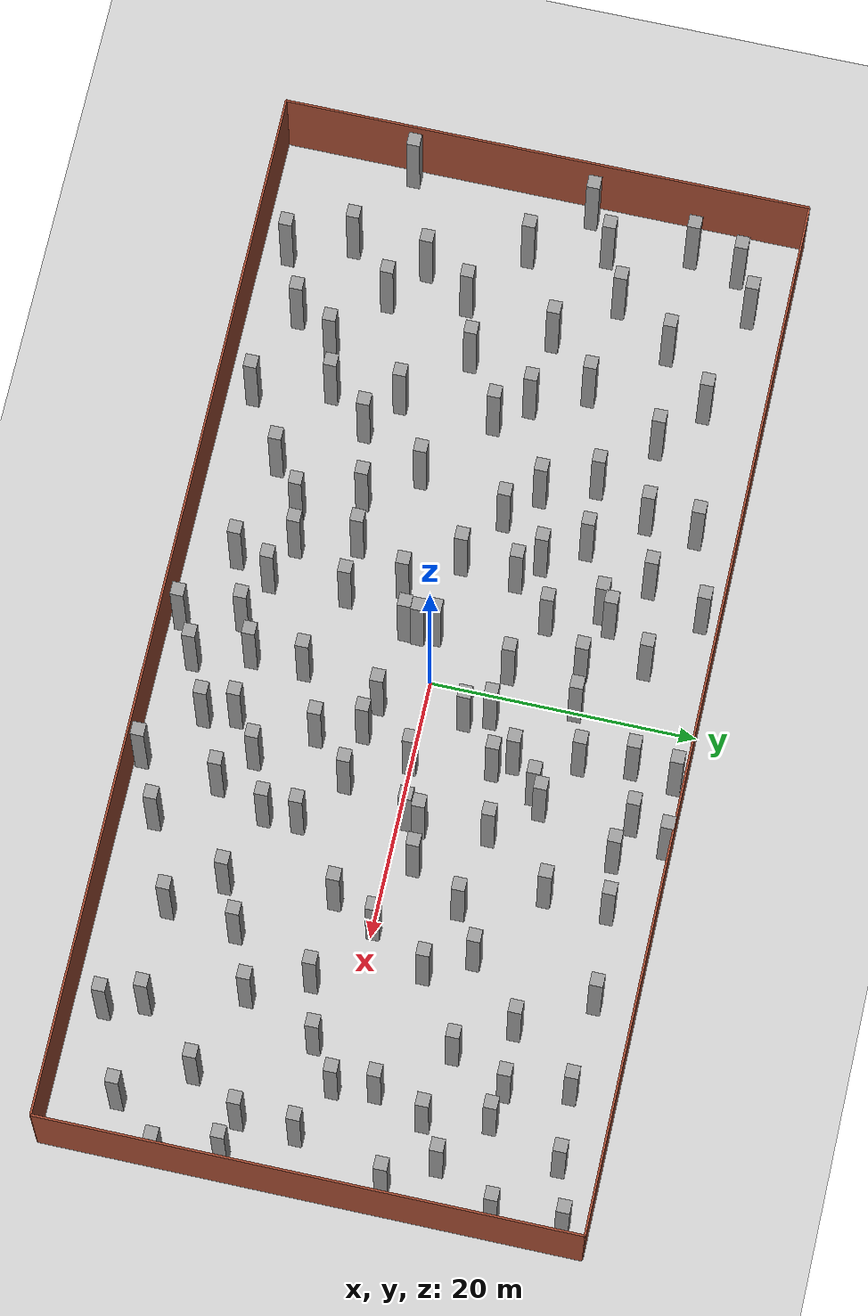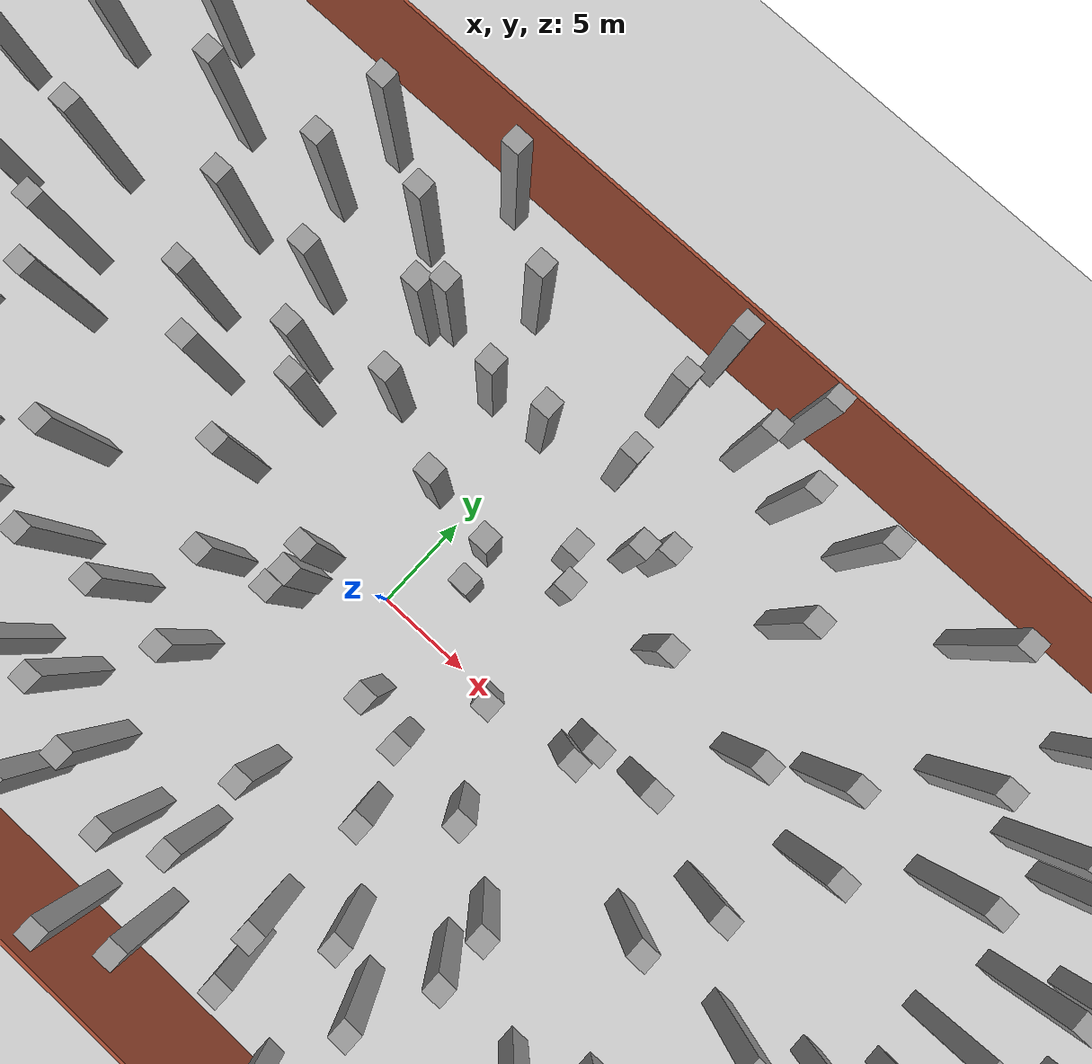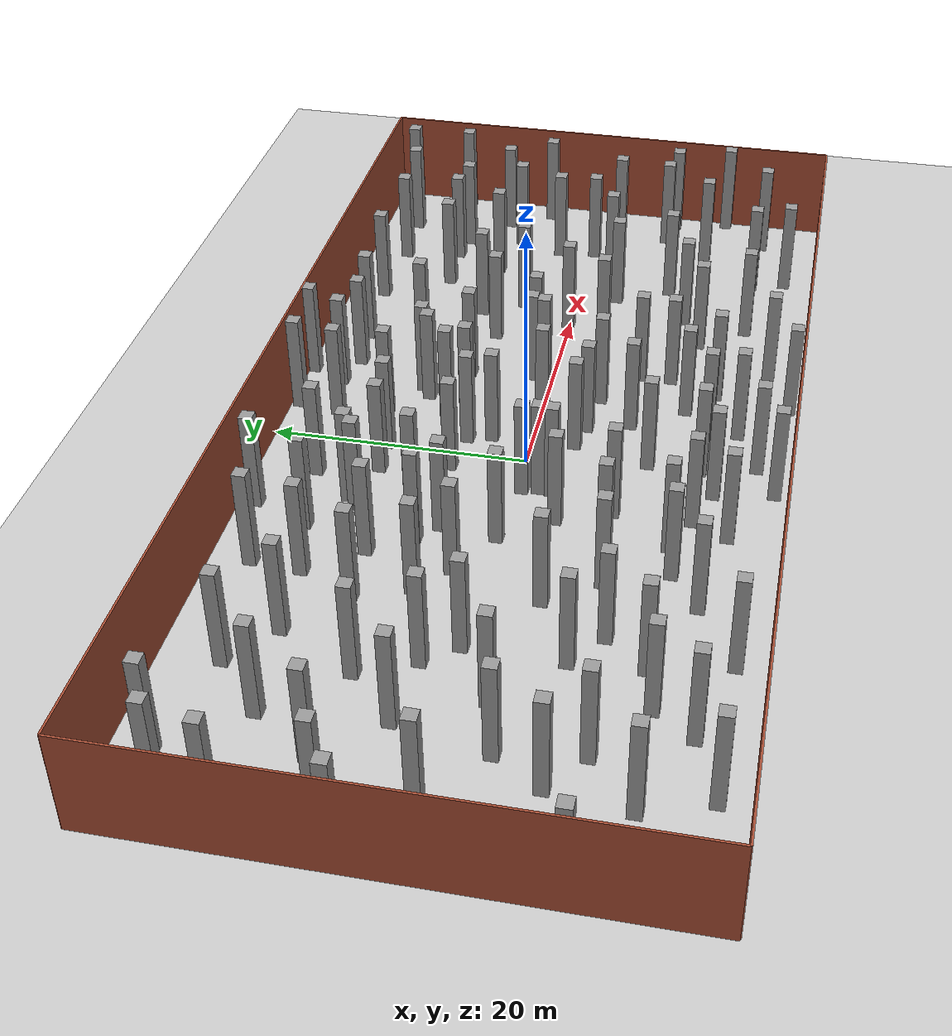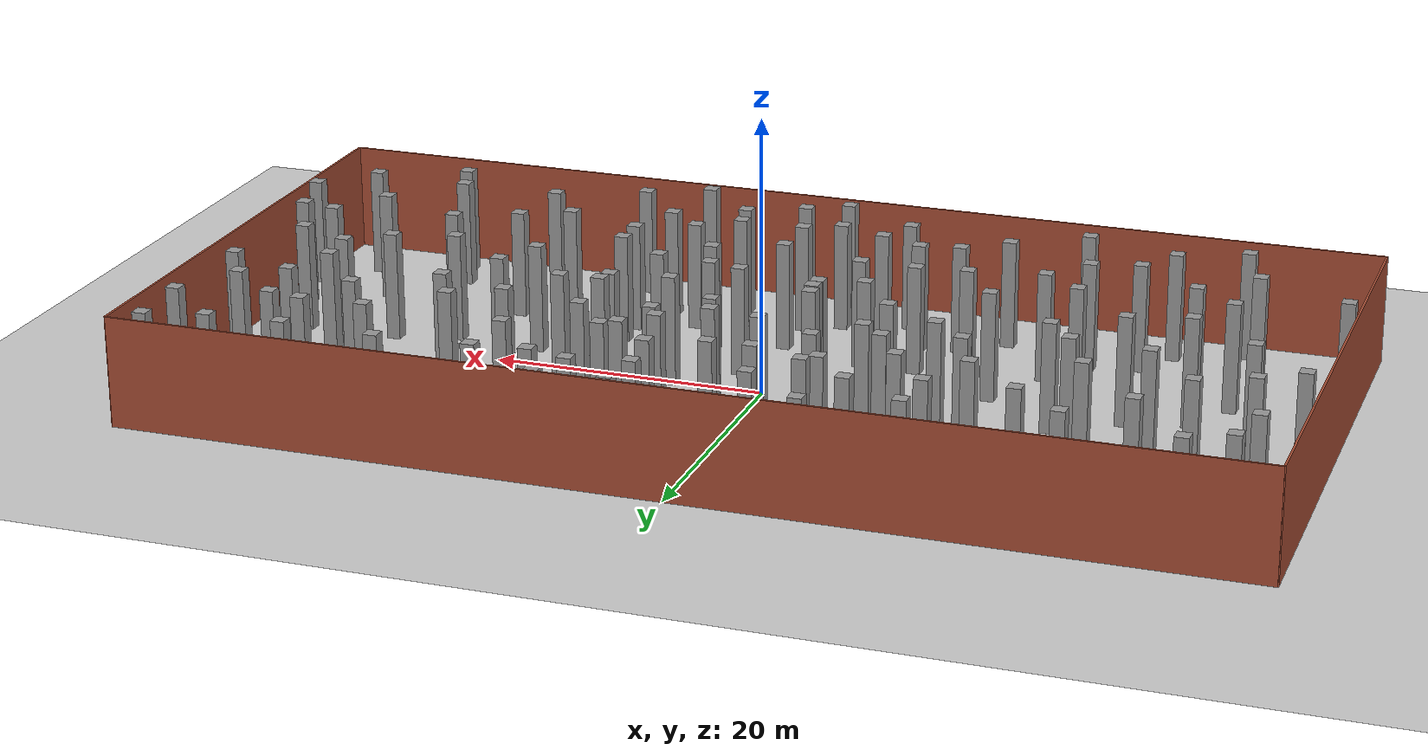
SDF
<sdf version="1.7">
 <world name="default">
  <light name="sun" type="directional">
   <pose>0 0 10 0 -0 0</pose>
   <diffuse>0.8 0.8 0.8 1</diffuse>
   <specular>0.2 0.2 0.2 1</specular>
   <attenuation>
    <range>1000</range>
    <constant>0.9</constant>
    <linear>0.01</linear>
    <quadratic>0.001</quadratic>
   </attenuation>
   <direction>-0.5 0.1 -0.9</direction>
   <spot><inner_angle>0</inner_angle><outer_angle>0</outer_angle><falloff>0</falloff></spot>
  </light>
  <model name="ground_plane">
   <static>1</static>
   <link name="link">
    <collision name="collision">
     <geometry><plane><normal>0 0 1</normal><size>100 100</size></plane></geometry>
     <surface>
      <contact><collide_bitmask>65535</collide_bitmask></contact>
      <friction><ode><mu>100</mu><mu2>50</mu2></ode></friction>
     </surface>
    </collision>
    <visual name="visual">
     <cast_shadows>0</cast_shadows>
     <geometry><plane><normal>0 0 1</normal><size>100 100</size></plane></geometry>
     <material>
      <script><uri>file://media/materials/scripts/gazebo.material</uri><name>Gazebo/Grey</name></script>
     </material>
    </visual>
   </link>
  </model>
  <gravity>0 0 -9.8</gravity>
  <magnetic_field>6e-06 2.3e-05 -4.2e-05</magnetic_field>
  <atmosphere type="adiabatic"/>
  <physics type="ode">
   <max_step_size>0.001</max_step_size>
   <real_time_factor>1</real_time_factor>
   <real_time_update_rate>1000</real_time_update_rate>
  </physics>
  <scene><ambient>0.4 0.4 0.4 1</ambient><background>0.7 0.7 0.7 1</background><shadows>1</shadows></scene>
  <spherical_coordinates>
   <surface_model>EARTH_WGS84</surface_model>
   <latitude_deg>0</latitude_deg>
   <longitude_deg>0</longitude_deg>
   <elevation>0</elevation>
   <heading_deg>0</heading_deg>
  </spherical_coordinates>
  <model name="sim_room_rect">
   <link name="Wall_14">
    <collision name="Wall_14_Collision">
     <geometry><box><size>40 0.15 8</size></box></geometry>
     <pose>0 0 4 0 -0 0</pose>
    </collision>
    <visual name="Wall_14_Visual">
     <pose>0 0 4 0 -0 0</pose>
     <geometry><box><size>40 0.15 8</size></box></geometry>
     <material>
      <script><uri>file://media/materials/scripts/gazebo.material</uri><name>Gazebo/Bricks</name></script>
      <ambient>1 1 1 1</ambient>
     </material>
     <meta><layer>0</layer></meta>
    </visual>
    <pose>40 -0 0 0 -0 -1.5708</pose>
   </link>
   <link name="Wall_15">
    <collision name="Wall_15_Collision">
     <geometry><box><size>80 0.15 8</size></box></geometry>
     <pose>0 0 4 0 -0 0</pose>
    </collision>
    <visual name="Wall_15_Visual">
     <pose>0 0 4 0 -0 0</pose>
     <geometry><box><size>80 0.15 8</size></box></geometry>
     <material>
      <script><uri>file://media/materials/scripts/gazebo.material</uri><name>Gazebo/Bricks</name></script>
      <ambient>1 1 1 1</ambient>
     </material>
     <meta><layer>0</layer></meta>
    </visual>
    <pose>0 -20 0 0 -0 3.14159</pose>
   </link>
   <link name="Wall_16">
    <collision name="Wall_16_Collision">
     <geometry><box><size>40 0.15 8</size></box></geometry>
     <pose>0 0 4 0 -0 0</pose>
    </collision>
    <visual name="Wall_16_Visual">
     <pose>0 0 4 0 -0 0</pose>
     <geometry><box><size>40 0.15 8</size></box></geometry>
     <material>
      <script><uri>file://media/materials/scripts/gazebo.material</uri><name>Gazebo/Bricks</name></script>
      <ambient>1 1 1 1</ambient>
     </material>
     <meta><layer>0</layer></meta>
    </visual>
    <pose>-40 -0 0 0 -0 1.5708</pose>
   </link>
   <link name="Wall_19">
    <collision name="Wall_19_Collision">
     <geometry><box><size>80 0.15 8</size></box></geometry>
     <pose>0 0 4 0 -0 0</pose>
    </collision>
    <visual name="Wall_19_Visual">
     <pose>0 0 4 0 -0 0</pose>
     <geometry><box><size>80 0.15 8</size></box></geometry>
     <material>
      <script><uri>file://media/materials/scripts/gazebo.material</uri><name>Gazebo/Bricks</name></script>
      <ambient>1 1 1 1</ambient>
     </material>
     <meta><layer>0</layer></meta>
    </visual>
    <pose>0 20 0 0 -0 0</pose>
   </link>
   <static>1</static>
  </model>
  <model name="unit_box_static52">
   <link name="link">
    <inertial>
     <mass>1</mass>
     <inertia>
      <ixx>0.166667</ixx>
      <ixy>0</ixy>
      <ixz>0</ixz>
      <iyy>0.166667</iyy>
      <iyz>0</iyz>
      <izz>0.166667</izz>
     </inertia>
    </inertial>
    <visual name="visual">
     <geometry><box><size>1 1 8</size></box></geometry>
     <material>
      <script><name>Gazebo/Grey</name><uri>file://media/materials/scripts/gazebo.material</uri></script>
      <shader type="pixel"/>
     </material>
    </visual>
    <collision name="collision">
     <geometry><box><size>1 1 8</size></box></geometry>
     <surface>
      <friction>
       <ode><mu>1</mu><mu2>1</mu2><fdir1>0 0 0</fdir1><slip1>0</slip1><slip2>0</slip2></ode>
       <torsional>
        <coefficient>1</coefficient>
        <patch_radius>0</patch_radius>
        <surface_radius>0</surface_radius>
        <use_patch_radius>1</use_patch_radius>
        <ode><slip>0</slip></ode>
       </torsional>
      </friction>
      <bounce><restitution_coefficient>0</restitution_coefficient><threshold>1e+06</threshold></bounce>
      <contact>
       <collide_without_contact>0</collide_without_contact>
       <collide_without_contact_bitmask>1</collide_without_contact_bitmask>
       <collide_bitmask>1</collide_bitmask>
       <ode>
        <soft_cfm>0</soft_cfm>
        <soft_erp>0.2</soft_erp>
        <kp>1e+13</kp>
        <kd>1</kd>
        <max_vel>0.01</max_vel>
        <min_depth>0</min_depth>
       </ode>
       <bullet>
        <split_impulse>1</split_impulse>
        <split_impulse_penetration_threshold>-0.01</split_impulse_penetration_threshold>
        <soft_cfm>0</soft_cfm>
        <soft_erp>0.2</soft_erp>
        <kp>1e+13</kp>
        <kd>1</kd>
       </bullet>
      </contact>
     </surface>
    </collision>
   </link>
   <static>1</static>
   <pose>19.6242 0.16304 4 0 -0 0</pose>
  </model>
  <model name="unit_box_static53">
   <link name="link">
    <inertial>
     <mass>1</mass>
     <inertia>
      <ixx>0.166667</ixx>
      <ixy>0</ixy>
      <ixz>0</ixz>
      <iyy>0.166667</iyy>
      <iyz>0</iyz>
      <izz>0.166667</izz>
     </inertia>
    </inertial>
    <visual name="visual">
     <geometry><box><size>1 1 8</size></box></geometry>
     <material>
      <script><name>Gazebo/Grey</name><uri>file://media/materials/scripts/gazebo.material</uri></script>
      <shader type="pixel"/>
     </material>
    </visual>
    <collision name="collision">
     <geometry><box><size>1 1 8</size></box></geometry>
     <surface>
      <friction>
       <ode><mu>1</mu><mu2>1</mu2><fdir1>0 0 0</fdir1><slip1>0</slip1><slip2>0</slip2></ode>
       <torsional>
        <coefficient>1</coefficient>
        <patch_radius>0</patch_radius>
        <surface_radius>0</surface_radius>
        <use_patch_radius>1</use_patch_radius>
        <ode><slip>0</slip></ode>
       </torsional>
      </friction>
      <bounce><restitution_coefficient>0</restitution_coefficient><threshold>1e+06</threshold></bounce>
      <contact>
       <collide_without_contact>0</collide_without_contact>
       <collide_without_contact_bitmask>1</collide_without_contact_bitmask>
       <collide_bitmask>1</collide_bitmask>
       <ode>
        <soft_cfm>0</soft_cfm>
        <soft_erp>0.2</soft_erp>
        <kp>1e+13</kp>
        <kd>1</kd>
        <max_vel>0.01</max_vel>
        <min_depth>0</min_depth>
       </ode>
       <bullet>
        <split_impulse>1</split_impulse>
        <split_impulse_penetration_threshold>-0.01</split_impulse_penetration_threshold>
        <soft_cfm>0</soft_cfm>
        <soft_erp>0.2</soft_erp>
        <kp>1e+13</kp>
        <kd>1</kd>
       </bullet>
      </contact>
     </surface>
    </collision>
   </link>
   <static>1</static>
   <pose>5.94114 5.9923 4 0 -0 0</pose>
  </model>
  <model name="unit_box_static56">
   <link name="link">
    <inertial>
     <mass>1</mass>
     <inertia>
      <ixx>0.166667</ixx>
      <ixy>0</ixy>
      <ixz>0</ixz>
      <iyy>0.166667</iyy>
      <iyz>0</iyz>
      <izz>0.166667</izz>
     </inertia>
    </inertial>
    <visual name="visual">
     <geometry><box><size>1 1 8</size></box></geometry>
     <material>
      <script><name>Gazebo/Grey</name><uri>file://media/materials/scripts/gazebo.material</uri></script>
      <shader type="pixel"/>
     </material>
    </visual>
    <collision name="collision">
     <geometry><box><size>1 1 8</size></box></geometry>
     <surface>
      <friction>
       <ode><mu>1</mu><mu2>1</mu2><fdir1>0 0 0</fdir1><slip1>0</slip1><slip2>0</slip2></ode>
       <torsional>
        <coefficient>1</coefficient>
        <patch_radius>0</patch_radius>
        <surface_radius>0</surface_radius>
        <use_patch_radius>1</use_patch_radius>
        <ode><slip>0</slip></ode>
       </torsional>
      </friction>
      <bounce><restitution_coefficient>0</restitution_coefficient><threshold>1e+06</threshold></bounce>
      <contact>
       <collide_without_contact>0</collide_without_contact>
       <collide_without_contact_bitmask>1</collide_without_contact_bitmask>
       <collide_bitmask>1</collide_bitmask>
       <ode>
        <soft_cfm>0</soft_cfm>
        <soft_erp>0.2</soft_erp>
        <kp>1e+13</kp>
        <kd>1</kd>
        <max_vel>0.01</max_vel>
        <min_depth>0</min_depth>
       </ode>
       <bullet>
        <split_impulse>1</split_impulse>
        <split_impulse_penetration_threshold>-0.01</split_impulse_penetration_threshold>
        <soft_cfm>0</soft_cfm>
        <soft_erp>0.2</soft_erp>
        <kp>1e+13</kp>
        <kd>1</kd>
       </bullet>
      </contact>
     </surface>
    </collision>
   </link>
   <static>1</static>
   <pose>-10.8013 -12.5136 4 0 -0 0</pose>
  </model>
  <model name="unit_box_static57">
   <link name="link">
    <inertial>
     <mass>1</mass>
     <inertia>
      <ixx>0.166667</ixx>
      <ixy>0</ixy>
      <ixz>0</ixz>
      <iyy>0.166667</iyy>
      <iyz>0</iyz>
      <izz>0.166667</izz>
     </inertia>
    </inertial>
    <visual name="visual">
     <geometry><box><size>1 1 8</size></box></geometry>
     <material>
      <script><name>Gazebo/Grey</name><uri>file://media/materials/scripts/gazebo.material</uri></script>
      <shader type="pixel"/>
     </material>
    </visual>
    <collision name="collision">
     <geometry><box><size>1 1 8</size></box></geometry>
     <surface>
      <friction>
       <ode><mu>1</mu><mu2>1</mu2><fdir1>0 0 0</fdir1><slip1>0</slip1><slip2>0</slip2></ode>
       <torsional>
        <coefficient>1</coefficient>
        <patch_radius>0</patch_radius>
        <surface_radius>0</surface_radius>
        <use_patch_radius>1</use_patch_radius>
        <ode><slip>0</slip></ode>
       </torsional>
      </friction>
      <bounce><restitution_coefficient>0</restitution_coefficient><threshold>1e+06</threshold></bounce>
      <contact>
       <collide_without_contact>0</collide_without_contact>
       <collide_without_contact_bitmask>1</collide_without_contact_bitmask>
       <collide_bitmask>1</collide_bitmask>
       <ode>
        <soft_cfm>0</soft_cfm>
        <soft_erp>0.2</soft_erp>
        <kp>1e+13</kp>
        <kd>1</kd>
        <max_vel>0.01</max_vel>
        <min_depth>0</min_depth>
       </ode>
       <bullet>
        <split_impulse>1</split_impulse>
        <split_impulse_penetration_threshold>-0.01</split_impulse_penetration_threshold>
        <soft_cfm>0</soft_cfm>
        <soft_erp>0.2</soft_erp>
        <kp>1e+13</kp>
        <kd>1</kd>
       </bullet>
      </contact>
     </surface>
    </collision>
   </link>
   <static>1</static>
   <pose>-39.0012 -9.92582 4 0 -0 0</pose>
  </model>
  <model name="unit_box_static58">
   <link name="link">
    <inertial>
     <mass>1</mass>
     <inertia>
      <ixx>0.166667</ixx>
      <ixy>0</ixy>
      <ixz>0</ixz>
      <iyy>0.166667</iyy>
      <iyz>0</iyz>
      <izz>0.166667</izz>
     </inertia>
    </inertial>
    <visual name="visual">
     <geometry><box><size>1 1 8</size></box></geometry>
     <material>
      <script><name>Gazebo/Grey</name><uri>file://media/materials/scripts/gazebo.material</uri></script>
      <shader type="pixel"/>
     </material>
    </visual>
    <collision name="collision">
     <geometry><box><size>1 1 8</size></box></geometry>
     <surface>
      <friction>
       <ode><mu>1</mu><mu2>1</mu2><fdir1>0 0 0</fdir1><slip1>0</slip1><slip2>0</slip2></ode>
       <torsional>
        <coefficient>1</coefficient>
        <patch_radius>0</patch_radius>
        <surface_radius>0</surface_radius>
        <use_patch_radius>1</use_patch_radius>
        <ode><slip>0</slip></ode>
       </torsional>
      </friction>
      <bounce><restitution_coefficient>0</restitution_coefficient><threshold>1e+06</threshold></bounce>
      <contact>
       <collide_without_contact>0</collide_without_contact>
       <collide_without_contact_bitmask>1</collide_without_contact_bitmask>
       <collide_bitmask>1</collide_bitmask>
       <ode>
        <soft_cfm>0</soft_cfm>
        <soft_erp>0.2</soft_erp>
        <kp>1e+13</kp>
        <kd>1</kd>
        <max_vel>0.01</max_vel>
        <min_depth>0</min_depth>
       </ode>
       <bullet>
        <split_impulse>1</split_impulse>
        <split_impulse_penetration_threshold>-0.01</split_impulse_penetration_threshold>
        <soft_cfm>0</soft_cfm>
        <soft_erp>0.2</soft_erp>
        <kp>1e+13</kp>
        <kd>1</kd>
       </bullet>
      </contact>
     </surface>
    </collision>
   </link>
   <static>1</static>
   <pose>-34.4356 -0.088908 4 0 -0 0</pose>
  </model>
  <model name="unit_box_static59">
   <link name="link">
    <inertial>
     <mass>1</mass>
     <inertia>
      <ixx>0.166667</ixx>
      <ixy>0</ixy>
      <ixz>0</ixz>
      <iyy>0.166667</iyy>
      <iyz>0</iyz>
      <izz>0.166667</izz>
     </inertia>
    </inertial>
    <visual name="visual">
     <geometry><box><size>1 1 8</size></box></geometry>
     <material>
      <script><name>Gazebo/Grey</name><uri>file://media/materials/scripts/gazebo.material</uri></script>
      <shader type="pixel"/>
     </material>
    </visual>
    <collision name="collision">
     <geometry><box><size>1 1 8</size></box></geometry>
     <surface>
      <friction>
       <ode><mu>1</mu><mu2>1</mu2><fdir1>0 0 0</fdir1><slip1>0</slip1><slip2>0</slip2></ode>
       <torsional>
        <coefficient>1</coefficient>
        <patch_radius>0</patch_radius>
        <surface_radius>0</surface_radius>
        <use_patch_radius>1</use_patch_radius>
        <ode><slip>0</slip></ode>
       </torsional>
      </friction>
      <bounce><restitution_coefficient>0</restitution_coefficient><threshold>1e+06</threshold></bounce>
      <contact>
       <collide_without_contact>0</collide_without_contact>
       <collide_without_contact_bitmask>1</collide_without_contact_bitmask>
       <collide_bitmask>1</collide_bitmask>
       <ode>
        <soft_cfm>0</soft_cfm>
        <soft_erp>0.2</soft_erp>
        <kp>1e+13</kp>
        <kd>1</kd>
        <max_vel>0.01</max_vel>
        <min_depth>0</min_depth>
       </ode>
       <bullet>
        <split_impulse>1</split_impulse>
        <split_impulse_penetration_threshold>-0.01</split_impulse_penetration_threshold>
        <soft_cfm>0</soft_cfm>
        <soft_erp>0.2</soft_erp>
        <kp>1e+13</kp>
        <kd>1</kd>
       </bullet>
      </contact>
     </surface>
    </collision>
   </link>
   <static>1</static>
   <pose>11.0233 0.653893 4 0 -0 0</pose>
  </model>
  <model name="unit_box_static61">
   <link name="link">
    <inertial>
     <mass>1</mass>
     <inertia>
      <ixx>0.166667</ixx>
      <ixy>0</ixy>
      <ixz>0</ixz>
      <iyy>0.166667</iyy>
      <iyz>0</iyz>
      <izz>0.166667</izz>
     </inertia>
    </inertial>
    <visual name="visual">
     <geometry><box><size>1 1 8</size></box></geometry>
     <material>
      <script><name>Gazebo/Grey</name><uri>file://media/materials/scripts/gazebo.material</uri></script>
      <shader type="pixel"/>
     </material>
    </visual>
    <collision name="collision">
     <geometry><box><size>1 1 8</size></box></geometry>
     <surface>
      <friction>
       <ode><mu>1</mu><mu2>1</mu2><fdir1>0 0 0</fdir1><slip1>0</slip1><slip2>0</slip2></ode>
       <torsional>
        <coefficient>1</coefficient>
        <patch_radius>0</patch_radius>
        <surface_radius>0</surface_radius>
        <use_patch_radius>1</use_patch_radius>
        <ode><slip>0</slip></ode>
       </torsional>
      </friction>
      <bounce><restitution_coefficient>0</restitution_coefficient><threshold>1e+06</threshold></bounce>
      <contact>
       <collide_without_contact>0</collide_without_contact>
       <collide_without_contact_bitmask>1</collide_without_contact_bitmask>
       <collide_bitmask>1</collide_bitmask>
       <ode>
        <soft_cfm>0</soft_cfm>
        <soft_erp>0.2</soft_erp>
        <kp>1e+13</kp>
        <kd>1</kd>
        <max_vel>0.01</max_vel>
        <min_depth>0</min_depth>
       </ode>
       <bullet>
        <split_impulse>1</split_impulse>
        <split_impulse_penetration_threshold>-0.01</split_impulse_penetration_threshold>
        <soft_cfm>0</soft_cfm>
        <soft_erp>0.2</soft_erp>
        <kp>1e+13</kp>
        <kd>1</kd>
       </bullet>
      </contact>
     </surface>
    </collision>
   </link>
   <static>1</static>
   <pose>32.8914 6.80338 4 0 -0 0</pose>
  </model>
  <model name="unit_box_static63">
   <link name="link">
    <inertial>
     <mass>1</mass>
     <inertia>
      <ixx>0.166667</ixx>
      <ixy>0</ixy>
      <ixz>0</ixz>
      <iyy>0.166667</iyy>
      <iyz>0</iyz>
      <izz>0.166667</izz>
     </inertia>
    </inertial>
    <visual name="visual">
     <geometry><box><size>1 1 8</size></box></geometry>
     <material>
      <script><name>Gazebo/Grey</name><uri>file://media/materials/scripts/gazebo.material</uri></script>
      <shader type="pixel"/>
     </material>
    </visual>
    <collision name="collision">
     <geometry><box><size>1 1 8</size></box></geometry>
     <surface>
      <friction>
       <ode><mu>1</mu><mu2>1</mu2><fdir1>0 0 0</fdir1><slip1>0</slip1><slip2>0</slip2></ode>
       <torsional>
        <coefficient>1</coefficient>
        <patch_radius>0</patch_radius>
        <surface_radius>0</surface_radius>
        <use_patch_radius>1</use_patch_radius>
        <ode><slip>0</slip></ode>
       </torsional>
      </friction>
      <bounce><restitution_coefficient>0</restitution_coefficient><threshold>1e+06</threshold></bounce>
      <contact>
       <collide_without_contact>0</collide_without_contact>
       <collide_without_contact_bitmask>1</collide_without_contact_bitmask>
       <collide_bitmask>1</collide_bitmask>
       <ode>
        <soft_cfm>0</soft_cfm>
        <soft_erp>0.2</soft_erp>
        <kp>1e+13</kp>
        <kd>1</kd>
        <max_vel>0.01</max_vel>
        <min_depth>0</min_depth>
       </ode>
       <bullet>
        <split_impulse>1</split_impulse>
        <split_impulse_penetration_threshold>-0.01</split_impulse_penetration_threshold>
        <soft_cfm>0</soft_cfm>
        <soft_erp>0.2</soft_erp>
        <kp>1e+13</kp>
        <kd>1</kd>
       </bullet>
      </contact>
     </surface>
    </collision>
   </link>
   <static>1</static>
   <pose>-29.5161 -3.72993 4 0 -0 0</pose>
  </model>
  <model name="unit_box_static64">
   <link name="link">
    <inertial>
     <mass>1</mass>
     <inertia>
      <ixx>0.166667</ixx>
      <ixy>0</ixy>
      <ixz>0</ixz>
      <iyy>0.166667</iyy>
      <iyz>0</iyz>
      <izz>0.166667</izz>
     </inertia>
    </inertial>
    <visual name="visual">
     <geometry><box><size>1 1 8</size></box></geometry>
     <material>
      <script><name>Gazebo/Grey</name><uri>file://media/materials/scripts/gazebo.material</uri></script>
      <shader type="pixel"/>
     </material>
    </visual>
    <collision name="collision">
     <geometry><box><size>1 1 8</size></box></geometry>
     <surface>
      <friction>
       <ode><mu>1</mu><mu2>1</mu2><fdir1>0 0 0</fdir1><slip1>0</slip1><slip2>0</slip2></ode>
       <torsional>
        <coefficient>1</coefficient>
        <patch_radius>0</patch_radius>
        <surface_radius>0</surface_radius>
        <use_patch_radius>1</use_patch_radius>
        <ode><slip>0</slip></ode>
       </torsional>
      </friction>
      <bounce><restitution_coefficient>0</restitution_coefficient><threshold>1e+06</threshold></bounce>
      <contact>
       <collide_without_contact>0</collide_without_contact>
       <collide_without_contact_bitmask>1</collide_without_contact_bitmask>
       <collide_bitmask>1</collide_bitmask>
       <ode>
        <soft_cfm>0</soft_cfm>
        <soft_erp>0.2</soft_erp>
        <kp>1e+13</kp>
        <kd>1</kd>
        <max_vel>0.01</max_vel>
        <min_depth>0</min_depth>
       </ode>
       <bullet>
        <split_impulse>1</split_impulse>
        <split_impulse_penetration_threshold>-0.01</split_impulse_penetration_threshold>
        <soft_cfm>0</soft_cfm>
        <soft_erp>0.2</soft_erp>
        <kp>1e+13</kp>
        <kd>1</kd>
       </bullet>
      </contact>
     </surface>
    </collision>
   </link>
   <static>1</static>
   <pose>24.4703 -3.32359 4 0 -0 0</pose>
  </model>
  <model name="unit_box_static65">
   <link name="link">
    <inertial>
     <mass>1</mass>
     <inertia>
      <ixx>0.166667</ixx>
      <ixy>0</ixy>
      <ixz>0</ixz>
      <iyy>0.166667</iyy>
      <iyz>0</iyz>
      <izz>0.166667</izz>
     </inertia>
    </inertial>
    <visual name="visual">
     <geometry><box><size>1 1 8</size></box></geometry>
     <material>
      <script><name>Gazebo/Grey</name><uri>file://media/materials/scripts/gazebo.material</uri></script>
      <shader type="pixel"/>
     </material>
    </visual>
    <collision name="collision">
     <geometry><box><size>1 1 8</size></box></geometry>
     <surface>
      <friction>
       <ode><mu>1</mu><mu2>1</mu2><fdir1>0 0 0</fdir1><slip1>0</slip1><slip2>0</slip2></ode>
       <torsional>
        <coefficient>1</coefficient>
        <patch_radius>0</patch_radius>
        <surface_radius>0</surface_radius>
        <use_patch_radius>1</use_patch_radius>
        <ode><slip>0</slip></ode>
       </torsional>
      </friction>
      <bounce><restitution_coefficient>0</restitution_coefficient><threshold>1e+06</threshold></bounce>
      <contact>
       <collide_without_contact>0</collide_without_contact>
       <collide_without_contact_bitmask>1</collide_without_contact_bitmask>
       <collide_bitmask>1</collide_bitmask>
       <ode>
        <soft_cfm>0</soft_cfm>
        <soft_erp>0.2</soft_erp>
        <kp>1e+13</kp>
        <kd>1</kd>
        <max_vel>0.01</max_vel>
        <min_depth>0</min_depth>
       </ode>
       <bullet>
        <split_impulse>1</split_impulse>
        <split_impulse_penetration_threshold>-0.01</split_impulse_penetration_threshold>
        <soft_cfm>0</soft_cfm>
        <soft_erp>0.2</soft_erp>
        <kp>1e+13</kp>
        <kd>1</kd>
       </bullet>
      </contact>
     </surface>
    </collision>
   </link>
   <static>1</static>
   <pose>-20.7592 -6.89951 4 0 -0 0</pose>
  </model>
  <model name="unit_box_static66">
   <link name="link">
    <inertial>
     <mass>1</mass>
     <inertia>
      <ixx>0.166667</ixx>
      <ixy>0</ixy>
      <ixz>0</ixz>
      <iyy>0.166667</iyy>
      <iyz>0</iyz>
      <izz>0.166667</izz>
     </inertia>
    </inertial>
    <visual name="visual">
     <geometry><box><size>1 1 8</size></box></geometry>
     <material>
      <script><name>Gazebo/Grey</name><uri>file://media/materials/scripts/gazebo.material</uri></script>
      <shader type="pixel"/>
     </material>
    </visual>
    <collision name="collision">
     <geometry><box><size>1 1 8</size></box></geometry>
     <surface>
      <friction>
       <ode><mu>1</mu><mu2>1</mu2><fdir1>0 0 0</fdir1><slip1>0</slip1><slip2>0</slip2></ode>
       <torsional>
        <coefficient>1</coefficient>
        <patch_radius>0</patch_radius>
        <surface_radius>0</surface_radius>
        <use_patch_radius>1</use_patch_radius>
        <ode><slip>0</slip></ode>
       </torsional>
      </friction>
      <bounce><restitution_coefficient>0</restitution_coefficient><threshold>1e+06</threshold></bounce>
      <contact>
       <collide_without_contact>0</collide_without_contact>
       <collide_without_contact_bitmask>1</collide_without_contact_bitmask>
       <collide_bitmask>1</collide_bitmask>
       <ode>
        <soft_cfm>0</soft_cfm>
        <soft_erp>0.2</soft_erp>
        <kp>1e+13</kp>
        <kd>1</kd>
        <max_vel>0.01</max_vel>
        <min_depth>0</min_depth>
       </ode>
       <bullet>
        <split_impulse>1</split_impulse>
        <split_impulse_penetration_threshold>-0.01</split_impulse_penetration_threshold>
        <soft_cfm>0</soft_cfm>
        <soft_erp>0.2</soft_erp>
        <kp>1e+13</kp>
        <kd>1</kd>
       </bullet>
      </contact>
     </surface>
    </collision>
   </link>
   <static>1</static>
   <pose>-15.7173 4.8814 4 0 -0 0</pose>
  </model>
  <model name="unit_box_static67">
   <link name="link">
    <inertial>
     <mass>1</mass>
     <inertia>
      <ixx>0.166667</ixx>
      <ixy>0</ixy>
      <ixz>0</ixz>
      <iyy>0.166667</iyy>
      <iyz>0</iyz>
      <izz>0.166667</izz>
     </inertia>
    </inertial>
    <visual name="visual">
     <geometry><box><size>1 1 8</size></box></geometry>
     <material>
      <script><name>Gazebo/Grey</name><uri>file://media/materials/scripts/gazebo.material</uri></script>
      <shader type="pixel"/>
     </material>
    </visual>
    <collision name="collision">
     <geometry><box><size>1 1 8</size></box></geometry>
     <surface>
      <friction>
       <ode><mu>1</mu><mu2>1</mu2><fdir1>0 0 0</fdir1><slip1>0</slip1><slip2>0</slip2></ode>
       <torsional>
        <coefficient>1</coefficient>
        <patch_radius>0</patch_radius>
        <surface_radius>0</surface_radius>
        <use_patch_radius>1</use_patch_radius>
        <ode><slip>0</slip></ode>
       </torsional>
      </friction>
      <bounce><restitution_coefficient>0</restitution_coefficient><threshold>1e+06</threshold></bounce>
      <contact>
       <collide_without_contact>0</collide_without_contact>
       <collide_without_contact_bitmask>1</collide_without_contact_bitmask>
       <collide_bitmask>1</collide_bitmask>
       <ode>
        <soft_cfm>0</soft_cfm>
        <soft_erp>0.2</soft_erp>
        <kp>1e+13</kp>
        <kd>1</kd>
        <max_vel>0.01</max_vel>
        <min_depth>0</min_depth>
       </ode>
       <bullet>
        <split_impulse>1</split_impulse>
        <split_impulse_penetration_threshold>-0.01</split_impulse_penetration_threshold>
        <soft_cfm>0</soft_cfm>
        <soft_erp>0.2</soft_erp>
        <kp>1e+13</kp>
        <kd>1</kd>
       </bullet>
      </contact>
     </surface>
    </collision>
   </link>
   <static>1</static>
   <pose>-28.5535 -9.61759 4 0 -0 0</pose>
  </model>
  <model name="unit_box_static68">
   <link name="link">
    <inertial>
     <mass>1</mass>
     <inertia>
      <ixx>0.166667</ixx>
      <ixy>0</ixy>
      <ixz>0</ixz>
      <iyy>0.166667</iyy>
      <iyz>0</iyz>
      <izz>0.166667</izz>
     </inertia>
    </inertial>
    <visual name="visual">
     <geometry><box><size>1 1 8</size></box></geometry>
     <material>
      <script><name>Gazebo/Grey</name><uri>file://media/materials/scripts/gazebo.material</uri></script>
      <shader type="pixel"/>
     </material>
    </visual>
    <collision name="collision">
     <geometry><box><size>1 1 8</size></box></geometry>
     <surface>
      <friction>
       <ode><mu>1</mu><mu2>1</mu2><fdir1>0 0 0</fdir1><slip1>0</slip1><slip2>0</slip2></ode>
       <torsional>
        <coefficient>1</coefficient>
        <patch_radius>0</patch_radius>
        <surface_radius>0</surface_radius>
        <use_patch_radius>1</use_patch_radius>
        <ode><slip>0</slip></ode>
       </torsional>
      </friction>
      <bounce><restitution_coefficient>0</restitution_coefficient><threshold>1e+06</threshold></bounce>
      <contact>
       <collide_without_contact>0</collide_without_contact>
       <collide_without_contact_bitmask>1</collide_without_contact_bitmask>
       <collide_bitmask>1</collide_bitmask>
       <ode>
        <soft_cfm>0</soft_cfm>
        <soft_erp>0.2</soft_erp>
        <kp>1e+13</kp>
        <kd>1</kd>
        <max_vel>0.01</max_vel>
        <min_depth>0</min_depth>
       </ode>
       <bullet>
        <split_impulse>1</split_impulse>
        <split_impulse_penetration_threshold>-0.01</split_impulse_penetration_threshold>
        <soft_cfm>0</soft_cfm>
        <soft_erp>0.2</soft_erp>
        <kp>1e+13</kp>
        <kd>1</kd>
       </bullet>
      </contact>
     </surface>
    </collision>
   </link>
   <static>1</static>
   <pose>-8.76914 4.5745 4 0 -0 0</pose>
  </model>
  <model name="unit_box_static69">
   <link name="link">
    <inertial>
     <mass>1</mass>
     <inertia>
      <ixx>0.166667</ixx>
      <ixy>0</ixy>
      <ixz>0</ixz>
      <iyy>0.166667</iyy>
      <iyz>0</iyz>
      <izz>0.166667</izz>
     </inertia>
    </inertial>
    <visual name="visual">
     <geometry><box><size>1 1 8</size></box></geometry>
     <material>
      <script><name>Gazebo/Grey</name><uri>file://media/materials/scripts/gazebo.material</uri></script>
      <shader type="pixel"/>
     </material>
    </visual>
    <collision name="collision">
     <geometry><box><size>1 1 8</size></box></geometry>
     <surface>
      <friction>
       <ode><mu>1</mu><mu2>1</mu2><fdir1>0 0 0</fdir1><slip1>0</slip1><slip2>0</slip2></ode>
       <torsional>
        <coefficient>1</coefficient>
        <patch_radius>0</patch_radius>
        <surface_radius>0</surface_radius>
        <use_patch_radius>1</use_patch_radius>
        <ode><slip>0</slip></ode>
       </torsional>
      </friction>
      <bounce><restitution_coefficient>0</restitution_coefficient><threshold>1e+06</threshold></bounce>
      <contact>
       <collide_without_contact>0</collide_without_contact>
       <collide_without_contact_bitmask>1</collide_without_contact_bitmask>
       <collide_bitmask>1</collide_bitmask>
       <ode>
        <soft_cfm>0</soft_cfm>
        <soft_erp>0.2</soft_erp>
        <kp>1e+13</kp>
        <kd>1</kd>
        <max_vel>0.01</max_vel>
        <min_depth>0</min_depth>
       </ode>
       <bullet>
        <split_impulse>1</split_impulse>
        <split_impulse_penetration_threshold>-0.01</split_impulse_penetration_threshold>
        <soft_cfm>0</soft_cfm>
        <soft_erp>0.2</soft_erp>
        <kp>1e+13</kp>
        <kd>1</kd>
       </bullet>
      </contact>
     </surface>
    </collision>
   </link>
   <static>1</static>
   <pose>-10.4438 6.09552 4 0 -0 0</pose>
  </model>
  <model name="unit_box_static70">
   <link name="link">
    <inertial>
     <mass>1</mass>
     <inertia>
      <ixx>0.166667</ixx>
      <ixy>0</ixy>
      <ixz>0</ixz>
      <iyy>0.166667</iyy>
      <iyz>0</iyz>
      <izz>0.166667</izz>
     </inertia>
    </inertial>
    <visual name="visual">
     <geometry><box><size>1 1 8</size></box></geometry>
     <material>
      <script><name>Gazebo/Grey</name><uri>file://media/materials/scripts/gazebo.material</uri></script>
      <shader type="pixel"/>
     </material>
    </visual>
    <collision name="collision">
     <geometry><box><size>1 1 8</size></box></geometry>
     <surface>
      <friction>
       <ode><mu>1</mu><mu2>1</mu2><fdir1>0 0 0</fdir1><slip1>0</slip1><slip2>0</slip2></ode>
       <torsional>
        <coefficient>1</coefficient>
        <patch_radius>0</patch_radius>
        <surface_radius>0</surface_radius>
        <use_patch_radius>1</use_patch_radius>
        <ode><slip>0</slip></ode>
       </torsional>
      </friction>
      <bounce><restitution_coefficient>0</restitution_coefficient><threshold>1e+06</threshold></bounce>
      <contact>
       <collide_without_contact>0</collide_without_contact>
       <collide_without_contact_bitmask>1</collide_without_contact_bitmask>
       <collide_bitmask>1</collide_bitmask>
       <ode>
        <soft_cfm>0</soft_cfm>
        <soft_erp>0.2</soft_erp>
        <kp>1e+13</kp>
        <kd>1</kd>
        <max_vel>0.01</max_vel>
        <min_depth>0</min_depth>
       </ode>
       <bullet>
        <split_impulse>1</split_impulse>
        <split_impulse_penetration_threshold>-0.01</split_impulse_penetration_threshold>
        <soft_cfm>0</soft_cfm>
        <soft_erp>0.2</soft_erp>
        <kp>1e+13</kp>
        <kd>1</kd>
       </bullet>
      </contact>
     </surface>
    </collision>
   </link>
   <static>1</static>
   <pose>-6.10529 -15.982 4 0 -0 0</pose>
  </model>
  <model name="unit_box_static71">
   <link name="link">
    <inertial>
     <mass>1</mass>
     <inertia>
      <ixx>0.166667</ixx>
      <ixy>0</ixy>
      <ixz>0</ixz>
      <iyy>0.166667</iyy>
      <iyz>0</iyz>
      <izz>0.166667</izz>
     </inertia>
    </inertial>
    <visual name="visual">
     <geometry><box><size>1 1 8</size></box></geometry>
     <material>
      <script><name>Gazebo/Grey</name><uri>file://media/materials/scripts/gazebo.material</uri></script>
      <shader type="pixel"/>
     </material>
    </visual>
    <collision name="collision">
     <geometry><box><size>1 1 8</size></box></geometry>
     <surface>
      <friction>
       <ode><mu>1</mu><mu2>1</mu2><fdir1>0 0 0</fdir1><slip1>0</slip1><slip2>0</slip2></ode>
       <torsional>
        <coefficient>1</coefficient>
        <patch_radius>0</patch_radius>
        <surface_radius>0</surface_radius>
        <use_patch_radius>1</use_patch_radius>
        <ode><slip>0</slip></ode>
       </torsional>
      </friction>
      <bounce><restitution_coefficient>0</restitution_coefficient><threshold>1e+06</threshold></bounce>
      <contact>
       <collide_without_contact>0</collide_without_contact>
       <collide_without_contact_bitmask>1</collide_without_contact_bitmask>
       <collide_bitmask>1</collide_bitmask>
       <ode>
        <soft_cfm>0</soft_cfm>
        <soft_erp>0.2</soft_erp>
        <kp>1e+13</kp>
        <kd>1</kd>
        <max_vel>0.01</max_vel>
        <min_depth>0</min_depth>
       </ode>
       <bullet>
        <split_impulse>1</split_impulse>
        <split_impulse_penetration_threshold>-0.01</split_impulse_penetration_threshold>
        <soft_cfm>0</soft_cfm>
        <soft_erp>0.2</soft_erp>
        <kp>1e+13</kp>
        <kd>1</kd>
       </bullet>
      </contact>
     </surface>
    </collision>
   </link>
   <static>1</static>
   <pose>-38.5507 3.94057 4 0 -0 0</pose>
  </model>
  <model name="unit_box_static72">
   <link name="link">
    <inertial>
     <mass>1</mass>
     <inertia>
      <ixx>0.166667</ixx>
      <ixy>0</ixy>
      <ixz>0</ixz>
      <iyy>0.166667</iyy>
      <iyz>0</iyz>
      <izz>0.166667</izz>
     </inertia>
    </inertial>
    <visual name="visual">
     <geometry><box><size>1 1 8</size></box></geometry>
     <material>
      <script><name>Gazebo/Grey</name><uri>file://media/materials/scripts/gazebo.material</uri></script>
      <shader type="pixel"/>
     </material>
    </visual>
    <collision name="collision">
     <geometry><box><size>1 1 8</size></box></geometry>
     <surface>
      <friction>
       <ode><mu>1</mu><mu2>1</mu2><fdir1>0 0 0</fdir1><slip1>0</slip1><slip2>0</slip2></ode>
       <torsional>
        <coefficient>1</coefficient>
        <patch_radius>0</patch_radius>
        <surface_radius>0</surface_radius>
        <use_patch_radius>1</use_patch_radius>
        <ode><slip>0</slip></ode>
       </torsional>
      </friction>
      <bounce><restitution_coefficient>0</restitution_coefficient><threshold>1e+06</threshold></bounce>
      <contact>
       <collide_without_contact>0</collide_without_contact>
       <collide_without_contact_bitmask>1</collide_without_contact_bitmask>
       <collide_bitmask>1</collide_bitmask>
       <ode>
        <soft_cfm>0</soft_cfm>
        <soft_erp>0.2</soft_erp>
        <kp>1e+13</kp>
        <kd>1</kd>
        <max_vel>0.01</max_vel>
        <min_depth>0</min_depth>
       </ode>
       <bullet>
        <split_impulse>1</split_impulse>
        <split_impulse_penetration_threshold>-0.01</split_impulse_penetration_threshold>
        <soft_cfm>0</soft_cfm>
        <soft_erp>0.2</soft_erp>
        <kp>1e+13</kp>
        <kd>1</kd>
       </bullet>
      </contact>
     </surface>
    </collision>
   </link>
   <static>1</static>
   <pose>-24.94 15.4237 4 0 -0 0</pose>
  </model>
  <model name="unit_box_static73">
   <link name="link">
    <inertial>
     <mass>1</mass>
     <inertia>
      <ixx>0.166667</ixx>
      <ixy>0</ixy>
      <ixz>0</ixz>
      <iyy>0.166667</iyy>
      <iyz>0</iyz>
      <izz>0.166667</izz>
     </inertia>
    </inertial>
    <visual name="visual">
     <geometry><box><size>1 1 8</size></box></geometry>
     <material>
      <script><name>Gazebo/Grey</name><uri>file://media/materials/scripts/gazebo.material</uri></script>
      <shader type="pixel"/>
     </material>
    </visual>
    <collision name="collision">
     <geometry><box><size>1 1 8</size></box></geometry>
     <surface>
      <friction>
       <ode><mu>1</mu><mu2>1</mu2><fdir1>0 0 0</fdir1><slip1>0</slip1><slip2>0</slip2></ode>
       <torsional>
        <coefficient>1</coefficient>
        <patch_radius>0</patch_radius>
        <surface_radius>0</surface_radius>
        <use_patch_radius>1</use_patch_radius>
        <ode><slip>0</slip></ode>
       </torsional>
      </friction>
      <bounce><restitution_coefficient>0</restitution_coefficient><threshold>1e+06</threshold></bounce>
      <contact>
       <collide_without_contact>0</collide_without_contact>
       <collide_without_contact_bitmask>1</collide_without_contact_bitmask>
       <collide_bitmask>1</collide_bitmask>
       <ode>
        <soft_cfm>0</soft_cfm>
        <soft_erp>0.2</soft_erp>
        <kp>1e+13</kp>
        <kd>1</kd>
        <max_vel>0.01</max_vel>
        <min_depth>0</min_depth>
       </ode>
       <bullet>
        <split_impulse>1</split_impulse>
        <split_impulse_penetration_threshold>-0.01</split_impulse_penetration_threshold>
        <soft_cfm>0</soft_cfm>
        <soft_erp>0.2</soft_erp>
        <kp>1e+13</kp>
        <kd>1</kd>
       </bullet>
      </contact>
     </surface>
    </collision>
   </link>
   <static>1</static>
   <pose>14.3034 1.95691 4 0 -0 0</pose>
  </model>
  <model name="unit_box_static74">
   <link name="link">
    <inertial>
     <mass>1</mass>
     <inertia>
      <ixx>0.166667</ixx>
      <ixy>0</ixy>
      <ixz>0</ixz>
      <iyy>0.166667</iyy>
      <iyz>0</iyz>
      <izz>0.166667</izz>
     </inertia>
    </inertial>
    <visual name="visual">
     <geometry><box><size>1 1 8</size></box></geometry>
     <material>
      <script><name>Gazebo/Grey</name><uri>file://media/materials/scripts/gazebo.material</uri></script>
      <shader type="pixel"/>
     </material>
    </visual>
    <collision name="collision">
     <geometry><box><size>1 1 8</size></box></geometry>
     <surface>
      <friction>
       <ode><mu>1</mu><mu2>1</mu2><fdir1>0 0 0</fdir1><slip1>0</slip1><slip2>0</slip2></ode>
       <torsional>
        <coefficient>1</coefficient>
        <patch_radius>0</patch_radius>
        <surface_radius>0</surface_radius>
        <use_patch_radius>1</use_patch_radius>
        <ode><slip>0</slip></ode>
       </torsional>
      </friction>
      <bounce><restitution_coefficient>0</restitution_coefficient><threshold>1e+06</threshold></bounce>
      <contact>
       <collide_without_contact>0</collide_without_contact>
       <collide_without_contact_bitmask>1</collide_without_contact_bitmask>
       <collide_bitmask>1</collide_bitmask>
       <ode>
        <soft_cfm>0</soft_cfm>
        <soft_erp>0.2</soft_erp>
        <kp>1e+13</kp>
        <kd>1</kd>
        <max_vel>0.01</max_vel>
        <min_depth>0</min_depth>
       </ode>
       <bullet>
        <split_impulse>1</split_impulse>
        <split_impulse_penetration_threshold>-0.01</split_impulse_penetration_threshold>
        <soft_cfm>0</soft_cfm>
        <soft_erp>0.2</soft_erp>
        <kp>1e+13</kp>
        <kd>1</kd>
       </bullet>
      </contact>
     </surface>
    </collision>
   </link>
   <static>1</static>
   <pose>-31.6275 -7.28073 4 0 -0 0</pose>
  </model>
  <model name="unit_box_static76">
   <link name="link">
    <inertial>
     <mass>1</mass>
     <inertia>
      <ixx>0.166667</ixx>
      <ixy>0</ixy>
      <ixz>0</ixz>
      <iyy>0.166667</iyy>
      <iyz>0</iyz>
      <izz>0.166667</izz>
     </inertia>
    </inertial>
    <visual name="visual">
     <geometry><box><size>1 1 8</size></box></geometry>
     <material>
      <script><name>Gazebo/Grey</name><uri>file://media/materials/scripts/gazebo.material</uri></script>
      <shader type="pixel"/>
     </material>
    </visual>
    <collision name="collision">
     <geometry><box><size>1 1 8</size></box></geometry>
     <surface>
      <friction>
       <ode><mu>1</mu><mu2>1</mu2><fdir1>0 0 0</fdir1><slip1>0</slip1><slip2>0</slip2></ode>
       <torsional>
        <coefficient>1</coefficient>
        <patch_radius>0</patch_radius>
        <surface_radius>0</surface_radius>
        <use_patch_radius>1</use_patch_radius>
        <ode><slip>0</slip></ode>
       </torsional>
      </friction>
      <bounce><restitution_coefficient>0</restitution_coefficient><threshold>1e+06</threshold></bounce>
      <contact>
       <collide_without_contact>0</collide_without_contact>
       <collide_without_contact_bitmask>1</collide_without_contact_bitmask>
       <collide_bitmask>1</collide_bitmask>
       <ode>
        <soft_cfm>0</soft_cfm>
        <soft_erp>0.2</soft_erp>
        <kp>1e+13</kp>
        <kd>1</kd>
        <max_vel>0.01</max_vel>
        <min_depth>0</min_depth>
       </ode>
       <bullet>
        <split_impulse>1</split_impulse>
        <split_impulse_penetration_threshold>-0.01</split_impulse_penetration_threshold>
        <soft_cfm>0</soft_cfm>
        <soft_erp>0.2</soft_erp>
        <kp>1e+13</kp>
        <kd>1</kd>
       </bullet>
      </contact>
     </surface>
    </collision>
   </link>
   <static>1</static>
   <pose>35.5996 -6.23962 4 0 -0 0</pose>
  </model>
  <model name="unit_box_static78">
   <link name="link">
    <inertial>
     <mass>1</mass>
     <inertia>
      <ixx>0.166667</ixx>
      <ixy>0</ixy>
      <ixz>0</ixz>
      <iyy>0.166667</iyy>
      <iyz>0</iyz>
      <izz>0.166667</izz>
     </inertia>
    </inertial>
    <visual name="visual">
     <geometry><box><size>1 1 8</size></box></geometry>
     <material>
      <script><name>Gazebo/Grey</name><uri>file://media/materials/scripts/gazebo.material</uri></script>
      <shader type="pixel"/>
     </material>
    </visual>
    <collision name="collision">
     <geometry><box><size>1 1 8</size></box></geometry>
     <surface>
      <friction>
       <ode><mu>1</mu><mu2>1</mu2><fdir1>0 0 0</fdir1><slip1>0</slip1><slip2>0</slip2></ode>
       <torsional>
        <coefficient>1</coefficient>
        <patch_radius>0</patch_radius>
        <surface_radius>0</surface_radius>
        <use_patch_radius>1</use_patch_radius>
        <ode><slip>0</slip></ode>
       </torsional>
      </friction>
      <bounce><restitution_coefficient>0</restitution_coefficient><threshold>1e+06</threshold></bounce>
      <contact>
       <collide_without_contact>0</collide_without_contact>
       <collide_without_contact_bitmask>1</collide_without_contact_bitmask>
       <collide_bitmask>1</collide_bitmask>
       <ode>
        <soft_cfm>0</soft_cfm>
        <soft_erp>0.2</soft_erp>
        <kp>1e+13</kp>
        <kd>1</kd>
        <max_vel>0.01</max_vel>
        <min_depth>0</min_depth>
       </ode>
       <bullet>
        <split_impulse>1</split_impulse>
        <split_impulse_penetration_threshold>-0.01</split_impulse_penetration_threshold>
        <soft_cfm>0</soft_cfm>
        <soft_erp>0.2</soft_erp>
        <kp>1e+13</kp>
        <kd>1</kd>
       </bullet>
      </contact>
     </surface>
    </collision>
   </link>
   <static>1</static>
   <pose>4.15709 12.0635 4 0 -0 0</pose>
  </model>
  <model name="unit_box_static79">
   <link name="link">
    <inertial>
     <mass>1</mass>
     <inertia>
      <ixx>0.166667</ixx>
      <ixy>0</ixy>
      <ixz>0</ixz>
      <iyy>0.166667</iyy>
      <iyz>0</iyz>
      <izz>0.166667</izz>
     </inertia>
    </inertial>
    <visual name="visual">
     <geometry><box><size>1 1 8</size></box></geometry>
     <material>
      <script><name>Gazebo/Grey</name><uri>file://media/materials/scripts/gazebo.material</uri></script>
      <shader type="pixel"/>
     </material>
    </visual>
    <collision name="collision">
     <geometry><box><size>1 1 8</size></box></geometry>
     <surface>
      <friction>
       <ode><mu>1</mu><mu2>1</mu2><fdir1>0 0 0</fdir1><slip1>0</slip1><slip2>0</slip2></ode>
       <torsional>
        <coefficient>1</coefficient>
        <patch_radius>0</patch_radius>
        <surface_radius>0</surface_radius>
        <use_patch_radius>1</use_patch_radius>
        <ode><slip>0</slip></ode>
       </torsional>
      </friction>
      <bounce><restitution_coefficient>0</restitution_coefficient><threshold>1e+06</threshold></bounce>
      <contact>
       <collide_without_contact>0</collide_without_contact>
       <collide_without_contact_bitmask>1</collide_without_contact_bitmask>
       <collide_bitmask>1</collide_bitmask>
       <ode>
        <soft_cfm>0</soft_cfm>
        <soft_erp>0.2</soft_erp>
        <kp>1e+13</kp>
        <kd>1</kd>
        <max_vel>0.01</max_vel>
        <min_depth>0</min_depth>
       </ode>
       <bullet>
        <split_impulse>1</split_impulse>
        <split_impulse_penetration_threshold>-0.01</split_impulse_penetration_threshold>
        <soft_cfm>0</soft_cfm>
        <soft_erp>0.2</soft_erp>
        <kp>1e+13</kp>
        <kd>1</kd>
       </bullet>
      </contact>
     </surface>
    </collision>
   </link>
   <static>1</static>
   <pose>38.2334 18.1428 4 0 -0 0</pose>
  </model>
  <model name="unit_box_static81">
   <link name="link">
    <inertial>
     <mass>1</mass>
     <inertia>
      <ixx>0.166667</ixx>
      <ixy>0</ixy>
      <ixz>0</ixz>
      <iyy>0.166667</iyy>
      <iyz>0</iyz>
      <izz>0.166667</izz>
     </inertia>
    </inertial>
    <visual name="visual">
     <geometry><box><size>1 1 8</size></box></geometry>
     <material>
      <script><name>Gazebo/Grey</name><uri>file://media/materials/scripts/gazebo.material</uri></script>
      <shader type="pixel"/>
     </material>
    </visual>
    <collision name="collision">
     <geometry><box><size>1 1 8</size></box></geometry>
     <surface>
      <friction>
       <ode><mu>1</mu><mu2>1</mu2><fdir1>0 0 0</fdir1><slip1>0</slip1><slip2>0</slip2></ode>
       <torsional>
        <coefficient>1</coefficient>
        <patch_radius>0</patch_radius>
        <surface_radius>0</surface_radius>
        <use_patch_radius>1</use_patch_radius>
        <ode><slip>0</slip></ode>
       </torsional>
      </friction>
      <bounce><restitution_coefficient>0</restitution_coefficient><threshold>1e+06</threshold></bounce>
      <contact>
       <collide_without_contact>0</collide_without_contact>
       <collide_without_contact_bitmask>1</collide_without_contact_bitmask>
       <collide_bitmask>1</collide_bitmask>
       <ode>
        <soft_cfm>0</soft_cfm>
        <soft_erp>0.2</soft_erp>
        <kp>1e+13</kp>
        <kd>1</kd>
        <max_vel>0.01</max_vel>
        <min_depth>0</min_depth>
       </ode>
       <bullet>
        <split_impulse>1</split_impulse>
        <split_impulse_penetration_threshold>-0.01</split_impulse_penetration_threshold>
        <soft_cfm>0</soft_cfm>
        <soft_erp>0.2</soft_erp>
        <kp>1e+13</kp>
        <kd>1</kd>
       </bullet>
      </contact>
     </surface>
    </collision>
   </link>
   <static>1</static>
   <pose>6.76678 -0.001473 4 0 -0 0</pose>
  </model>
  <model name="unit_box_static82">
   <link name="link">
    <inertial>
     <mass>1</mass>
     <inertia>
      <ixx>0.166667</ixx>
      <ixy>0</ixy>
      <ixz>0</ixz>
      <iyy>0.166667</iyy>
      <iyz>0</iyz>
      <izz>0.166667</izz>
     </inertia>
    </inertial>
    <visual name="visual">
     <geometry><box><size>1 1 8</size></box></geometry>
     <material>
      <script><name>Gazebo/Grey</name><uri>file://media/materials/scripts/gazebo.material</uri></script>
      <shader type="pixel"/>
     </material>
    </visual>
    <collision name="collision">
     <geometry><box><size>1 1 8</size></box></geometry>
     <surface>
      <friction>
       <ode><mu>1</mu><mu2>1</mu2><fdir1>0 0 0</fdir1><slip1>0</slip1><slip2>0</slip2></ode>
       <torsional>
        <coefficient>1</coefficient>
        <patch_radius>0</patch_radius>
        <surface_radius>0</surface_radius>
        <use_patch_radius>1</use_patch_radius>
        <ode><slip>0</slip></ode>
       </torsional>
      </friction>
      <bounce><restitution_coefficient>0</restitution_coefficient><threshold>1e+06</threshold></bounce>
      <contact>
       <collide_without_contact>0</collide_without_contact>
       <collide_without_contact_bitmask>1</collide_without_contact_bitmask>
       <collide_bitmask>1</collide_bitmask>
       <ode>
        <soft_cfm>0</soft_cfm>
        <soft_erp>0.2</soft_erp>
        <kp>1e+13</kp>
        <kd>1</kd>
        <max_vel>0.01</max_vel>
        <min_depth>0</min_depth>
       </ode>
       <bullet>
        <split_impulse>1</split_impulse>
        <split_impulse_penetration_threshold>-0.01</split_impulse_penetration_threshold>
        <soft_cfm>0</soft_cfm>
        <soft_erp>0.2</soft_erp>
        <kp>1e+13</kp>
        <kd>1</kd>
       </bullet>
      </contact>
     </surface>
    </collision>
   </link>
   <static>1</static>
   <pose>-9.21757 0.33254 4 0 -0 0</pose>
  </model>
  <model name="unit_box_static83">
   <link name="link">
    <inertial>
     <mass>1</mass>
     <inertia>
      <ixx>0.166667</ixx>
      <ixy>0</ixy>
      <ixz>0</ixz>
      <iyy>0.166667</iyy>
      <iyz>0</iyz>
      <izz>0.166667</izz>
     </inertia>
    </inertial>
    <visual name="visual">
     <geometry><box><size>1 1 8</size></box></geometry>
     <material>
      <script><name>Gazebo/Grey</name><uri>file://media/materials/scripts/gazebo.material</uri></script>
      <shader type="pixel"/>
     </material>
    </visual>
    <collision name="collision">
     <geometry><box><size>1 1 8</size></box></geometry>
     <surface>
      <friction>
       <ode><mu>1</mu><mu2>1</mu2><fdir1>0 0 0</fdir1><slip1>0</slip1><slip2>0</slip2></ode>
       <torsional>
        <coefficient>1</coefficient>
        <patch_radius>0</patch_radius>
        <surface_radius>0</surface_radius>
        <use_patch_radius>1</use_patch_radius>
        <ode><slip>0</slip></ode>
       </torsional>
      </friction>
      <bounce><restitution_coefficient>0</restitution_coefficient><threshold>1e+06</threshold></bounce>
      <contact>
       <collide_without_contact>0</collide_without_contact>
       <collide_without_contact_bitmask>1</collide_without_contact_bitmask>
       <collide_bitmask>1</collide_bitmask>
       <ode>
        <soft_cfm>0</soft_cfm>
        <soft_erp>0.2</soft_erp>
        <kp>1e+13</kp>
        <kd>1</kd>
        <max_vel>0.01</max_vel>
        <min_depth>0</min_depth>
       </ode>
       <bullet>
        <split_impulse>1</split_impulse>
        <split_impulse_penetration_threshold>-0.01</split_impulse_penetration_threshold>
        <soft_cfm>0</soft_cfm>
        <soft_erp>0.2</soft_erp>
        <kp>1e+13</kp>
        <kd>1</kd>
       </bullet>
      </contact>
     </surface>
    </collision>
   </link>
   <static>1</static>
   <pose>-35.6682 5.76323 4 0 -0 0</pose>
  </model>
  <model name="unit_box_static84">
   <link name="link">
    <inertial>
     <mass>1</mass>
     <inertia>
      <ixx>0.166667</ixx>
      <ixy>0</ixy>
      <ixz>0</ixz>
      <iyy>0.166667</iyy>
      <iyz>0</iyz>
      <izz>0.166667</izz>
     </inertia>
    </inertial>
    <visual name="visual">
     <geometry><box><size>1 1 8</size></box></geometry>
     <material>
      <script><name>Gazebo/Grey</name><uri>file://media/materials/scripts/gazebo.material</uri></script>
      <shader type="pixel"/>
     </material>
    </visual>
    <collision name="collision">
     <geometry><box><size>1 1 8</size></box></geometry>
     <surface>
      <friction>
       <ode><mu>1</mu><mu2>1</mu2><fdir1>0 0 0</fdir1><slip1>0</slip1><slip2>0</slip2></ode>
       <torsional>
        <coefficient>1</coefficient>
        <patch_radius>0</patch_radius>
        <surface_radius>0</surface_radius>
        <use_patch_radius>1</use_patch_radius>
        <ode><slip>0</slip></ode>
       </torsional>
      </friction>
      <bounce><restitution_coefficient>0</restitution_coefficient><threshold>1e+06</threshold></bounce>
      <contact>
       <collide_without_contact>0</collide_without_contact>
       <collide_without_contact_bitmask>1</collide_without_contact_bitmask>
       <collide_bitmask>1</collide_bitmask>
       <ode>
        <soft_cfm>0</soft_cfm>
        <soft_erp>0.2</soft_erp>
        <kp>1e+13</kp>
        <kd>1</kd>
        <max_vel>0.01</max_vel>
        <min_depth>0</min_depth>
       </ode>
       <bullet>
        <split_impulse>1</split_impulse>
        <split_impulse_penetration_threshold>-0.01</split_impulse_penetration_threshold>
        <soft_cfm>0</soft_cfm>
        <soft_erp>0.2</soft_erp>
        <kp>1e+13</kp>
        <kd>1</kd>
       </bullet>
      </contact>
     </surface>
    </collision>
   </link>
   <static>1</static>
   <pose>-36.1901 15.687 4 0 -0 0</pose>
  </model>
  <model name="unit_box_static85">
   <link name="link">
    <inertial>
     <mass>1</mass>
     <inertia>
      <ixx>0.166667</ixx>
      <ixy>0</ixy>
      <ixz>0</ixz>
      <iyy>0.166667</iyy>
      <iyz>0</iyz>
      <izz>0.166667</izz>
     </inertia>
    </inertial>
    <visual name="visual">
     <geometry><box><size>1 1 8</size></box></geometry>
     <material>
      <script><name>Gazebo/Grey</name><uri>file://media/materials/scripts/gazebo.material</uri></script>
      <shader type="pixel"/>
     </material>
    </visual>
    <collision name="collision">
     <geometry><box><size>1 1 8</size></box></geometry>
     <surface>
      <friction>
       <ode><mu>1</mu><mu2>1</mu2><fdir1>0 0 0</fdir1><slip1>0</slip1><slip2>0</slip2></ode>
       <torsional>
        <coefficient>1</coefficient>
        <patch_radius>0</patch_radius>
        <surface_radius>0</surface_radius>
        <use_patch_radius>1</use_patch_radius>
        <ode><slip>0</slip></ode>
       </torsional>
      </friction>
      <bounce><restitution_coefficient>0</restitution_coefficient><threshold>1e+06</threshold></bounce>
      <contact>
       <collide_without_contact>0</collide_without_contact>
       <collide_without_contact_bitmask>1</collide_without_contact_bitmask>
       <collide_bitmask>1</collide_bitmask>
       <ode>
        <soft_cfm>0</soft_cfm>
        <soft_erp>0.2</soft_erp>
        <kp>1e+13</kp>
        <kd>1</kd>
        <max_vel>0.01</max_vel>
        <min_depth>0</min_depth>
       </ode>
       <bullet>
        <split_impulse>1</split_impulse>
        <split_impulse_penetration_threshold>-0.01</split_impulse_penetration_threshold>
        <soft_cfm>0</soft_cfm>
        <soft_erp>0.2</soft_erp>
        <kp>1e+13</kp>
        <kd>1</kd>
       </bullet>
      </contact>
     </surface>
    </collision>
   </link>
   <static>1</static>
   <pose>10.9016 16.0346 4 0 -0 0</pose>
  </model>
  <model name="unit_box_static86">
   <link name="link">
    <inertial>
     <mass>1</mass>
     <inertia>
      <ixx>0.166667</ixx>
      <ixy>0</ixy>
      <ixz>0</ixz>
      <iyy>0.166667</iyy>
      <iyz>0</iyz>
      <izz>0.166667</izz>
     </inertia>
    </inertial>
    <visual name="visual">
     <geometry><box><size>1 1 8</size></box></geometry>
     <material>
      <script><name>Gazebo/Grey</name><uri>file://media/materials/scripts/gazebo.material</uri></script>
      <shader type="pixel"/>
     </material>
    </visual>
    <collision name="collision">
     <geometry><box><size>1 1 8</size></box></geometry>
     <surface>
      <friction>
       <ode><mu>1</mu><mu2>1</mu2><fdir1>0 0 0</fdir1><slip1>0</slip1><slip2>0</slip2></ode>
       <torsional>
        <coefficient>1</coefficient>
        <patch_radius>0</patch_radius>
        <surface_radius>0</surface_radius>
        <use_patch_radius>1</use_patch_radius>
        <ode><slip>0</slip></ode>
       </torsional>
      </friction>
      <bounce><restitution_coefficient>0</restitution_coefficient><threshold>1e+06</threshold></bounce>
      <contact>
       <collide_without_contact>0</collide_without_contact>
       <collide_without_contact_bitmask>1</collide_without_contact_bitmask>
       <collide_bitmask>1</collide_bitmask>
       <ode>
        <soft_cfm>0</soft_cfm>
        <soft_erp>0.2</soft_erp>
        <kp>1e+13</kp>
        <kd>1</kd>
        <max_vel>0.01</max_vel>
        <min_depth>0</min_depth>
       </ode>
       <bullet>
        <split_impulse>1</split_impulse>
        <split_impulse_penetration_threshold>-0.01</split_impulse_penetration_threshold>
        <soft_cfm>0</soft_cfm>
        <soft_erp>0.2</soft_erp>
        <kp>1e+13</kp>
        <kd>1</kd>
       </bullet>
      </contact>
     </surface>
    </collision>
   </link>
   <static>1</static>
   <pose>-5.98534 7.44605 4 0 -0 0</pose>
  </model>
  <model name="unit_box_static87">
   <link name="link">
    <inertial>
     <mass>1</mass>
     <inertia>
      <ixx>0.166667</ixx>
      <ixy>0</ixy>
      <ixz>0</ixz>
      <iyy>0.166667</iyy>
      <iyz>0</iyz>
      <izz>0.166667</izz>
     </inertia>
    </inertial>
    <visual name="visual">
     <geometry><box><size>1 1 8</size></box></geometry>
     <material>
      <script><name>Gazebo/Grey</name><uri>file://media/materials/scripts/gazebo.material</uri></script>
      <shader type="pixel"/>
     </material>
    </visual>
    <collision name="collision">
     <geometry><box><size>1 1 8</size></box></geometry>
     <surface>
      <friction>
       <ode><mu>1</mu><mu2>1</mu2><fdir1>0 0 0</fdir1><slip1>0</slip1><slip2>0</slip2></ode>
       <torsional>
        <coefficient>1</coefficient>
        <patch_radius>0</patch_radius>
        <surface_radius>0</surface_radius>
        <use_patch_radius>1</use_patch_radius>
        <ode><slip>0</slip></ode>
       </torsional>
      </friction>
      <bounce><restitution_coefficient>0</restitution_coefficient><threshold>1e+06</threshold></bounce>
      <contact>
       <collide_without_contact>0</collide_without_contact>
       <collide_without_contact_bitmask>1</collide_without_contact_bitmask>
       <collide_bitmask>1</collide_bitmask>
       <ode>
        <soft_cfm>0</soft_cfm>
        <soft_erp>0.2</soft_erp>
        <kp>1e+13</kp>
        <kd>1</kd>
        <max_vel>0.01</max_vel>
        <min_depth>0</min_depth>
       </ode>
       <bullet>
        <split_impulse>1</split_impulse>
        <split_impulse_penetration_threshold>-0.01</split_impulse_penetration_threshold>
        <soft_cfm>0</soft_cfm>
        <soft_erp>0.2</soft_erp>
        <kp>1e+13</kp>
        <kd>1</kd>
       </bullet>
      </contact>
     </surface>
    </collision>
   </link>
   <static>1</static>
   <pose>-28.0949 3.15473 4 0 -0 0</pose>
  </model>
  <model name="unit_box_static89">
   <link name="link">
    <inertial>
     <mass>1</mass>
     <inertia>
      <ixx>0.166667</ixx>
      <ixy>0</ixy>
      <ixz>0</ixz>
      <iyy>0.166667</iyy>
      <iyz>0</iyz>
      <izz>0.166667</izz>
     </inertia>
    </inertial>
    <visual name="visual">
     <geometry><box><size>1 1 8</size></box></geometry>
     <material>
      <script><name>Gazebo/Grey</name><uri>file://media/materials/scripts/gazebo.material</uri></script>
      <shader type="pixel"/>
     </material>
    </visual>
    <collision name="collision">
     <geometry><box><size>1 1 8</size></box></geometry>
     <surface>
      <friction>
       <ode><mu>1</mu><mu2>1</mu2><fdir1>0 0 0</fdir1><slip1>0</slip1><slip2>0</slip2></ode>
       <torsional>
        <coefficient>1</coefficient>
        <patch_radius>0</patch_radius>
        <surface_radius>0</surface_radius>
        <use_patch_radius>1</use_patch_radius>
        <ode><slip>0</slip></ode>
       </torsional>
      </friction>
      <bounce><restitution_coefficient>0</restitution_coefficient><threshold>1e+06</threshold></bounce>
      <contact>
       <collide_without_contact>0</collide_without_contact>
       <collide_without_contact_bitmask>1</collide_without_contact_bitmask>
       <collide_bitmask>1</collide_bitmask>
       <ode>
        <soft_cfm>0</soft_cfm>
        <soft_erp>0.2</soft_erp>
        <kp>1e+13</kp>
        <kd>1</kd>
        <max_vel>0.01</max_vel>
        <min_depth>0</min_depth>
       </ode>
       <bullet>
        <split_impulse>1</split_impulse>
        <split_impulse_penetration_threshold>-0.01</split_impulse_penetration_threshold>
        <soft_cfm>0</soft_cfm>
        <soft_erp>0.2</soft_erp>
        <kp>1e+13</kp>
        <kd>1</kd>
       </bullet>
      </contact>
     </surface>
    </collision>
   </link>
   <static>1</static>
   <pose>-31.8371 7.44602 4 0 -0 0</pose>
  </model>
  <model name="unit_box_static90">
   <link name="link">
    <inertial>
     <mass>1</mass>
     <inertia>
      <ixx>0.166667</ixx>
      <ixy>0</ixy>
      <ixz>0</ixz>
      <iyy>0.166667</iyy>
      <iyz>0</iyz>
      <izz>0.166667</izz>
     </inertia>
    </inertial>
    <visual name="visual">
     <geometry><box><size>1 1 8</size></box></geometry>
     <material>
      <script><name>Gazebo/Grey</name><uri>file://media/materials/scripts/gazebo.material</uri></script>
      <shader type="pixel"/>
     </material>
    </visual>
    <collision name="collision">
     <geometry><box><size>1 1 8</size></box></geometry>
     <surface>
      <friction>
       <ode><mu>1</mu><mu2>1</mu2><fdir1>0 0 0</fdir1><slip1>0</slip1><slip2>0</slip2></ode>
       <torsional>
        <coefficient>1</coefficient>
        <patch_radius>0</patch_radius>
        <surface_radius>0</surface_radius>
        <use_patch_radius>1</use_patch_radius>
        <ode><slip>0</slip></ode>
       </torsional>
      </friction>
      <bounce><restitution_coefficient>0</restitution_coefficient><threshold>1e+06</threshold></bounce>
      <contact>
       <collide_without_contact>0</collide_without_contact>
       <collide_without_contact_bitmask>1</collide_without_contact_bitmask>
       <collide_bitmask>1</collide_bitmask>
       <ode>
        <soft_cfm>0</soft_cfm>
        <soft_erp>0.2</soft_erp>
        <kp>1e+13</kp>
        <kd>1</kd>
        <max_vel>0.01</max_vel>
        <min_depth>0</min_depth>
       </ode>
       <bullet>
        <split_impulse>1</split_impulse>
        <split_impulse_penetration_threshold>-0.01</split_impulse_penetration_threshold>
        <soft_cfm>0</soft_cfm>
        <soft_erp>0.2</soft_erp>
        <kp>1e+13</kp>
        <kd>1</kd>
       </bullet>
      </contact>
     </surface>
    </collision>
   </link>
   <static>1</static>
   <pose>29.6703 -17.5053 4 0 -0 0</pose>
  </model>
  <model name="unit_box_static91">
   <link name="link">
    <inertial>
     <mass>1</mass>
     <inertia>
      <ixx>0.166667</ixx>
      <ixy>0</ixy>
      <ixz>0</ixz>
      <iyy>0.166667</iyy>
      <iyz>0</iyz>
      <izz>0.166667</izz>
     </inertia>
    </inertial>
    <visual name="visual">
     <geometry><box><size>1 1 8</size></box></geometry>
     <material>
      <script><name>Gazebo/Grey</name><uri>file://media/materials/scripts/gazebo.material</uri></script>
      <shader type="pixel"/>
     </material>
    </visual>
    <collision name="collision">
     <geometry><box><size>1 1 8</size></box></geometry>
     <surface>
      <friction>
       <ode><mu>1</mu><mu2>1</mu2><fdir1>0 0 0</fdir1><slip1>0</slip1><slip2>0</slip2></ode>
       <torsional>
        <coefficient>1</coefficient>
        <patch_radius>0</patch_radius>
        <surface_radius>0</surface_radius>
        <use_patch_radius>1</use_patch_radius>
        <ode><slip>0</slip></ode>
       </torsional>
      </friction>
      <bounce><restitution_coefficient>0</restitution_coefficient><threshold>1e+06</threshold></bounce>
      <contact>
       <collide_without_contact>0</collide_without_contact>
       <collide_without_contact_bitmask>1</collide_without_contact_bitmask>
       <collide_bitmask>1</collide_bitmask>
       <ode>
        <soft_cfm>0</soft_cfm>
        <soft_erp>0.2</soft_erp>
        <kp>1e+13</kp>
        <kd>1</kd>
        <max_vel>0.01</max_vel>
        <min_depth>0</min_depth>
       </ode>
       <bullet>
        <split_impulse>1</split_impulse>
        <split_impulse_penetration_threshold>-0.01</split_impulse_penetration_threshold>
        <soft_cfm>0</soft_cfm>
        <soft_erp>0.2</soft_erp>
        <kp>1e+13</kp>
        <kd>1</kd>
       </bullet>
      </contact>
     </surface>
    </collision>
   </link>
   <static>1</static>
   <pose>11.3689 1.71268 4 0 -0 0</pose>
  </model>
  <model name="unit_box_static92">
   <link name="link">
    <inertial>
     <mass>1</mass>
     <inertia>
      <ixx>0.166667</ixx>
      <ixy>0</ixy>
      <ixz>0</ixz>
      <iyy>0.166667</iyy>
      <iyz>0</iyz>
      <izz>0.166667</izz>
     </inertia>
    </inertial>
    <visual name="visual">
     <geometry><box><size>1 1 8</size></box></geometry>
     <material>
      <script><name>Gazebo/Grey</name><uri>file://media/materials/scripts/gazebo.material</uri></script>
      <shader type="pixel"/>
     </material>
    </visual>
    <collision name="collision">
     <geometry><box><size>1 1 8</size></box></geometry>
     <surface>
      <friction>
       <ode><mu>1</mu><mu2>1</mu2><fdir1>0 0 0</fdir1><slip1>0</slip1><slip2>0</slip2></ode>
       <torsional>
        <coefficient>1</coefficient>
        <patch_radius>0</patch_radius>
        <surface_radius>0</surface_radius>
        <use_patch_radius>1</use_patch_radius>
        <ode><slip>0</slip></ode>
       </torsional>
      </friction>
      <bounce><restitution_coefficient>0</restitution_coefficient><threshold>1e+06</threshold></bounce>
      <contact>
       <collide_without_contact>0</collide_without_contact>
       <collide_without_contact_bitmask>1</collide_without_contact_bitmask>
       <collide_bitmask>1</collide_bitmask>
       <ode>
        <soft_cfm>0</soft_cfm>
        <soft_erp>0.2</soft_erp>
        <kp>1e+13</kp>
        <kd>1</kd>
        <max_vel>0.01</max_vel>
        <min_depth>0</min_depth>
       </ode>
       <bullet>
        <split_impulse>1</split_impulse>
        <split_impulse_penetration_threshold>-0.01</split_impulse_penetration_threshold>
        <soft_cfm>0</soft_cfm>
        <soft_erp>0.2</soft_erp>
        <kp>1e+13</kp>
        <kd>1</kd>
       </bullet>
      </contact>
     </surface>
    </collision>
   </link>
   <static>1</static>
   <pose>11.418 -13.3237 4 0 -0 0</pose>
  </model>
  <model name="unit_box_static93">
   <link name="link">
    <inertial>
     <mass>1</mass>
     <inertia>
      <ixx>0.166667</ixx>
      <ixy>0</ixy>
      <ixz>0</ixz>
      <iyy>0.166667</iyy>
      <iyz>0</iyz>
      <izz>0.166667</izz>
     </inertia>
    </inertial>
    <visual name="visual">
     <geometry><box><size>1 1 8</size></box></geometry>
     <material>
      <script><name>Gazebo/Grey</name><uri>file://media/materials/scripts/gazebo.material</uri></script>
      <shader type="pixel"/>
     </material>
    </visual>
    <collision name="collision">
     <geometry><box><size>1 1 8</size></box></geometry>
     <surface>
      <friction>
       <ode><mu>1</mu><mu2>1</mu2><fdir1>0 0 0</fdir1><slip1>0</slip1><slip2>0</slip2></ode>
       <torsional>
        <coefficient>1</coefficient>
        <patch_radius>0</patch_radius>
        <surface_radius>0</surface_radius>
        <use_patch_radius>1</use_patch_radius>
        <ode><slip>0</slip></ode>
       </torsional>
      </friction>
      <bounce><restitution_coefficient>0</restitution_coefficient><threshold>1e+06</threshold></bounce>
      <contact>
       <collide_without_contact>0</collide_without_contact>
       <collide_without_contact_bitmask>1</collide_without_contact_bitmask>
       <collide_bitmask>1</collide_bitmask>
       <ode>
        <soft_cfm>0</soft_cfm>
        <soft_erp>0.2</soft_erp>
        <kp>1e+13</kp>
        <kd>1</kd>
        <max_vel>0.01</max_vel>
        <min_depth>0</min_depth>
       </ode>
       <bullet>
        <split_impulse>1</split_impulse>
        <split_impulse_penetration_threshold>-0.01</split_impulse_penetration_threshold>
        <soft_cfm>0</soft_cfm>
        <soft_erp>0.2</soft_erp>
        <kp>1e+13</kp>
        <kd>1</kd>
       </bullet>
      </contact>
     </surface>
    </collision>
   </link>
   <static>1</static>
   <pose>-25.8008 -15.9007 4 0 -0 0</pose>
  </model>
  <model name="unit_box_static94">
   <link name="link">
    <inertial>
     <mass>1</mass>
     <inertia>
      <ixx>0.166667</ixx>
      <ixy>0</ixy>
      <ixz>0</ixz>
      <iyy>0.166667</iyy>
      <iyz>0</iyz>
      <izz>0.166667</izz>
     </inertia>
    </inertial>
    <visual name="visual">
     <geometry><box><size>1 1 8</size></box></geometry>
     <material>
      <script><name>Gazebo/Grey</name><uri>file://media/materials/scripts/gazebo.material</uri></script>
      <shader type="pixel"/>
     </material>
    </visual>
    <collision name="collision">
     <geometry><box><size>1 1 8</size></box></geometry>
     <surface>
      <friction>
       <ode><mu>1</mu><mu2>1</mu2><fdir1>0 0 0</fdir1><slip1>0</slip1><slip2>0</slip2></ode>
       <torsional>
        <coefficient>1</coefficient>
        <patch_radius>0</patch_radius>
        <surface_radius>0</surface_radius>
        <use_patch_radius>1</use_patch_radius>
        <ode><slip>0</slip></ode>
       </torsional>
      </friction>
      <bounce><restitution_coefficient>0</restitution_coefficient><threshold>1e+06</threshold></bounce>
      <contact>
       <collide_without_contact>0</collide_without_contact>
       <collide_without_contact_bitmask>1</collide_without_contact_bitmask>
       <collide_bitmask>1</collide_bitmask>
       <ode>
        <soft_cfm>0</soft_cfm>
        <soft_erp>0.2</soft_erp>
        <kp>1e+13</kp>
        <kd>1</kd>
        <max_vel>0.01</max_vel>
        <min_depth>0</min_depth>
       </ode>
       <bullet>
        <split_impulse>1</split_impulse>
        <split_impulse_penetration_threshold>-0.01</split_impulse_penetration_threshold>
        <soft_cfm>0</soft_cfm>
        <soft_erp>0.2</soft_erp>
        <kp>1e+13</kp>
        <kd>1</kd>
       </bullet>
      </contact>
     </surface>
    </collision>
   </link>
   <static>1</static>
   <pose>27.5313 7.8301 4 0 -0 0</pose>
  </model>
  <model name="unit_box_static95">
   <link name="link">
    <inertial>
     <mass>1</mass>
     <inertia>
      <ixx>0.166667</ixx>
      <ixy>0</ixy>
      <ixz>0</ixz>
      <iyy>0.166667</iyy>
      <iyz>0</iyz>
      <izz>0.166667</izz>
     </inertia>
    </inertial>
    <visual name="visual">
     <geometry><box><size>1 1 8</size></box></geometry>
     <material>
      <script><name>Gazebo/Grey</name><uri>file://media/materials/scripts/gazebo.material</uri></script>
      <shader type="pixel"/>
     </material>
    </visual>
    <collision name="collision">
     <geometry><box><size>1 1 8</size></box></geometry>
     <surface>
      <friction>
       <ode><mu>1</mu><mu2>1</mu2><fdir1>0 0 0</fdir1><slip1>0</slip1><slip2>0</slip2></ode>
       <torsional>
        <coefficient>1</coefficient>
        <patch_radius>0</patch_radius>
        <surface_radius>0</surface_radius>
        <use_patch_radius>1</use_patch_radius>
        <ode><slip>0</slip></ode>
       </torsional>
      </friction>
      <bounce><restitution_coefficient>0</restitution_coefficient><threshold>1e+06</threshold></bounce>
      <contact>
       <collide_without_contact>0</collide_without_contact>
       <collide_without_contact_bitmask>1</collide_without_contact_bitmask>
       <collide_bitmask>1</collide_bitmask>
       <ode>
        <soft_cfm>0</soft_cfm>
        <soft_erp>0.2</soft_erp>
        <kp>1e+13</kp>
        <kd>1</kd>
        <max_vel>0.01</max_vel>
        <min_depth>0</min_depth>
       </ode>
       <bullet>
        <split_impulse>1</split_impulse>
        <split_impulse_penetration_threshold>-0.01</split_impulse_penetration_threshold>
        <soft_cfm>0</soft_cfm>
        <soft_erp>0.2</soft_erp>
        <kp>1e+13</kp>
        <kd>1</kd>
       </bullet>
      </contact>
     </surface>
    </collision>
   </link>
   <static>1</static>
   <pose>12.9575 -6.97406 4 0 -0 0</pose>
  </model>
  <model name="unit_box_static96">
   <link name="link">
    <inertial>
     <mass>1</mass>
     <inertia>
      <ixx>0.166667</ixx>
      <ixy>0</ixy>
      <ixz>0</ixz>
      <iyy>0.166667</iyy>
      <iyz>0</iyz>
      <izz>0.166667</izz>
     </inertia>
    </inertial>
    <visual name="visual">
     <geometry><box><size>1 1 8</size></box></geometry>
     <material>
      <script><name>Gazebo/Grey</name><uri>file://media/materials/scripts/gazebo.material</uri></script>
      <shader type="pixel"/>
     </material>
    </visual>
    <collision name="collision">
     <geometry><box><size>1 1 8</size></box></geometry>
     <surface>
      <friction>
       <ode><mu>1</mu><mu2>1</mu2><fdir1>0 0 0</fdir1><slip1>0</slip1><slip2>0</slip2></ode>
       <torsional>
        <coefficient>1</coefficient>
        <patch_radius>0</patch_radius>
        <surface_radius>0</surface_radius>
        <use_patch_radius>1</use_patch_radius>
        <ode><slip>0</slip></ode>
       </torsional>
      </friction>
      <bounce><restitution_coefficient>0</restitution_coefficient><threshold>1e+06</threshold></bounce>
      <contact>
       <collide_without_contact>0</collide_without_contact>
       <collide_without_contact_bitmask>1</collide_without_contact_bitmask>
       <collide_bitmask>1</collide_bitmask>
       <ode>
        <soft_cfm>0</soft_cfm>
        <soft_erp>0.2</soft_erp>
        <kp>1e+13</kp>
        <kd>1</kd>
        <max_vel>0.01</max_vel>
        <min_depth>0</min_depth>
       </ode>
       <bullet>
        <split_impulse>1</split_impulse>
        <split_impulse_penetration_threshold>-0.01</split_impulse_penetration_threshold>
        <soft_cfm>0</soft_cfm>
        <soft_erp>0.2</soft_erp>
        <kp>1e+13</kp>
        <kd>1</kd>
       </bullet>
      </contact>
     </surface>
    </collision>
   </link>
   <static>1</static>
   <pose>9.07796 19.543 4 0 -0 0</pose>
  </model>
  <model name="unit_box_static97">
   <link name="link">
    <inertial>
     <mass>1</mass>
     <inertia>
      <ixx>0.166667</ixx>
      <ixy>0</ixy>
      <ixz>0</ixz>
      <iyy>0.166667</iyy>
      <iyz>0</iyz>
      <izz>0.166667</izz>
     </inertia>
    </inertial>
    <visual name="visual">
     <geometry><box><size>1 1 8</size></box></geometry>
     <material>
      <script><name>Gazebo/Grey</name><uri>file://media/materials/scripts/gazebo.material</uri></script>
      <shader type="pixel"/>
     </material>
    </visual>
    <collision name="collision">
     <geometry><box><size>1 1 8</size></box></geometry>
     <surface>
      <friction>
       <ode><mu>1</mu><mu2>1</mu2><fdir1>0 0 0</fdir1><slip1>0</slip1><slip2>0</slip2></ode>
       <torsional>
        <coefficient>1</coefficient>
        <patch_radius>0</patch_radius>
        <surface_radius>0</surface_radius>
        <use_patch_radius>1</use_patch_radius>
        <ode><slip>0</slip></ode>
       </torsional>
      </friction>
      <bounce><restitution_coefficient>0</restitution_coefficient><threshold>1e+06</threshold></bounce>
      <contact>
       <collide_without_contact>0</collide_without_contact>
       <collide_without_contact_bitmask>1</collide_without_contact_bitmask>
       <collide_bitmask>1</collide_bitmask>
       <ode>
        <soft_cfm>0</soft_cfm>
        <soft_erp>0.2</soft_erp>
        <kp>1e+13</kp>
        <kd>1</kd>
        <max_vel>0.01</max_vel>
        <min_depth>0</min_depth>
       </ode>
       <bullet>
        <split_impulse>1</split_impulse>
        <split_impulse_penetration_threshold>-0.01</split_impulse_penetration_threshold>
        <soft_cfm>0</soft_cfm>
        <soft_erp>0.2</soft_erp>
        <kp>1e+13</kp>
        <kd>1</kd>
       </bullet>
      </contact>
     </surface>
    </collision>
   </link>
   <static>1</static>
   <pose>5.08949 7.37291 4 0 -0 0</pose>
  </model>
  <model name="unit_box_static98">
   <link name="link">
    <inertial>
     <mass>1</mass>
     <inertia>
      <ixx>0.166667</ixx>
      <ixy>0</ixy>
      <ixz>0</ixz>
      <iyy>0.166667</iyy>
      <iyz>0</iyz>
      <izz>0.166667</izz>
     </inertia>
    </inertial>
    <visual name="visual">
     <geometry><box><size>1 1 8</size></box></geometry>
     <material>
      <script><name>Gazebo/Grey</name><uri>file://media/materials/scripts/gazebo.material</uri></script>
      <shader type="pixel"/>
     </material>
    </visual>
    <collision name="collision">
     <geometry><box><size>1 1 8</size></box></geometry>
     <surface>
      <friction>
       <ode><mu>1</mu><mu2>1</mu2><fdir1>0 0 0</fdir1><slip1>0</slip1><slip2>0</slip2></ode>
       <torsional>
        <coefficient>1</coefficient>
        <patch_radius>0</patch_radius>
        <surface_radius>0</surface_radius>
        <use_patch_radius>1</use_patch_radius>
        <ode><slip>0</slip></ode>
       </torsional>
      </friction>
      <bounce><restitution_coefficient>0</restitution_coefficient><threshold>1e+06</threshold></bounce>
      <contact>
       <collide_without_contact>0</collide_without_contact>
       <collide_without_contact_bitmask>1</collide_without_contact_bitmask>
       <collide_bitmask>1</collide_bitmask>
       <ode>
        <soft_cfm>0</soft_cfm>
        <soft_erp>0.2</soft_erp>
        <kp>1e+13</kp>
        <kd>1</kd>
        <max_vel>0.01</max_vel>
        <min_depth>0</min_depth>
       </ode>
       <bullet>
        <split_impulse>1</split_impulse>
        <split_impulse_penetration_threshold>-0.01</split_impulse_penetration_threshold>
        <soft_cfm>0</soft_cfm>
        <soft_erp>0.2</soft_erp>
        <kp>1e+13</kp>
        <kd>1</kd>
       </bullet>
      </contact>
     </surface>
    </collision>
   </link>
   <static>1</static>
   <pose>26.5526 -7.65473 4 0 -0 0</pose>
  </model>
  <model name="unit_box_static99">
   <link name="link">
    <inertial>
     <mass>1</mass>
     <inertia>
      <ixx>0.166667</ixx>
      <ixy>0</ixy>
      <ixz>0</ixz>
      <iyy>0.166667</iyy>
      <iyz>0</iyz>
      <izz>0.166667</izz>
     </inertia>
    </inertial>
    <visual name="visual">
     <geometry><box><size>1 1 8</size></box></geometry>
     <material>
      <script><name>Gazebo/Grey</name><uri>file://media/materials/scripts/gazebo.material</uri></script>
      <shader type="pixel"/>
     </material>
    </visual>
    <collision name="collision">
     <geometry><box><size>1 1 8</size></box></geometry>
     <surface>
      <friction>
       <ode><mu>1</mu><mu2>1</mu2><fdir1>0 0 0</fdir1><slip1>0</slip1><slip2>0</slip2></ode>
       <torsional>
        <coefficient>1</coefficient>
        <patch_radius>0</patch_radius>
        <surface_radius>0</surface_radius>
        <use_patch_radius>1</use_patch_radius>
        <ode><slip>0</slip></ode>
       </torsional>
      </friction>
      <bounce><restitution_coefficient>0</restitution_coefficient><threshold>1e+06</threshold></bounce>
      <contact>
       <collide_without_contact>0</collide_without_contact>
       <collide_without_contact_bitmask>1</collide_without_contact_bitmask>
       <collide_bitmask>1</collide_bitmask>
       <ode>
        <soft_cfm>0</soft_cfm>
        <soft_erp>0.2</soft_erp>
        <kp>1e+13</kp>
        <kd>1</kd>
        <max_vel>0.01</max_vel>
        <min_depth>0</min_depth>
       </ode>
       <bullet>
        <split_impulse>1</split_impulse>
        <split_impulse_penetration_threshold>-0.01</split_impulse_penetration_threshold>
        <soft_cfm>0</soft_cfm>
        <soft_erp>0.2</soft_erp>
        <kp>1e+13</kp>
        <kd>1</kd>
       </bullet>
      </contact>
     </surface>
    </collision>
   </link>
   <static>1</static>
   <pose>-0.508644 -18.9445 4 0 -0 0</pose>
  </model>
  <model name="unit_box_static100">
   <link name="link">
    <inertial>
     <mass>1</mass>
     <inertia>
      <ixx>0.166667</ixx>
      <ixy>0</ixy>
      <ixz>0</ixz>
      <iyy>0.166667</iyy>
      <iyz>0</iyz>
      <izz>0.166667</izz>
     </inertia>
    </inertial>
    <visual name="visual">
     <geometry><box><size>1 1 8</size></box></geometry>
     <material>
      <script><name>Gazebo/Grey</name><uri>file://media/materials/scripts/gazebo.material</uri></script>
      <shader type="pixel"/>
     </material>
    </visual>
    <collision name="collision">
     <geometry><box><size>1 1 8</size></box></geometry>
     <surface>
      <friction>
       <ode><mu>1</mu><mu2>1</mu2><fdir1>0 0 0</fdir1><slip1>0</slip1><slip2>0</slip2></ode>
       <torsional>
        <coefficient>1</coefficient>
        <patch_radius>0</patch_radius>
        <surface_radius>0</surface_radius>
        <use_patch_radius>1</use_patch_radius>
        <ode><slip>0</slip></ode>
       </torsional>
      </friction>
      <bounce><restitution_coefficient>0</restitution_coefficient><threshold>1e+06</threshold></bounce>
      <contact>
       <collide_without_contact>0</collide_without_contact>
       <collide_without_contact_bitmask>1</collide_without_contact_bitmask>
       <collide_bitmask>1</collide_bitmask>
       <ode>
        <soft_cfm>0</soft_cfm>
        <soft_erp>0.2</soft_erp>
        <kp>1e+13</kp>
        <kd>1</kd>
        <max_vel>0.01</max_vel>
        <min_depth>0</min_depth>
       </ode>
       <bullet>
        <split_impulse>1</split_impulse>
        <split_impulse_penetration_threshold>-0.01</split_impulse_penetration_threshold>
        <soft_cfm>0</soft_cfm>
        <soft_erp>0.2</soft_erp>
        <kp>1e+13</kp>
        <kd>1</kd>
       </bullet>
      </contact>
     </surface>
    </collision>
   </link>
   <static>1</static>
   <pose>-6.78153 12.0356 4 0 -0 0</pose>
  </model>
  <model name="unit_box_static101">
   <link name="link">
    <inertial>
     <mass>1</mass>
     <inertia>
      <ixx>0.166667</ixx>
      <ixy>0</ixy>
      <ixz>0</ixz>
      <iyy>0.166667</iyy>
      <iyz>0</iyz>
      <izz>0.166667</izz>
     </inertia>
    </inertial>
    <visual name="visual">
     <geometry><box><size>1 1 8</size></box></geometry>
     <material>
      <script><name>Gazebo/Grey</name><uri>file://media/materials/scripts/gazebo.material</uri></script>
      <shader type="pixel"/>
     </material>
    </visual>
    <collision name="collision">
     <geometry><box><size>1 1 8</size></box></geometry>
     <surface>
      <friction>
       <ode><mu>1</mu><mu2>1</mu2><fdir1>0 0 0</fdir1><slip1>0</slip1><slip2>0</slip2></ode>
       <torsional>
        <coefficient>1</coefficient>
        <patch_radius>0</patch_radius>
        <surface_radius>0</surface_radius>
        <use_patch_radius>1</use_patch_radius>
        <ode><slip>0</slip></ode>
       </torsional>
      </friction>
      <bounce><restitution_coefficient>0</restitution_coefficient><threshold>1e+06</threshold></bounce>
      <contact>
       <collide_without_contact>0</collide_without_contact>
       <collide_without_contact_bitmask>1</collide_without_contact_bitmask>
       <collide_bitmask>1</collide_bitmask>
       <ode>
        <soft_cfm>0</soft_cfm>
        <soft_erp>0.2</soft_erp>
        <kp>1e+13</kp>
        <kd>1</kd>
        <max_vel>0.01</max_vel>
        <min_depth>0</min_depth>
       </ode>
       <bullet>
        <split_impulse>1</split_impulse>
        <split_impulse_penetration_threshold>-0.01</split_impulse_penetration_threshold>
        <soft_cfm>0</soft_cfm>
        <soft_erp>0.2</soft_erp>
        <kp>1e+13</kp>
        <kd>1</kd>
       </bullet>
      </contact>
     </surface>
    </collision>
   </link>
   <static>1</static>
   <pose>2.60868 3.15029 4 0 -0 0</pose>
  </model>
  <model name="unit_box_static102">
   <link name="link">
    <inertial>
     <mass>1</mass>
     <inertia>
      <ixx>0.166667</ixx>
      <ixy>0</ixy>
      <ixz>0</ixz>
      <iyy>0.166667</iyy>
      <iyz>0</iyz>
      <izz>0.166667</izz>
     </inertia>
    </inertial>
    <visual name="visual">
     <geometry><box><size>1 1 8</size></box></geometry>
     <material>
      <script><name>Gazebo/Grey</name><uri>file://media/materials/scripts/gazebo.material</uri></script>
      <shader type="pixel"/>
     </material>
    </visual>
    <collision name="collision">
     <geometry><box><size>1 1 8</size></box></geometry>
     <surface>
      <friction>
       <ode><mu>1</mu><mu2>1</mu2><fdir1>0 0 0</fdir1><slip1>0</slip1><slip2>0</slip2></ode>
       <torsional>
        <coefficient>1</coefficient>
        <patch_radius>0</patch_radius>
        <surface_radius>0</surface_radius>
        <use_patch_radius>1</use_patch_radius>
        <ode><slip>0</slip></ode>
       </torsional>
      </friction>
      <bounce><restitution_coefficient>0</restitution_coefficient><threshold>1e+06</threshold></bounce>
      <contact>
       <collide_without_contact>0</collide_without_contact>
       <collide_without_contact_bitmask>1</collide_without_contact_bitmask>
       <collide_bitmask>1</collide_bitmask>
       <ode>
        <soft_cfm>0</soft_cfm>
        <soft_erp>0.2</soft_erp>
        <kp>1e+13</kp>
        <kd>1</kd>
        <max_vel>0.01</max_vel>
        <min_depth>0</min_depth>
       </ode>
       <bullet>
        <split_impulse>1</split_impulse>
        <split_impulse_penetration_threshold>-0.01</split_impulse_penetration_threshold>
        <soft_cfm>0</soft_cfm>
        <soft_erp>0.2</soft_erp>
        <kp>1e+13</kp>
        <kd>1</kd>
       </bullet>
      </contact>
     </surface>
    </collision>
   </link>
   <static>1</static>
   <pose>22.1272 4.4509 4 0 -0 0</pose>
  </model>
  <model name="unit_box_static103">
   <link name="link">
    <inertial>
     <mass>1</mass>
     <inertia>
      <ixx>0.166667</ixx>
      <ixy>0</ixy>
      <ixz>0</ixz>
      <iyy>0.166667</iyy>
      <iyz>0</iyz>
      <izz>0.166667</izz>
     </inertia>
    </inertial>
    <visual name="visual">
     <geometry><box><size>1 1 8</size></box></geometry>
     <material>
      <script><name>Gazebo/Grey</name><uri>file://media/materials/scripts/gazebo.material</uri></script>
      <shader type="pixel"/>
     </material>
    </visual>
    <collision name="collision">
     <geometry><box><size>1 1 8</size></box></geometry>
     <surface>
      <friction>
       <ode><mu>1</mu><mu2>1</mu2><fdir1>0 0 0</fdir1><slip1>0</slip1><slip2>0</slip2></ode>
       <torsional>
        <coefficient>1</coefficient>
        <patch_radius>0</patch_radius>
        <surface_radius>0</surface_radius>
        <use_patch_radius>1</use_patch_radius>
        <ode><slip>0</slip></ode>
       </torsional>
      </friction>
      <bounce><restitution_coefficient>0</restitution_coefficient><threshold>1e+06</threshold></bounce>
      <contact>
       <collide_without_contact>0</collide_without_contact>
       <collide_without_contact_bitmask>1</collide_without_contact_bitmask>
       <collide_bitmask>1</collide_bitmask>
       <ode>
        <soft_cfm>0</soft_cfm>
        <soft_erp>0.2</soft_erp>
        <kp>1e+13</kp>
        <kd>1</kd>
        <max_vel>0.01</max_vel>
        <min_depth>0</min_depth>
       </ode>
       <bullet>
        <split_impulse>1</split_impulse>
        <split_impulse_penetration_threshold>-0.01</split_impulse_penetration_threshold>
        <soft_cfm>0</soft_cfm>
        <soft_erp>0.2</soft_erp>
        <kp>1e+13</kp>
        <kd>1</kd>
       </bullet>
      </contact>
     </surface>
    </collision>
   </link>
   <static>1</static>
   <pose>18.0528 -3.05502 4 0 -0 0</pose>
  </model>
  <model name="unit_box_static104">
   <link name="link">
    <inertial>
     <mass>1</mass>
     <inertia>
      <ixx>0.166667</ixx>
      <ixy>0</ixy>
      <ixz>0</ixz>
      <iyy>0.166667</iyy>
      <iyz>0</iyz>
      <izz>0.166667</izz>
     </inertia>
    </inertial>
    <visual name="visual">
     <geometry><box><size>1 1 8</size></box></geometry>
     <material>
      <script><name>Gazebo/Grey</name><uri>file://media/materials/scripts/gazebo.material</uri></script>
      <shader type="pixel"/>
     </material>
    </visual>
    <collision name="collision">
     <geometry><box><size>1 1 8</size></box></geometry>
     <surface>
      <friction>
       <ode><mu>1</mu><mu2>1</mu2><fdir1>0 0 0</fdir1><slip1>0</slip1><slip2>0</slip2></ode>
       <torsional>
        <coefficient>1</coefficient>
        <patch_radius>0</patch_radius>
        <surface_radius>0</surface_radius>
        <use_patch_radius>1</use_patch_radius>
        <ode><slip>0</slip></ode>
       </torsional>
      </friction>
      <bounce><restitution_coefficient>0</restitution_coefficient><threshold>1e+06</threshold></bounce>
      <contact>
       <collide_without_contact>0</collide_without_contact>
       <collide_without_contact_bitmask>1</collide_without_contact_bitmask>
       <collide_bitmask>1</collide_bitmask>
       <ode>
        <soft_cfm>0</soft_cfm>
        <soft_erp>0.2</soft_erp>
        <kp>1e+13</kp>
        <kd>1</kd>
        <max_vel>0.01</max_vel>
        <min_depth>0</min_depth>
       </ode>
       <bullet>
        <split_impulse>1</split_impulse>
        <split_impulse_penetration_threshold>-0.01</split_impulse_penetration_threshold>
        <soft_cfm>0</soft_cfm>
        <soft_erp>0.2</soft_erp>
        <kp>1e+13</kp>
        <kd>1</kd>
       </bullet>
      </contact>
     </surface>
    </collision>
   </link>
   <static>1</static>
   <pose>5.16515 -3.85592 4 0 -0 0</pose>
  </model>
  <model name="unit_box_static105">
   <link name="link">
    <inertial>
     <mass>1</mass>
     <inertia>
      <ixx>0.166667</ixx>
      <ixy>0</ixy>
      <ixz>0</ixz>
      <iyy>0.166667</iyy>
      <iyz>0</iyz>
      <izz>0.166667</izz>
     </inertia>
    </inertial>
    <visual name="visual">
     <geometry><box><size>1 1 8</size></box></geometry>
     <material>
      <script><name>Gazebo/Grey</name><uri>file://media/materials/scripts/gazebo.material</uri></script>
      <shader type="pixel"/>
     </material>
    </visual>
    <collision name="collision">
     <geometry><box><size>1 1 8</size></box></geometry>
     <surface>
      <friction>
       <ode><mu>1</mu><mu2>1</mu2><fdir1>0 0 0</fdir1><slip1>0</slip1><slip2>0</slip2></ode>
       <torsional>
        <coefficient>1</coefficient>
        <patch_radius>0</patch_radius>
        <surface_radius>0</surface_radius>
        <use_patch_radius>1</use_patch_radius>
        <ode><slip>0</slip></ode>
       </torsional>
      </friction>
      <bounce><restitution_coefficient>0</restitution_coefficient><threshold>1e+06</threshold></bounce>
      <contact>
       <collide_without_contact>0</collide_without_contact>
       <collide_without_contact_bitmask>1</collide_without_contact_bitmask>
       <collide_bitmask>1</collide_bitmask>
       <ode>
        <soft_cfm>0</soft_cfm>
        <soft_erp>0.2</soft_erp>
        <kp>1e+13</kp>
        <kd>1</kd>
        <max_vel>0.01</max_vel>
        <min_depth>0</min_depth>
       </ode>
       <bullet>
        <split_impulse>1</split_impulse>
        <split_impulse_penetration_threshold>-0.01</split_impulse_penetration_threshold>
        <soft_cfm>0</soft_cfm>
        <soft_erp>0.2</soft_erp>
        <kp>1e+13</kp>
        <kd>1</kd>
       </bullet>
      </contact>
     </surface>
    </collision>
   </link>
   <static>1</static>
   <pose>7.12525 9.28684 4 0 -0 0</pose>
  </model>
  <model name="unit_box_static106">
   <link name="link">
    <inertial>
     <mass>1</mass>
     <inertia>
      <ixx>0.166667</ixx>
      <ixy>0</ixy>
      <ixz>0</ixz>
      <iyy>0.166667</iyy>
      <iyz>0</iyz>
      <izz>0.166667</izz>
     </inertia>
    </inertial>
    <visual name="visual">
     <geometry><box><size>1 1 8</size></box></geometry>
     <material>
      <script><name>Gazebo/Grey</name><uri>file://media/materials/scripts/gazebo.material</uri></script>
      <shader type="pixel"/>
     </material>
    </visual>
    <collision name="collision">
     <geometry><box><size>1 1 8</size></box></geometry>
     <surface>
      <friction>
       <ode><mu>1</mu><mu2>1</mu2><fdir1>0 0 0</fdir1><slip1>0</slip1><slip2>0</slip2></ode>
       <torsional>
        <coefficient>1</coefficient>
        <patch_radius>0</patch_radius>
        <surface_radius>0</surface_radius>
        <use_patch_radius>1</use_patch_radius>
        <ode><slip>0</slip></ode>
       </torsional>
      </friction>
      <bounce><restitution_coefficient>0</restitution_coefficient><threshold>1e+06</threshold></bounce>
      <contact>
       <collide_without_contact>0</collide_without_contact>
       <collide_without_contact_bitmask>1</collide_without_contact_bitmask>
       <collide_bitmask>1</collide_bitmask>
       <ode>
        <soft_cfm>0</soft_cfm>
        <soft_erp>0.2</soft_erp>
        <kp>1e+13</kp>
        <kd>1</kd>
        <max_vel>0.01</max_vel>
        <min_depth>0</min_depth>
       </ode>
       <bullet>
        <split_impulse>1</split_impulse>
        <split_impulse_penetration_threshold>-0.01</split_impulse_penetration_threshold>
        <soft_cfm>0</soft_cfm>
        <soft_erp>0.2</soft_erp>
        <kp>1e+13</kp>
        <kd>1</kd>
       </bullet>
      </contact>
     </surface>
    </collision>
   </link>
   <static>1</static>
   <pose>21.6354 16.9899 4 0 -0 0</pose>
  </model>
  <model name="unit_box_static107">
   <link name="link">
    <inertial>
     <mass>1</mass>
     <inertia>
      <ixx>0.166667</ixx>
      <ixy>0</ixy>
      <ixz>0</ixz>
      <iyy>0.166667</iyy>
      <iyz>0</iyz>
      <izz>0.166667</izz>
     </inertia>
    </inertial>
    <visual name="visual">
     <geometry><box><size>1 1 8</size></box></geometry>
     <material>
      <script><name>Gazebo/Grey</name><uri>file://media/materials/scripts/gazebo.material</uri></script>
      <shader type="pixel"/>
     </material>
    </visual>
    <collision name="collision">
     <geometry><box><size>1 1 8</size></box></geometry>
     <surface>
      <friction>
       <ode><mu>1</mu><mu2>1</mu2><fdir1>0 0 0</fdir1><slip1>0</slip1><slip2>0</slip2></ode>
       <torsional>
        <coefficient>1</coefficient>
        <patch_radius>0</patch_radius>
        <surface_radius>0</surface_radius>
        <use_patch_radius>1</use_patch_radius>
        <ode><slip>0</slip></ode>
       </torsional>
      </friction>
      <bounce><restitution_coefficient>0</restitution_coefficient><threshold>1e+06</threshold></bounce>
      <contact>
       <collide_without_contact>0</collide_without_contact>
       <collide_without_contact_bitmask>1</collide_without_contact_bitmask>
       <collide_bitmask>1</collide_bitmask>
       <ode>
        <soft_cfm>0</soft_cfm>
        <soft_erp>0.2</soft_erp>
        <kp>1e+13</kp>
        <kd>1</kd>
        <max_vel>0.01</max_vel>
        <min_depth>0</min_depth>
       </ode>
       <bullet>
        <split_impulse>1</split_impulse>
        <split_impulse_penetration_threshold>-0.01</split_impulse_penetration_threshold>
        <soft_cfm>0</soft_cfm>
        <soft_erp>0.2</soft_erp>
        <kp>1e+13</kp>
        <kd>1</kd>
       </bullet>
      </contact>
     </surface>
    </collision>
   </link>
   <static>1</static>
   <pose>6.45567 -15.5784 4 0 -0 0</pose>
  </model>
  <model name="unit_box_static108">
   <link name="link">
    <inertial>
     <mass>1</mass>
     <inertia>
      <ixx>0.166667</ixx>
      <ixy>0</ixy>
      <ixz>0</ixz>
      <iyy>0.166667</iyy>
      <iyz>0</iyz>
      <izz>0.166667</izz>
     </inertia>
    </inertial>
    <visual name="visual">
     <geometry><box><size>1 1 8</size></box></geometry>
     <material>
      <script><name>Gazebo/Grey</name><uri>file://media/materials/scripts/gazebo.material</uri></script>
      <shader type="pixel"/>
     </material>
    </visual>
    <collision name="collision">
     <geometry><box><size>1 1 8</size></box></geometry>
     <surface>
      <friction>
       <ode><mu>1</mu><mu2>1</mu2><fdir1>0 0 0</fdir1><slip1>0</slip1><slip2>0</slip2></ode>
       <torsional>
        <coefficient>1</coefficient>
        <patch_radius>0</patch_radius>
        <surface_radius>0</surface_radius>
        <use_patch_radius>1</use_patch_radius>
        <ode><slip>0</slip></ode>
       </torsional>
      </friction>
      <bounce><restitution_coefficient>0</restitution_coefficient><threshold>1e+06</threshold></bounce>
      <contact>
       <collide_without_contact>0</collide_without_contact>
       <collide_without_contact_bitmask>1</collide_without_contact_bitmask>
       <collide_bitmask>1</collide_bitmask>
       <ode>
        <soft_cfm>0</soft_cfm>
        <soft_erp>0.2</soft_erp>
        <kp>1e+13</kp>
        <kd>1</kd>
        <max_vel>0.01</max_vel>
        <min_depth>0</min_depth>
       </ode>
       <bullet>
        <split_impulse>1</split_impulse>
        <split_impulse_penetration_threshold>-0.01</split_impulse_penetration_threshold>
        <soft_cfm>0</soft_cfm>
        <soft_erp>0.2</soft_erp>
        <kp>1e+13</kp>
        <kd>1</kd>
       </bullet>
      </contact>
     </surface>
    </collision>
   </link>
   <static>1</static>
   <pose>-33.185 17.1316 4 0 -0 0</pose>
  </model>
  <model name="unit_box_static109">
   <link name="link">
    <inertial>
     <mass>1</mass>
     <inertia>
      <ixx>0.166667</ixx>
      <ixy>0</ixy>
      <ixz>0</ixz>
      <iyy>0.166667</iyy>
      <iyz>0</iyz>
      <izz>0.166667</izz>
     </inertia>
    </inertial>
    <visual name="visual">
     <geometry><box><size>1 1 8</size></box></geometry>
     <material>
      <script><name>Gazebo/Grey</name><uri>file://media/materials/scripts/gazebo.material</uri></script>
      <shader type="pixel"/>
     </material>
    </visual>
    <collision name="collision">
     <geometry><box><size>1 1 8</size></box></geometry>
     <surface>
      <friction>
       <ode><mu>1</mu><mu2>1</mu2><fdir1>0 0 0</fdir1><slip1>0</slip1><slip2>0</slip2></ode>
       <torsional>
        <coefficient>1</coefficient>
        <patch_radius>0</patch_radius>
        <surface_radius>0</surface_radius>
        <use_patch_radius>1</use_patch_radius>
        <ode><slip>0</slip></ode>
       </torsional>
      </friction>
      <bounce><restitution_coefficient>0</restitution_coefficient><threshold>1e+06</threshold></bounce>
      <contact>
       <collide_without_contact>0</collide_without_contact>
       <collide_without_contact_bitmask>1</collide_without_contact_bitmask>
       <collide_bitmask>1</collide_bitmask>
       <ode>
        <soft_cfm>0</soft_cfm>
        <soft_erp>0.2</soft_erp>
        <kp>1e+13</kp>
        <kd>1</kd>
        <max_vel>0.01</max_vel>
        <min_depth>0</min_depth>
       </ode>
       <bullet>
        <split_impulse>1</split_impulse>
        <split_impulse_penetration_threshold>-0.01</split_impulse_penetration_threshold>
        <soft_cfm>0</soft_cfm>
        <soft_erp>0.2</soft_erp>
        <kp>1e+13</kp>
        <kd>1</kd>
       </bullet>
      </contact>
     </surface>
    </collision>
   </link>
   <static>1</static>
   <pose>-30.6474 -17.8183 4 0 -0 0</pose>
  </model>
  <model name="unit_box_static110">
   <link name="link">
    <inertial>
     <mass>1</mass>
     <inertia>
      <ixx>0.166667</ixx>
      <ixy>0</ixy>
      <ixz>0</ixz>
      <iyy>0.166667</iyy>
      <iyz>0</iyz>
      <izz>0.166667</izz>
     </inertia>
    </inertial>
    <visual name="visual">
     <geometry><box><size>1 1 8</size></box></geometry>
     <material>
      <script><name>Gazebo/Grey</name><uri>file://media/materials/scripts/gazebo.material</uri></script>
      <shader type="pixel"/>
     </material>
    </visual>
    <collision name="collision">
     <geometry><box><size>1 1 8</size></box></geometry>
     <surface>
      <friction>
       <ode><mu>1</mu><mu2>1</mu2><fdir1>0 0 0</fdir1><slip1>0</slip1><slip2>0</slip2></ode>
       <torsional>
        <coefficient>1</coefficient>
        <patch_radius>0</patch_radius>
        <surface_radius>0</surface_radius>
        <use_patch_radius>1</use_patch_radius>
        <ode><slip>0</slip></ode>
       </torsional>
      </friction>
      <bounce><restitution_coefficient>0</restitution_coefficient><threshold>1e+06</threshold></bounce>
      <contact>
       <collide_without_contact>0</collide_without_contact>
       <collide_without_contact_bitmask>1</collide_without_contact_bitmask>
       <collide_bitmask>1</collide_bitmask>
       <ode>
        <soft_cfm>0</soft_cfm>
        <soft_erp>0.2</soft_erp>
        <kp>1e+13</kp>
        <kd>1</kd>
        <max_vel>0.01</max_vel>
        <min_depth>0</min_depth>
       </ode>
       <bullet>
        <split_impulse>1</split_impulse>
        <split_impulse_penetration_threshold>-0.01</split_impulse_penetration_threshold>
        <soft_cfm>0</soft_cfm>
        <soft_erp>0.2</soft_erp>
        <kp>1e+13</kp>
        <kd>1</kd>
       </bullet>
      </contact>
     </surface>
    </collision>
   </link>
   <static>1</static>
   <pose>-8.92991 -7.44548 4 0 -0 0</pose>
  </model>
  <model name="unit_box_static111">
   <link name="link">
    <inertial>
     <mass>1</mass>
     <inertia>
      <ixx>0.166667</ixx>
      <ixy>0</ixy>
      <ixz>0</ixz>
      <iyy>0.166667</iyy>
      <iyz>0</iyz>
      <izz>0.166667</izz>
     </inertia>
    </inertial>
    <visual name="visual">
     <geometry><box><size>1 1 8</size></box></geometry>
     <material>
      <script><name>Gazebo/Grey</name><uri>file://media/materials/scripts/gazebo.material</uri></script>
      <shader type="pixel"/>
     </material>
    </visual>
    <collision name="collision">
     <geometry><box><size>1 1 8</size></box></geometry>
     <surface>
      <friction>
       <ode><mu>1</mu><mu2>1</mu2><fdir1>0 0 0</fdir1><slip1>0</slip1><slip2>0</slip2></ode>
       <torsional>
        <coefficient>1</coefficient>
        <patch_radius>0</patch_radius>
        <surface_radius>0</surface_radius>
        <use_patch_radius>1</use_patch_radius>
        <ode><slip>0</slip></ode>
       </torsional>
      </friction>
      <bounce><restitution_coefficient>0</restitution_coefficient><threshold>1e+06</threshold></bounce>
      <contact>
       <collide_without_contact>0</collide_without_contact>
       <collide_without_contact_bitmask>1</collide_without_contact_bitmask>
       <collide_bitmask>1</collide_bitmask>
       <ode>
        <soft_cfm>0</soft_cfm>
        <soft_erp>0.2</soft_erp>
        <kp>1e+13</kp>
        <kd>1</kd>
        <max_vel>0.01</max_vel>
        <min_depth>0</min_depth>
       </ode>
       <bullet>
        <split_impulse>1</split_impulse>
        <split_impulse_penetration_threshold>-0.01</split_impulse_penetration_threshold>
        <soft_cfm>0</soft_cfm>
        <soft_erp>0.2</soft_erp>
        <kp>1e+13</kp>
        <kd>1</kd>
       </bullet>
      </contact>
     </surface>
    </collision>
   </link>
   <static>1</static>
   <pose>-13.2701 2.65865 4 0 -0 0</pose>
  </model>
  <model name="unit_box_static112">
   <link name="link">
    <inertial>
     <mass>1</mass>
     <inertia>
      <ixx>0.166667</ixx>
      <ixy>0</ixy>
      <ixz>0</ixz>
      <iyy>0.166667</iyy>
      <iyz>0</iyz>
      <izz>0.166667</izz>
     </inertia>
    </inertial>
    <visual name="visual">
     <geometry><box><size>1 1 8</size></box></geometry>
     <material>
      <script><name>Gazebo/Grey</name><uri>file://media/materials/scripts/gazebo.material</uri></script>
      <shader type="pixel"/>
     </material>
    </visual>
    <collision name="collision">
     <geometry><box><size>1 1 8</size></box></geometry>
     <surface>
      <friction>
       <ode><mu>1</mu><mu2>1</mu2><fdir1>0 0 0</fdir1><slip1>0</slip1><slip2>0</slip2></ode>
       <torsional>
        <coefficient>1</coefficient>
        <patch_radius>0</patch_radius>
        <surface_radius>0</surface_radius>
        <use_patch_radius>1</use_patch_radius>
        <ode><slip>0</slip></ode>
       </torsional>
      </friction>
      <bounce><restitution_coefficient>0</restitution_coefficient><threshold>1e+06</threshold></bounce>
      <contact>
       <collide_without_contact>0</collide_without_contact>
       <collide_without_contact_bitmask>1</collide_without_contact_bitmask>
       <collide_bitmask>1</collide_bitmask>
       <ode>
        <soft_cfm>0</soft_cfm>
        <soft_erp>0.2</soft_erp>
        <kp>1e+13</kp>
        <kd>1</kd>
        <max_vel>0.01</max_vel>
        <min_depth>0</min_depth>
       </ode>
       <bullet>
        <split_impulse>1</split_impulse>
        <split_impulse_penetration_threshold>-0.01</split_impulse_penetration_threshold>
        <soft_cfm>0</soft_cfm>
        <soft_erp>0.2</soft_erp>
        <kp>1e+13</kp>
        <kd>1</kd>
       </bullet>
      </contact>
     </surface>
    </collision>
   </link>
   <static>1</static>
   <pose>14.9403 -17.2708 4 0 -0 0</pose>
  </model>
  <model name="unit_box_static113">
   <link name="link">
    <inertial>
     <mass>1</mass>
     <inertia>
      <ixx>0.166667</ixx>
      <ixy>0</ixy>
      <ixz>0</ixz>
      <iyy>0.166667</iyy>
      <iyz>0</iyz>
      <izz>0.166667</izz>
     </inertia>
    </inertial>
    <visual name="visual">
     <geometry><box><size>1 1 8</size></box></geometry>
     <material>
      <script><name>Gazebo/Grey</name><uri>file://media/materials/scripts/gazebo.material</uri></script>
      <shader type="pixel"/>
     </material>
    </visual>
    <collision name="collision">
     <geometry><box><size>1 1 8</size></box></geometry>
     <surface>
      <friction>
       <ode><mu>1</mu><mu2>1</mu2><fdir1>0 0 0</fdir1><slip1>0</slip1><slip2>0</slip2></ode>
       <torsional>
        <coefficient>1</coefficient>
        <patch_radius>0</patch_radius>
        <surface_radius>0</surface_radius>
        <use_patch_radius>1</use_patch_radius>
        <ode><slip>0</slip></ode>
       </torsional>
      </friction>
      <bounce><restitution_coefficient>0</restitution_coefficient><threshold>1e+06</threshold></bounce>
      <contact>
       <collide_without_contact>0</collide_without_contact>
       <collide_without_contact_bitmask>1</collide_without_contact_bitmask>
       <collide_bitmask>1</collide_bitmask>
       <ode>
        <soft_cfm>0</soft_cfm>
        <soft_erp>0.2</soft_erp>
        <kp>1e+13</kp>
        <kd>1</kd>
        <max_vel>0.01</max_vel>
        <min_depth>0</min_depth>
       </ode>
       <bullet>
        <split_impulse>1</split_impulse>
        <split_impulse_penetration_threshold>-0.01</split_impulse_penetration_threshold>
        <soft_cfm>0</soft_cfm>
        <soft_erp>0.2</soft_erp>
        <kp>1e+13</kp>
        <kd>1</kd>
       </bullet>
      </contact>
     </surface>
    </collision>
   </link>
   <static>1</static>
   <pose>22.0719 -9.50329 4 0 -0 0</pose>
  </model>
  <model name="unit_box_static114">
   <link name="link">
    <inertial>
     <mass>1</mass>
     <inertia>
      <ixx>0.166667</ixx>
      <ixy>0</ixy>
      <ixz>0</ixz>
      <iyy>0.166667</iyy>
      <iyz>0</iyz>
      <izz>0.166667</izz>
     </inertia>
    </inertial>
    <visual name="visual">
     <geometry><box><size>1 1 8</size></box></geometry>
     <material>
      <script><name>Gazebo/Grey</name><uri>file://media/materials/scripts/gazebo.material</uri></script>
      <shader type="pixel"/>
     </material>
    </visual>
    <collision name="collision">
     <geometry><box><size>1 1 8</size></box></geometry>
     <surface>
      <friction>
       <ode><mu>1</mu><mu2>1</mu2><fdir1>0 0 0</fdir1><slip1>0</slip1><slip2>0</slip2></ode>
       <torsional>
        <coefficient>1</coefficient>
        <patch_radius>0</patch_radius>
        <surface_radius>0</surface_radius>
        <use_patch_radius>1</use_patch_radius>
        <ode><slip>0</slip></ode>
       </torsional>
      </friction>
      <bounce><restitution_coefficient>0</restitution_coefficient><threshold>1e+06</threshold></bounce>
      <contact>
       <collide_without_contact>0</collide_without_contact>
       <collide_without_contact_bitmask>1</collide_without_contact_bitmask>
       <collide_bitmask>1</collide_bitmask>
       <ode>
        <soft_cfm>0</soft_cfm>
        <soft_erp>0.2</soft_erp>
        <kp>1e+13</kp>
        <kd>1</kd>
        <max_vel>0.01</max_vel>
        <min_depth>0</min_depth>
       </ode>
       <bullet>
        <split_impulse>1</split_impulse>
        <split_impulse_penetration_threshold>-0.01</split_impulse_penetration_threshold>
        <soft_cfm>0</soft_cfm>
        <soft_erp>0.2</soft_erp>
        <kp>1e+13</kp>
        <kd>1</kd>
       </bullet>
      </contact>
     </surface>
    </collision>
   </link>
   <static>1</static>
   <pose>-28.9127 11.792 4 0 -0 0</pose>
  </model>
  <model name="unit_box_static115">
   <link name="link">
    <inertial>
     <mass>1</mass>
     <inertia>
      <ixx>0.166667</ixx>
      <ixy>0</ixy>
      <ixz>0</ixz>
      <iyy>0.166667</iyy>
      <iyz>0</iyz>
      <izz>0.166667</izz>
     </inertia>
    </inertial>
    <visual name="visual">
     <geometry><box><size>1 1 8</size></box></geometry>
     <material>
      <script><name>Gazebo/Grey</name><uri>file://media/materials/scripts/gazebo.material</uri></script>
      <shader type="pixel"/>
     </material>
    </visual>
    <collision name="collision">
     <geometry><box><size>1 1 8</size></box></geometry>
     <surface>
      <friction>
       <ode><mu>1</mu><mu2>1</mu2><fdir1>0 0 0</fdir1><slip1>0</slip1><slip2>0</slip2></ode>
       <torsional>
        <coefficient>1</coefficient>
        <patch_radius>0</patch_radius>
        <surface_radius>0</surface_radius>
        <use_patch_radius>1</use_patch_radius>
        <ode><slip>0</slip></ode>
       </torsional>
      </friction>
      <bounce><restitution_coefficient>0</restitution_coefficient><threshold>1e+06</threshold></bounce>
      <contact>
       <collide_without_contact>0</collide_without_contact>
       <collide_without_contact_bitmask>1</collide_without_contact_bitmask>
       <collide_bitmask>1</collide_bitmask>
       <ode>
        <soft_cfm>0</soft_cfm>
        <soft_erp>0.2</soft_erp>
        <kp>1e+13</kp>
        <kd>1</kd>
        <max_vel>0.01</max_vel>
        <min_depth>0</min_depth>
       </ode>
       <bullet>
        <split_impulse>1</split_impulse>
        <split_impulse_penetration_threshold>-0.01</split_impulse_penetration_threshold>
        <soft_cfm>0</soft_cfm>
        <soft_erp>0.2</soft_erp>
        <kp>1e+13</kp>
        <kd>1</kd>
       </bullet>
      </contact>
     </surface>
    </collision>
   </link>
   <static>1</static>
   <pose>-6.44825 -3.4496 4 0 -0 0</pose>
  </model>
  <model name="unit_box_static118">
   <link name="link">
    <inertial>
     <mass>1</mass>
     <inertia>
      <ixx>0.166667</ixx>
      <ixy>0</ixy>
      <ixz>0</ixz>
      <iyy>0.166667</iyy>
      <iyz>0</iyz>
      <izz>0.166667</izz>
     </inertia>
    </inertial>
    <visual name="visual">
     <geometry><box><size>1 1 8</size></box></geometry>
     <material>
      <script><name>Gazebo/Grey</name><uri>file://media/materials/scripts/gazebo.material</uri></script>
      <shader type="pixel"/>
     </material>
    </visual>
    <collision name="collision">
     <geometry><box><size>1 1 8</size></box></geometry>
     <surface>
      <friction>
       <ode><mu>1</mu><mu2>1</mu2><fdir1>0 0 0</fdir1><slip1>0</slip1><slip2>0</slip2></ode>
       <torsional>
        <coefficient>1</coefficient>
        <patch_radius>0</patch_radius>
        <surface_radius>0</surface_radius>
        <use_patch_radius>1</use_patch_radius>
        <ode><slip>0</slip></ode>
       </torsional>
      </friction>
      <bounce><restitution_coefficient>0</restitution_coefficient><threshold>1e+06</threshold></bounce>
      <contact>
       <collide_without_contact>0</collide_without_contact>
       <collide_without_contact_bitmask>1</collide_without_contact_bitmask>
       <collide_bitmask>1</collide_bitmask>
       <ode>
        <soft_cfm>0</soft_cfm>
        <soft_erp>0.2</soft_erp>
        <kp>1e+13</kp>
        <kd>1</kd>
        <max_vel>0.01</max_vel>
        <min_depth>0</min_depth>
       </ode>
       <bullet>
        <split_impulse>1</split_impulse>
        <split_impulse_penetration_threshold>-0.01</split_impulse_penetration_threshold>
        <soft_cfm>0</soft_cfm>
        <soft_erp>0.2</soft_erp>
        <kp>1e+13</kp>
        <kd>1</kd>
       </bullet>
      </contact>
     </surface>
    </collision>
   </link>
   <static>1</static>
   <pose>-13.8918 -14.7383 4 0 -0 0</pose>
  </model>
  <model name="unit_box_static119">
   <link name="link">
    <inertial>
     <mass>1</mass>
     <inertia>
      <ixx>0.166667</ixx>
      <ixy>0</ixy>
      <ixz>0</ixz>
      <iyy>0.166667</iyy>
      <iyz>0</iyz>
      <izz>0.166667</izz>
     </inertia>
    </inertial>
    <visual name="visual">
     <geometry><box><size>1 1 8</size></box></geometry>
     <material>
      <script><name>Gazebo/Grey</name><uri>file://media/materials/scripts/gazebo.material</uri></script>
      <shader type="pixel"/>
     </material>
    </visual>
    <collision name="collision">
     <geometry><box><size>1 1 8</size></box></geometry>
     <surface>
      <friction>
       <ode><mu>1</mu><mu2>1</mu2><fdir1>0 0 0</fdir1><slip1>0</slip1><slip2>0</slip2></ode>
       <torsional>
        <coefficient>1</coefficient>
        <patch_radius>0</patch_radius>
        <surface_radius>0</surface_radius>
        <use_patch_radius>1</use_patch_radius>
        <ode><slip>0</slip></ode>
       </torsional>
      </friction>
      <bounce><restitution_coefficient>0</restitution_coefficient><threshold>1e+06</threshold></bounce>
      <contact>
       <collide_without_contact>0</collide_without_contact>
       <collide_without_contact_bitmask>1</collide_without_contact_bitmask>
       <collide_bitmask>1</collide_bitmask>
       <ode>
        <soft_cfm>0</soft_cfm>
        <soft_erp>0.2</soft_erp>
        <kp>1e+13</kp>
        <kd>1</kd>
        <max_vel>0.01</max_vel>
        <min_depth>0</min_depth>
       </ode>
       <bullet>
        <split_impulse>1</split_impulse>
        <split_impulse_penetration_threshold>-0.01</split_impulse_penetration_threshold>
        <soft_cfm>0</soft_cfm>
        <soft_erp>0.2</soft_erp>
        <kp>1e+13</kp>
        <kd>1</kd>
       </bullet>
      </contact>
     </surface>
    </collision>
   </link>
   <static>1</static>
   <pose>-4.14021 15.2702 4 0 -0 0</pose>
  </model>
  <model name="unit_box_static120">
   <link name="link">
    <inertial>
     <mass>1</mass>
     <inertia>
      <ixx>0.166667</ixx>
      <ixy>0</ixy>
      <ixz>0</ixz>
      <iyy>0.166667</iyy>
      <iyz>0</iyz>
      <izz>0.166667</izz>
     </inertia>
    </inertial>
    <visual name="visual">
     <geometry><box><size>1 1 8</size></box></geometry>
     <material>
      <script><name>Gazebo/Grey</name><uri>file://media/materials/scripts/gazebo.material</uri></script>
      <shader type="pixel"/>
     </material>
    </visual>
    <collision name="collision">
     <geometry><box><size>1 1 8</size></box></geometry>
     <surface>
      <friction>
       <ode><mu>1</mu><mu2>1</mu2><fdir1>0 0 0</fdir1><slip1>0</slip1><slip2>0</slip2></ode>
       <torsional>
        <coefficient>1</coefficient>
        <patch_radius>0</patch_radius>
        <surface_radius>0</surface_radius>
        <use_patch_radius>1</use_patch_radius>
        <ode><slip>0</slip></ode>
       </torsional>
      </friction>
      <bounce><restitution_coefficient>0</restitution_coefficient><threshold>1e+06</threshold></bounce>
      <contact>
       <collide_without_contact>0</collide_without_contact>
       <collide_without_contact_bitmask>1</collide_without_contact_bitmask>
       <collide_bitmask>1</collide_bitmask>
       <ode>
        <soft_cfm>0</soft_cfm>
        <soft_erp>0.2</soft_erp>
        <kp>1e+13</kp>
        <kd>1</kd>
        <max_vel>0.01</max_vel>
        <min_depth>0</min_depth>
       </ode>
       <bullet>
        <split_impulse>1</split_impulse>
        <split_impulse_penetration_threshold>-0.01</split_impulse_penetration_threshold>
        <soft_cfm>0</soft_cfm>
        <soft_erp>0.2</soft_erp>
        <kp>1e+13</kp>
        <kd>1</kd>
       </bullet>
      </contact>
     </surface>
    </collision>
   </link>
   <static>1</static>
   <pose>-10.4158 14.2993 4 0 -0 0</pose>
  </model>
  <model name="unit_box_static122">
   <link name="link">
    <inertial>
     <mass>1</mass>
     <inertia>
      <ixx>0.166667</ixx>
      <ixy>0</ixy>
      <ixz>0</ixz>
      <iyy>0.166667</iyy>
      <iyz>0</iyz>
      <izz>0.166667</izz>
     </inertia>
    </inertial>
    <visual name="visual">
     <geometry><box><size>1 1 8</size></box></geometry>
     <material>
      <script><name>Gazebo/Grey</name><uri>file://media/materials/scripts/gazebo.material</uri></script>
      <shader type="pixel"/>
     </material>
    </visual>
    <collision name="collision">
     <geometry><box><size>1 1 8</size></box></geometry>
     <surface>
      <friction>
       <ode><mu>1</mu><mu2>1</mu2><fdir1>0 0 0</fdir1><slip1>0</slip1><slip2>0</slip2></ode>
       <torsional>
        <coefficient>1</coefficient>
        <patch_radius>0</patch_radius>
        <surface_radius>0</surface_radius>
        <use_patch_radius>1</use_patch_radius>
        <ode><slip>0</slip></ode>
       </torsional>
      </friction>
      <bounce><restitution_coefficient>0</restitution_coefficient><threshold>1e+06</threshold></bounce>
      <contact>
       <collide_without_contact>0</collide_without_contact>
       <collide_without_contact_bitmask>1</collide_without_contact_bitmask>
       <collide_bitmask>1</collide_bitmask>
       <ode>
        <soft_cfm>0</soft_cfm>
        <soft_erp>0.2</soft_erp>
        <kp>1e+13</kp>
        <kd>1</kd>
        <max_vel>0.01</max_vel>
        <min_depth>0</min_depth>
       </ode>
       <bullet>
        <split_impulse>1</split_impulse>
        <split_impulse_penetration_threshold>-0.01</split_impulse_penetration_threshold>
        <soft_cfm>0</soft_cfm>
        <soft_erp>0.2</soft_erp>
        <kp>1e+13</kp>
        <kd>1</kd>
       </bullet>
      </contact>
     </surface>
    </collision>
   </link>
   <static>1</static>
   <pose>12.9654 -9.52103 4 0 -0 0</pose>
  </model>
  <model name="unit_box_static123">
   <link name="link">
    <inertial>
     <mass>1</mass>
     <inertia>
      <ixx>0.166667</ixx>
      <ixy>0</ixy>
      <ixz>0</ixz>
      <iyy>0.166667</iyy>
      <iyz>0</iyz>
      <izz>0.166667</izz>
     </inertia>
    </inertial>
    <visual name="visual">
     <geometry><box><size>1 1 8</size></box></geometry>
     <material>
      <script><name>Gazebo/Grey</name><uri>file://media/materials/scripts/gazebo.material</uri></script>
      <shader type="pixel"/>
     </material>
    </visual>
    <collision name="collision">
     <geometry><box><size>1 1 8</size></box></geometry>
     <surface>
      <friction>
       <ode><mu>1</mu><mu2>1</mu2><fdir1>0 0 0</fdir1><slip1>0</slip1><slip2>0</slip2></ode>
       <torsional>
        <coefficient>1</coefficient>
        <patch_radius>0</patch_radius>
        <surface_radius>0</surface_radius>
        <use_patch_radius>1</use_patch_radius>
        <ode><slip>0</slip></ode>
       </torsional>
      </friction>
      <bounce><restitution_coefficient>0</restitution_coefficient><threshold>1e+06</threshold></bounce>
      <contact>
       <collide_without_contact>0</collide_without_contact>
       <collide_without_contact_bitmask>1</collide_without_contact_bitmask>
       <collide_bitmask>1</collide_bitmask>
       <ode>
        <soft_cfm>0</soft_cfm>
        <soft_erp>0.2</soft_erp>
        <kp>1e+13</kp>
        <kd>1</kd>
        <max_vel>0.01</max_vel>
        <min_depth>0</min_depth>
       </ode>
       <bullet>
        <split_impulse>1</split_impulse>
        <split_impulse_penetration_threshold>-0.01</split_impulse_penetration_threshold>
        <soft_cfm>0</soft_cfm>
        <soft_erp>0.2</soft_erp>
        <kp>1e+13</kp>
        <kd>1</kd>
       </bullet>
      </contact>
     </surface>
    </collision>
   </link>
   <static>1</static>
   <pose>35.8394 -1.87637 4 0 -0 0</pose>
  </model>
  <model name="unit_box_static124">
   <link name="link">
    <inertial>
     <mass>1</mass>
     <inertia>
      <ixx>0.166667</ixx>
      <ixy>0</ixy>
      <ixz>0</ixz>
      <iyy>0.166667</iyy>
      <iyz>0</iyz>
      <izz>0.166667</izz>
     </inertia>
    </inertial>
    <visual name="visual">
     <geometry><box><size>1 1 8</size></box></geometry>
     <material>
      <script><name>Gazebo/Grey</name><uri>file://media/materials/scripts/gazebo.material</uri></script>
      <shader type="pixel"/>
     </material>
    </visual>
    <collision name="collision">
     <geometry><box><size>1 1 8</size></box></geometry>
     <surface>
      <friction>
       <ode><mu>1</mu><mu2>1</mu2><fdir1>0 0 0</fdir1><slip1>0</slip1><slip2>0</slip2></ode>
       <torsional>
        <coefficient>1</coefficient>
        <patch_radius>0</patch_radius>
        <surface_radius>0</surface_radius>
        <use_patch_radius>1</use_patch_radius>
        <ode><slip>0</slip></ode>
       </torsional>
      </friction>
      <bounce><restitution_coefficient>0</restitution_coefficient><threshold>1e+06</threshold></bounce>
      <contact>
       <collide_without_contact>0</collide_without_contact>
       <collide_without_contact_bitmask>1</collide_without_contact_bitmask>
       <collide_bitmask>1</collide_bitmask>
       <ode>
        <soft_cfm>0</soft_cfm>
        <soft_erp>0.2</soft_erp>
        <kp>1e+13</kp>
        <kd>1</kd>
        <max_vel>0.01</max_vel>
        <min_depth>0</min_depth>
       </ode>
       <bullet>
        <split_impulse>1</split_impulse>
        <split_impulse_penetration_threshold>-0.01</split_impulse_penetration_threshold>
        <soft_cfm>0</soft_cfm>
        <soft_erp>0.2</soft_erp>
        <kp>1e+13</kp>
        <kd>1</kd>
       </bullet>
      </contact>
     </surface>
    </collision>
   </link>
   <static>1</static>
   <pose>-3.26794 -2.61889 4 0 -0 0</pose>
  </model>
  <model name="unit_box_static126">
   <link name="link">
    <inertial>
     <mass>1</mass>
     <inertia>
      <ixx>0.166667</ixx>
      <ixy>0</ixy>
      <ixz>0</ixz>
      <iyy>0.166667</iyy>
      <iyz>0</iyz>
      <izz>0.166667</izz>
     </inertia>
    </inertial>
    <visual name="visual">
     <geometry><box><size>1 1 8</size></box></geometry>
     <material>
      <script><name>Gazebo/Grey</name><uri>file://media/materials/scripts/gazebo.material</uri></script>
      <shader type="pixel"/>
     </material>
    </visual>
    <collision name="collision">
     <geometry><box><size>1 1 8</size></box></geometry>
     <surface>
      <friction>
       <ode><mu>1</mu><mu2>1</mu2><fdir1>0 0 0</fdir1><slip1>0</slip1><slip2>0</slip2></ode>
       <torsional>
        <coefficient>1</coefficient>
        <patch_radius>0</patch_radius>
        <surface_radius>0</surface_radius>
        <use_patch_radius>1</use_patch_radius>
        <ode><slip>0</slip></ode>
       </torsional>
      </friction>
      <bounce><restitution_coefficient>0</restitution_coefficient><threshold>1e+06</threshold></bounce>
      <contact>
       <collide_without_contact>0</collide_without_contact>
       <collide_without_contact_bitmask>1</collide_without_contact_bitmask>
       <collide_bitmask>1</collide_bitmask>
       <ode>
        <soft_cfm>0</soft_cfm>
        <soft_erp>0.2</soft_erp>
        <kp>1e+13</kp>
        <kd>1</kd>
        <max_vel>0.01</max_vel>
        <min_depth>0</min_depth>
       </ode>
       <bullet>
        <split_impulse>1</split_impulse>
        <split_impulse_penetration_threshold>-0.01</split_impulse_penetration_threshold>
        <soft_cfm>0</soft_cfm>
        <soft_erp>0.2</soft_erp>
        <kp>1e+13</kp>
        <kd>1</kd>
       </bullet>
      </contact>
     </surface>
    </collision>
   </link>
   <static>1</static>
   <pose>20.3215 7.76346 4 0 -0 0</pose>
  </model>
  <model name="unit_box_static127">
   <link name="link">
    <inertial>
     <mass>1</mass>
     <inertia>
      <ixx>0.166667</ixx>
      <ixy>0</ixy>
      <ixz>0</ixz>
      <iyy>0.166667</iyy>
      <iyz>0</iyz>
      <izz>0.166667</izz>
     </inertia>
    </inertial>
    <visual name="visual">
     <geometry><box><size>1 1 8</size></box></geometry>
     <material>
      <script><name>Gazebo/Grey</name><uri>file://media/materials/scripts/gazebo.material</uri></script>
      <shader type="pixel"/>
     </material>
    </visual>
    <collision name="collision">
     <geometry><box><size>1 1 8</size></box></geometry>
     <surface>
      <friction>
       <ode><mu>1</mu><mu2>1</mu2><fdir1>0 0 0</fdir1><slip1>0</slip1><slip2>0</slip2></ode>
       <torsional>
        <coefficient>1</coefficient>
        <patch_radius>0</patch_radius>
        <surface_radius>0</surface_radius>
        <use_patch_radius>1</use_patch_radius>
        <ode><slip>0</slip></ode>
       </torsional>
      </friction>
      <bounce><restitution_coefficient>0</restitution_coefficient><threshold>1e+06</threshold></bounce>
      <contact>
       <collide_without_contact>0</collide_without_contact>
       <collide_without_contact_bitmask>1</collide_without_contact_bitmask>
       <collide_bitmask>1</collide_bitmask>
       <ode>
        <soft_cfm>0</soft_cfm>
        <soft_erp>0.2</soft_erp>
        <kp>1e+13</kp>
        <kd>1</kd>
        <max_vel>0.01</max_vel>
        <min_depth>0</min_depth>
       </ode>
       <bullet>
        <split_impulse>1</split_impulse>
        <split_impulse_penetration_threshold>-0.01</split_impulse_penetration_threshold>
        <soft_cfm>0</soft_cfm>
        <soft_erp>0.2</soft_erp>
        <kp>1e+13</kp>
        <kd>1</kd>
       </bullet>
      </contact>
     </surface>
    </collision>
   </link>
   <static>1</static>
   <pose>8.17156 9.99618 4 0 -0 0</pose>
  </model>
  <model name="unit_box_static129">
   <link name="link">
    <inertial>
     <mass>1</mass>
     <inertia>
      <ixx>0.166667</ixx>
      <ixy>0</ixy>
      <ixz>0</ixz>
      <iyy>0.166667</iyy>
      <iyz>0</iyz>
      <izz>0.166667</izz>
     </inertia>
    </inertial>
    <visual name="visual">
     <geometry><box><size>1 1 8</size></box></geometry>
     <material>
      <script><name>Gazebo/Grey</name><uri>file://media/materials/scripts/gazebo.material</uri></script>
      <shader type="pixel"/>
     </material>
    </visual>
    <collision name="collision">
     <geometry><box><size>1 1 8</size></box></geometry>
     <surface>
      <friction>
       <ode><mu>1</mu><mu2>1</mu2><fdir1>0 0 0</fdir1><slip1>0</slip1><slip2>0</slip2></ode>
       <torsional>
        <coefficient>1</coefficient>
        <patch_radius>0</patch_radius>
        <surface_radius>0</surface_radius>
        <use_patch_radius>1</use_patch_radius>
        <ode><slip>0</slip></ode>
       </torsional>
      </friction>
      <bounce><restitution_coefficient>0</restitution_coefficient><threshold>1e+06</threshold></bounce>
      <contact>
       <collide_without_contact>0</collide_without_contact>
       <collide_without_contact_bitmask>1</collide_without_contact_bitmask>
       <collide_bitmask>1</collide_bitmask>
       <ode>
        <soft_cfm>0</soft_cfm>
        <soft_erp>0.2</soft_erp>
        <kp>1e+13</kp>
        <kd>1</kd>
        <max_vel>0.01</max_vel>
        <min_depth>0</min_depth>
       </ode>
       <bullet>
        <split_impulse>1</split_impulse>
        <split_impulse_penetration_threshold>-0.01</split_impulse_penetration_threshold>
        <soft_cfm>0</soft_cfm>
        <soft_erp>0.2</soft_erp>
        <kp>1e+13</kp>
        <kd>1</kd>
       </bullet>
      </contact>
     </surface>
    </collision>
   </link>
   <static>1</static>
   <pose>3.62313 15.9289 4 0 -0 0</pose>
  </model>
  <model name="unit_box_static130">
   <link name="link">
    <inertial>
     <mass>1</mass>
     <inertia>
      <ixx>0.166667</ixx>
      <ixy>0</ixy>
      <ixz>0</ixz>
      <iyy>0.166667</iyy>
      <iyz>0</iyz>
      <izz>0.166667</izz>
     </inertia>
    </inertial>
    <visual name="visual">
     <geometry><box><size>1 1 8</size></box></geometry>
     <material>
      <script><name>Gazebo/Grey</name><uri>file://media/materials/scripts/gazebo.material</uri></script>
      <shader type="pixel"/>
     </material>
    </visual>
    <collision name="collision">
     <geometry><box><size>1 1 8</size></box></geometry>
     <surface>
      <friction>
       <ode><mu>1</mu><mu2>1</mu2><fdir1>0 0 0</fdir1><slip1>0</slip1><slip2>0</slip2></ode>
       <torsional>
        <coefficient>1</coefficient>
        <patch_radius>0</patch_radius>
        <surface_radius>0</surface_radius>
        <use_patch_radius>1</use_patch_radius>
        <ode><slip>0</slip></ode>
       </torsional>
      </friction>
      <bounce><restitution_coefficient>0</restitution_coefficient><threshold>1e+06</threshold></bounce>
      <contact>
       <collide_without_contact>0</collide_without_contact>
       <collide_without_contact_bitmask>1</collide_without_contact_bitmask>
       <collide_bitmask>1</collide_bitmask>
       <ode>
        <soft_cfm>0</soft_cfm>
        <soft_erp>0.2</soft_erp>
        <kp>1e+13</kp>
        <kd>1</kd>
        <max_vel>0.01</max_vel>
        <min_depth>0</min_depth>
       </ode>
       <bullet>
        <split_impulse>1</split_impulse>
        <split_impulse_penetration_threshold>-0.01</split_impulse_penetration_threshold>
        <soft_cfm>0</soft_cfm>
        <soft_erp>0.2</soft_erp>
        <kp>1e+13</kp>
        <kd>1</kd>
       </bullet>
      </contact>
     </surface>
    </collision>
   </link>
   <static>1</static>
   <pose>-37.0438 11.9362 4 0 -0 0</pose>
  </model>
  <model name="unit_box_static131">
   <link name="link">
    <inertial>
     <mass>1</mass>
     <inertia>
      <ixx>0.166667</ixx>
      <ixy>0</ixy>
      <ixz>0</ixz>
      <iyy>0.166667</iyy>
      <iyz>0</iyz>
      <izz>0.166667</izz>
     </inertia>
    </inertial>
    <visual name="visual">
     <geometry><box><size>1 1 8</size></box></geometry>
     <material>
      <script><name>Gazebo/Grey</name><uri>file://media/materials/scripts/gazebo.material</uri></script>
      <shader type="pixel"/>
     </material>
    </visual>
    <collision name="collision">
     <geometry><box><size>1 1 8</size></box></geometry>
     <surface>
      <friction>
       <ode><mu>1</mu><mu2>1</mu2><fdir1>0 0 0</fdir1><slip1>0</slip1><slip2>0</slip2></ode>
       <torsional>
        <coefficient>1</coefficient>
        <patch_radius>0</patch_radius>
        <surface_radius>0</surface_radius>
        <use_patch_radius>1</use_patch_radius>
        <ode><slip>0</slip></ode>
       </torsional>
      </friction>
      <bounce><restitution_coefficient>0</restitution_coefficient><threshold>1e+06</threshold></bounce>
      <contact>
       <collide_without_contact>0</collide_without_contact>
       <collide_without_contact_bitmask>1</collide_without_contact_bitmask>
       <collide_bitmask>1</collide_bitmask>
       <ode>
        <soft_cfm>0</soft_cfm>
        <soft_erp>0.2</soft_erp>
        <kp>1e+13</kp>
        <kd>1</kd>
        <max_vel>0.01</max_vel>
        <min_depth>0</min_depth>
       </ode>
       <bullet>
        <split_impulse>1</split_impulse>
        <split_impulse_penetration_threshold>-0.01</split_impulse_penetration_threshold>
        <soft_cfm>0</soft_cfm>
        <soft_erp>0.2</soft_erp>
        <kp>1e+13</kp>
        <kd>1</kd>
       </bullet>
      </contact>
     </surface>
    </collision>
   </link>
   <static>1</static>
   <pose>-15.2481 -4.09292 4 0 -0 0</pose>
  </model>
  <model name="unit_box_static132">
   <link name="link">
    <inertial>
     <mass>1</mass>
     <inertia>
      <ixx>0.166667</ixx>
      <ixy>0</ixy>
      <ixz>0</ixz>
      <iyy>0.166667</iyy>
      <iyz>0</iyz>
      <izz>0.166667</izz>
     </inertia>
    </inertial>
    <visual name="visual">
     <geometry><box><size>1 1 8</size></box></geometry>
     <material>
      <script><name>Gazebo/Grey</name><uri>file://media/materials/scripts/gazebo.material</uri></script>
      <shader type="pixel"/>
     </material>
    </visual>
    <collision name="collision">
     <geometry><box><size>1 1 8</size></box></geometry>
     <surface>
      <friction>
       <ode><mu>1</mu><mu2>1</mu2><fdir1>0 0 0</fdir1><slip1>0</slip1><slip2>0</slip2></ode>
       <torsional>
        <coefficient>1</coefficient>
        <patch_radius>0</patch_radius>
        <surface_radius>0</surface_radius>
        <use_patch_radius>1</use_patch_radius>
        <ode><slip>0</slip></ode>
       </torsional>
      </friction>
      <bounce><restitution_coefficient>0</restitution_coefficient><threshold>1e+06</threshold></bounce>
      <contact>
       <collide_without_contact>0</collide_without_contact>
       <collide_without_contact_bitmask>1</collide_without_contact_bitmask>
       <collide_bitmask>1</collide_bitmask>
       <ode>
        <soft_cfm>0</soft_cfm>
        <soft_erp>0.2</soft_erp>
        <kp>1e+13</kp>
        <kd>1</kd>
        <max_vel>0.01</max_vel>
        <min_depth>0</min_depth>
       </ode>
       <bullet>
        <split_impulse>1</split_impulse>
        <split_impulse_penetration_threshold>-0.01</split_impulse_penetration_threshold>
        <soft_cfm>0</soft_cfm>
        <soft_erp>0.2</soft_erp>
        <kp>1e+13</kp>
        <kd>1</kd>
       </bullet>
      </contact>
     </surface>
    </collision>
   </link>
   <static>1</static>
   <pose>7.8496 16.7908 4 0 -0 0</pose>
  </model>
  <model name="unit_box_static133">
   <link name="link">
    <inertial>
     <mass>1</mass>
     <inertia>
      <ixx>0.166667</ixx>
      <ixy>0</ixy>
      <ixz>0</ixz>
      <iyy>0.166667</iyy>
      <iyz>0</iyz>
      <izz>0.166667</izz>
     </inertia>
    </inertial>
    <visual name="visual">
     <geometry><box><size>1 1 8</size></box></geometry>
     <material>
      <script><name>Gazebo/Grey</name><uri>file://media/materials/scripts/gazebo.material</uri></script>
      <shader type="pixel"/>
     </material>
    </visual>
    <collision name="collision">
     <geometry><box><size>1 1 8</size></box></geometry>
     <surface>
      <friction>
       <ode><mu>1</mu><mu2>1</mu2><fdir1>0 0 0</fdir1><slip1>0</slip1><slip2>0</slip2></ode>
       <torsional>
        <coefficient>1</coefficient>
        <patch_radius>0</patch_radius>
        <surface_radius>0</surface_radius>
        <use_patch_radius>1</use_patch_radius>
        <ode><slip>0</slip></ode>
       </torsional>
      </friction>
      <bounce><restitution_coefficient>0</restitution_coefficient><threshold>1e+06</threshold></bounce>
      <contact>
       <collide_without_contact>0</collide_without_contact>
       <collide_without_contact_bitmask>1</collide_without_contact_bitmask>
       <collide_bitmask>1</collide_bitmask>
       <ode>
        <soft_cfm>0</soft_cfm>
        <soft_erp>0.2</soft_erp>
        <kp>1e+13</kp>
        <kd>1</kd>
        <max_vel>0.01</max_vel>
        <min_depth>0</min_depth>
       </ode>
       <bullet>
        <split_impulse>1</split_impulse>
        <split_impulse_penetration_threshold>-0.01</split_impulse_penetration_threshold>
        <soft_cfm>0</soft_cfm>
        <soft_erp>0.2</soft_erp>
        <kp>1e+13</kp>
        <kd>1</kd>
       </bullet>
      </contact>
     </surface>
    </collision>
   </link>
   <static>1</static>
   <pose>1.25902 -13.1947 4 0 -0 0</pose>
  </model>
  <model name="unit_box_static134">
   <link name="link">
    <inertial>
     <mass>1</mass>
     <inertia>
      <ixx>0.166667</ixx>
      <ixy>0</ixy>
      <ixz>0</ixz>
      <iyy>0.166667</iyy>
      <iyz>0</iyz>
      <izz>0.166667</izz>
     </inertia>
    </inertial>
    <visual name="visual">
     <geometry><box><size>1 1 8</size></box></geometry>
     <material>
      <script><name>Gazebo/Grey</name><uri>file://media/materials/scripts/gazebo.material</uri></script>
      <shader type="pixel"/>
     </material>
    </visual>
    <collision name="collision">
     <geometry><box><size>1 1 8</size></box></geometry>
     <surface>
      <friction>
       <ode><mu>1</mu><mu2>1</mu2><fdir1>0 0 0</fdir1><slip1>0</slip1><slip2>0</slip2></ode>
       <torsional>
        <coefficient>1</coefficient>
        <patch_radius>0</patch_radius>
        <surface_radius>0</surface_radius>
        <use_patch_radius>1</use_patch_radius>
        <ode><slip>0</slip></ode>
       </torsional>
      </friction>
      <bounce><restitution_coefficient>0</restitution_coefficient><threshold>1e+06</threshold></bounce>
      <contact>
       <collide_without_contact>0</collide_without_contact>
       <collide_without_contact_bitmask>1</collide_without_contact_bitmask>
       <collide_bitmask>1</collide_bitmask>
       <ode>
        <soft_cfm>0</soft_cfm>
        <soft_erp>0.2</soft_erp>
        <kp>1e+13</kp>
        <kd>1</kd>
        <max_vel>0.01</max_vel>
        <min_depth>0</min_depth>
       </ode>
       <bullet>
        <split_impulse>1</split_impulse>
        <split_impulse_penetration_threshold>-0.01</split_impulse_penetration_threshold>
        <soft_cfm>0</soft_cfm>
        <soft_erp>0.2</soft_erp>
        <kp>1e+13</kp>
        <kd>1</kd>
       </bullet>
      </contact>
     </surface>
    </collision>
   </link>
   <static>1</static>
   <pose>-12.615 -7.92197 4 0 -0 0</pose>
  </model>
  <model name="unit_box_static135">
   <link name="link">
    <inertial>
     <mass>1</mass>
     <inertia>
      <ixx>0.166667</ixx>
      <ixy>0</ixy>
      <ixz>0</ixz>
      <iyy>0.166667</iyy>
      <iyz>0</iyz>
      <izz>0.166667</izz>
     </inertia>
    </inertial>
    <visual name="visual">
     <geometry><box><size>1 1 8</size></box></geometry>
     <material>
      <script><name>Gazebo/Grey</name><uri>file://media/materials/scripts/gazebo.material</uri></script>
      <shader type="pixel"/>
     </material>
    </visual>
    <collision name="collision">
     <geometry><box><size>1 1 8</size></box></geometry>
     <surface>
      <friction>
       <ode><mu>1</mu><mu2>1</mu2><fdir1>0 0 0</fdir1><slip1>0</slip1><slip2>0</slip2></ode>
       <torsional>
        <coefficient>1</coefficient>
        <patch_radius>0</patch_radius>
        <surface_radius>0</surface_radius>
        <use_patch_radius>1</use_patch_radius>
        <ode><slip>0</slip></ode>
       </torsional>
      </friction>
      <bounce><restitution_coefficient>0</restitution_coefficient><threshold>1e+06</threshold></bounce>
      <contact>
       <collide_without_contact>0</collide_without_contact>
       <collide_without_contact_bitmask>1</collide_without_contact_bitmask>
       <collide_bitmask>1</collide_bitmask>
       <ode>
        <soft_cfm>0</soft_cfm>
        <soft_erp>0.2</soft_erp>
        <kp>1e+13</kp>
        <kd>1</kd>
        <max_vel>0.01</max_vel>
        <min_depth>0</min_depth>
       </ode>
       <bullet>
        <split_impulse>1</split_impulse>
        <split_impulse_penetration_threshold>-0.01</split_impulse_penetration_threshold>
        <soft_cfm>0</soft_cfm>
        <soft_erp>0.2</soft_erp>
        <kp>1e+13</kp>
        <kd>1</kd>
       </bullet>
      </contact>
     </surface>
    </collision>
   </link>
   <static>1</static>
   <pose>4.10732 19.2168 4 0 -0 0</pose>
  </model>
  <model name="unit_box_static136">
   <link name="link">
    <inertial>
     <mass>1</mass>
     <inertia>
      <ixx>0.166667</ixx>
      <ixy>0</ixy>
      <ixz>0</ixz>
      <iyy>0.166667</iyy>
      <iyz>0</iyz>
      <izz>0.166667</izz>
     </inertia>
    </inertial>
    <visual name="visual">
     <geometry><box><size>1 1 8</size></box></geometry>
     <material>
      <script><name>Gazebo/Grey</name><uri>file://media/materials/scripts/gazebo.material</uri></script>
      <shader type="pixel"/>
     </material>
    </visual>
    <collision name="collision">
     <geometry><box><size>1 1 8</size></box></geometry>
     <surface>
      <friction>
       <ode><mu>1</mu><mu2>1</mu2><fdir1>0 0 0</fdir1><slip1>0</slip1><slip2>0</slip2></ode>
       <torsional>
        <coefficient>1</coefficient>
        <patch_radius>0</patch_radius>
        <surface_radius>0</surface_radius>
        <use_patch_radius>1</use_patch_radius>
        <ode><slip>0</slip></ode>
       </torsional>
      </friction>
      <bounce><restitution_coefficient>0</restitution_coefficient><threshold>1e+06</threshold></bounce>
      <contact>
       <collide_without_contact>0</collide_without_contact>
       <collide_without_contact_bitmask>1</collide_without_contact_bitmask>
       <collide_bitmask>1</collide_bitmask>
       <ode>
        <soft_cfm>0</soft_cfm>
        <soft_erp>0.2</soft_erp>
        <kp>1e+13</kp>
        <kd>1</kd>
        <max_vel>0.01</max_vel>
        <min_depth>0</min_depth>
       </ode>
       <bullet>
        <split_impulse>1</split_impulse>
        <split_impulse_penetration_threshold>-0.01</split_impulse_penetration_threshold>
        <soft_cfm>0</soft_cfm>
        <soft_erp>0.2</soft_erp>
        <kp>1e+13</kp>
        <kd>1</kd>
       </bullet>
      </contact>
     </surface>
    </collision>
   </link>
   <static>1</static>
   <pose>28.5947 16.6836 4 0 -0 0</pose>
  </model>
  <model name="unit_box_static137">
   <link name="link">
    <inertial>
     <mass>1</mass>
     <inertia>
      <ixx>0.166667</ixx>
      <ixy>0</ixy>
      <ixz>0</ixz>
      <iyy>0.166667</iyy>
      <iyz>0</iyz>
      <izz>0.166667</izz>
     </inertia>
    </inertial>
    <visual name="visual">
     <geometry><box><size>1 1 8</size></box></geometry>
     <material>
      <script><name>Gazebo/Grey</name><uri>file://media/materials/scripts/gazebo.material</uri></script>
      <shader type="pixel"/>
     </material>
    </visual>
    <collision name="collision">
     <geometry><box><size>1 1 8</size></box></geometry>
     <surface>
      <friction>
       <ode><mu>1</mu><mu2>1</mu2><fdir1>0 0 0</fdir1><slip1>0</slip1><slip2>0</slip2></ode>
       <torsional>
        <coefficient>1</coefficient>
        <patch_radius>0</patch_radius>
        <surface_radius>0</surface_radius>
        <use_patch_radius>1</use_patch_radius>
        <ode><slip>0</slip></ode>
       </torsional>
      </friction>
      <bounce><restitution_coefficient>0</restitution_coefficient><threshold>1e+06</threshold></bounce>
      <contact>
       <collide_without_contact>0</collide_without_contact>
       <collide_without_contact_bitmask>1</collide_without_contact_bitmask>
       <collide_bitmask>1</collide_bitmask>
       <ode>
        <soft_cfm>0</soft_cfm>
        <soft_erp>0.2</soft_erp>
        <kp>1e+13</kp>
        <kd>1</kd>
        <max_vel>0.01</max_vel>
        <min_depth>0</min_depth>
       </ode>
       <bullet>
        <split_impulse>1</split_impulse>
        <split_impulse_penetration_threshold>-0.01</split_impulse_penetration_threshold>
        <soft_cfm>0</soft_cfm>
        <soft_erp>0.2</soft_erp>
        <kp>1e+13</kp>
        <kd>1</kd>
       </bullet>
      </contact>
     </surface>
    </collision>
   </link>
   <static>1</static>
   <pose>6.17406 -7.16334 4 0 -0 0</pose>
  </model>
  <model name="unit_box_static138">
   <link name="link">
    <inertial>
     <mass>1</mass>
     <inertia>
      <ixx>0.166667</ixx>
      <ixy>0</ixy>
      <ixz>0</ixz>
      <iyy>0.166667</iyy>
      <iyz>0</iyz>
      <izz>0.166667</izz>
     </inertia>
    </inertial>
    <visual name="visual">
     <geometry><box><size>1 1 8</size></box></geometry>
     <material>
      <script><name>Gazebo/Grey</name><uri>file://media/materials/scripts/gazebo.material</uri></script>
      <shader type="pixel"/>
     </material>
    </visual>
    <collision name="collision">
     <geometry><box><size>1 1 8</size></box></geometry>
     <surface>
      <friction>
       <ode><mu>1</mu><mu2>1</mu2><fdir1>0 0 0</fdir1><slip1>0</slip1><slip2>0</slip2></ode>
       <torsional>
        <coefficient>1</coefficient>
        <patch_radius>0</patch_radius>
        <surface_radius>0</surface_radius>
        <use_patch_radius>1</use_patch_radius>
        <ode><slip>0</slip></ode>
       </torsional>
      </friction>
      <bounce><restitution_coefficient>0</restitution_coefficient><threshold>1e+06</threshold></bounce>
      <contact>
       <collide_without_contact>0</collide_without_contact>
       <collide_without_contact_bitmask>1</collide_without_contact_bitmask>
       <collide_bitmask>1</collide_bitmask>
       <ode>
        <soft_cfm>0</soft_cfm>
        <soft_erp>0.2</soft_erp>
        <kp>1e+13</kp>
        <kd>1</kd>
        <max_vel>0.01</max_vel>
        <min_depth>0</min_depth>
       </ode>
       <bullet>
        <split_impulse>1</split_impulse>
        <split_impulse_penetration_threshold>-0.01</split_impulse_penetration_threshold>
        <soft_cfm>0</soft_cfm>
        <soft_erp>0.2</soft_erp>
        <kp>1e+13</kp>
        <kd>1</kd>
       </bullet>
      </contact>
     </surface>
    </collision>
   </link>
   <static>1</static>
   <pose>-3.18246 -1.60345 4 0 -0 0</pose>
  </model>
  <model name="unit_box_static139">
   <link name="link">
    <inertial>
     <mass>1</mass>
     <inertia>
      <ixx>0.166667</ixx>
      <ixy>0</ixy>
      <ixz>0</ixz>
      <iyy>0.166667</iyy>
      <iyz>0</iyz>
      <izz>0.166667</izz>
     </inertia>
    </inertial>
    <visual name="visual">
     <geometry><box><size>1 1 8</size></box></geometry>
     <material>
      <script><name>Gazebo/Grey</name><uri>file://media/materials/scripts/gazebo.material</uri></script>
      <shader type="pixel"/>
     </material>
    </visual>
    <collision name="collision">
     <geometry><box><size>1 1 8</size></box></geometry>
     <surface>
      <friction>
       <ode><mu>1</mu><mu2>1</mu2><fdir1>0 0 0</fdir1><slip1>0</slip1><slip2>0</slip2></ode>
       <torsional>
        <coefficient>1</coefficient>
        <patch_radius>0</patch_radius>
        <surface_radius>0</surface_radius>
        <use_patch_radius>1</use_patch_radius>
        <ode><slip>0</slip></ode>
       </torsional>
      </friction>
      <bounce><restitution_coefficient>0</restitution_coefficient><threshold>1e+06</threshold></bounce>
      <contact>
       <collide_without_contact>0</collide_without_contact>
       <collide_without_contact_bitmask>1</collide_without_contact_bitmask>
       <collide_bitmask>1</collide_bitmask>
       <ode>
        <soft_cfm>0</soft_cfm>
        <soft_erp>0.2</soft_erp>
        <kp>1e+13</kp>
        <kd>1</kd>
        <max_vel>0.01</max_vel>
        <min_depth>0</min_depth>
       </ode>
       <bullet>
        <split_impulse>1</split_impulse>
        <split_impulse_penetration_threshold>-0.01</split_impulse_penetration_threshold>
        <soft_cfm>0</soft_cfm>
        <soft_erp>0.2</soft_erp>
        <kp>1e+13</kp>
        <kd>1</kd>
       </bullet>
      </contact>
     </surface>
    </collision>
   </link>
   <static>1</static>
   <pose>10.5188 -19.269 4 0 -0 0</pose>
  </model>
  <model name="unit_box_static140">
   <link name="link">
    <inertial>
     <mass>1</mass>
     <inertia>
      <ixx>0.166667</ixx>
      <ixy>0</ixy>
      <ixz>0</ixz>
      <iyy>0.166667</iyy>
      <iyz>0</iyz>
      <izz>0.166667</izz>
     </inertia>
    </inertial>
    <visual name="visual">
     <geometry><box><size>1 1 8</size></box></geometry>
     <material>
      <script><name>Gazebo/Grey</name><uri>file://media/materials/scripts/gazebo.material</uri></script>
      <shader type="pixel"/>
     </material>
    </visual>
    <collision name="collision">
     <geometry><box><size>1 1 8</size></box></geometry>
     <surface>
      <friction>
       <ode><mu>1</mu><mu2>1</mu2><fdir1>0 0 0</fdir1><slip1>0</slip1><slip2>0</slip2></ode>
       <torsional>
        <coefficient>1</coefficient>
        <patch_radius>0</patch_radius>
        <surface_radius>0</surface_radius>
        <use_patch_radius>1</use_patch_radius>
        <ode><slip>0</slip></ode>
       </torsional>
      </friction>
      <bounce><restitution_coefficient>0</restitution_coefficient><threshold>1e+06</threshold></bounce>
      <contact>
       <collide_without_contact>0</collide_without_contact>
       <collide_without_contact_bitmask>1</collide_without_contact_bitmask>
       <collide_bitmask>1</collide_bitmask>
       <ode>
        <soft_cfm>0</soft_cfm>
        <soft_erp>0.2</soft_erp>
        <kp>1e+13</kp>
        <kd>1</kd>
        <max_vel>0.01</max_vel>
        <min_depth>0</min_depth>
       </ode>
       <bullet>
        <split_impulse>1</split_impulse>
        <split_impulse_penetration_threshold>-0.01</split_impulse_penetration_threshold>
        <soft_cfm>0</soft_cfm>
        <soft_erp>0.2</soft_erp>
        <kp>1e+13</kp>
        <kd>1</kd>
       </bullet>
      </contact>
     </surface>
    </collision>
   </link>
   <static>1</static>
   <pose>18.5894 -11.1366 4 0 -0 0</pose>
  </model>
  <model name="unit_box_static141">
   <link name="link">
    <inertial>
     <mass>1</mass>
     <inertia>
      <ixx>0.166667</ixx>
      <ixy>0</ixy>
      <ixz>0</ixz>
      <iyy>0.166667</iyy>
      <iyz>0</iyz>
      <izz>0.166667</izz>
     </inertia>
    </inertial>
    <visual name="visual">
     <geometry><box><size>1 1 8</size></box></geometry>
     <material>
      <script><name>Gazebo/Grey</name><uri>file://media/materials/scripts/gazebo.material</uri></script>
      <shader type="pixel"/>
     </material>
    </visual>
    <collision name="collision">
     <geometry><box><size>1 1 8</size></box></geometry>
     <surface>
      <friction>
       <ode><mu>1</mu><mu2>1</mu2><fdir1>0 0 0</fdir1><slip1>0</slip1><slip2>0</slip2></ode>
       <torsional>
        <coefficient>1</coefficient>
        <patch_radius>0</patch_radius>
        <surface_radius>0</surface_radius>
        <use_patch_radius>1</use_patch_radius>
        <ode><slip>0</slip></ode>
       </torsional>
      </friction>
      <bounce><restitution_coefficient>0</restitution_coefficient><threshold>1e+06</threshold></bounce>
      <contact>
       <collide_without_contact>0</collide_without_contact>
       <collide_without_contact_bitmask>1</collide_without_contact_bitmask>
       <collide_bitmask>1</collide_bitmask>
       <ode>
        <soft_cfm>0</soft_cfm>
        <soft_erp>0.2</soft_erp>
        <kp>1e+13</kp>
        <kd>1</kd>
        <max_vel>0.01</max_vel>
        <min_depth>0</min_depth>
       </ode>
       <bullet>
        <split_impulse>1</split_impulse>
        <split_impulse_penetration_threshold>-0.01</split_impulse_penetration_threshold>
        <soft_cfm>0</soft_cfm>
        <soft_erp>0.2</soft_erp>
        <kp>1e+13</kp>
        <kd>1</kd>
       </bullet>
      </contact>
     </surface>
    </collision>
   </link>
   <static>1</static>
   <pose>24.8113 11.7639 4 0 -0 0</pose>
  </model>
  <model name="unit_box_static142">
   <link name="link">
    <inertial>
     <mass>1</mass>
     <inertia>
      <ixx>0.166667</ixx>
      <ixy>0</ixy>
      <ixz>0</ixz>
      <iyy>0.166667</iyy>
      <iyz>0</iyz>
      <izz>0.166667</izz>
     </inertia>
    </inertial>
    <visual name="visual">
     <geometry><box><size>1 1 8</size></box></geometry>
     <material>
      <script><name>Gazebo/Grey</name><uri>file://media/materials/scripts/gazebo.material</uri></script>
      <shader type="pixel"/>
     </material>
    </visual>
    <collision name="collision">
     <geometry><box><size>1 1 8</size></box></geometry>
     <surface>
      <friction>
       <ode><mu>1</mu><mu2>1</mu2><fdir1>0 0 0</fdir1><slip1>0</slip1><slip2>0</slip2></ode>
       <torsional>
        <coefficient>1</coefficient>
        <patch_radius>0</patch_radius>
        <surface_radius>0</surface_radius>
        <use_patch_radius>1</use_patch_radius>
        <ode><slip>0</slip></ode>
       </torsional>
      </friction>
      <bounce><restitution_coefficient>0</restitution_coefficient><threshold>1e+06</threshold></bounce>
      <contact>
       <collide_without_contact>0</collide_without_contact>
       <collide_without_contact_bitmask>1</collide_without_contact_bitmask>
       <collide_bitmask>1</collide_bitmask>
       <ode>
        <soft_cfm>0</soft_cfm>
        <soft_erp>0.2</soft_erp>
        <kp>1e+13</kp>
        <kd>1</kd>
        <max_vel>0.01</max_vel>
        <min_depth>0</min_depth>
       </ode>
       <bullet>
        <split_impulse>1</split_impulse>
        <split_impulse_penetration_threshold>-0.01</split_impulse_penetration_threshold>
        <soft_cfm>0</soft_cfm>
        <soft_erp>0.2</soft_erp>
        <kp>1e+13</kp>
        <kd>1</kd>
       </bullet>
      </contact>
     </surface>
    </collision>
   </link>
   <static>1</static>
   <pose>2.05019 5.00396 4 0 -0 0</pose>
  </model>
  <model name="unit_box_static143">
   <link name="link">
    <inertial>
     <mass>1</mass>
     <inertia>
      <ixx>0.166667</ixx>
      <ixy>0</ixy>
      <ixz>0</ixz>
      <iyy>0.166667</iyy>
      <iyz>0</iyz>
      <izz>0.166667</izz>
     </inertia>
    </inertial>
    <visual name="visual">
     <geometry><box><size>1 1 8</size></box></geometry>
     <material>
      <script><name>Gazebo/Grey</name><uri>file://media/materials/scripts/gazebo.material</uri></script>
      <shader type="pixel"/>
     </material>
    </visual>
    <collision name="collision">
     <geometry><box><size>1 1 8</size></box></geometry>
     <surface>
      <friction>
       <ode><mu>1</mu><mu2>1</mu2><fdir1>0 0 0</fdir1><slip1>0</slip1><slip2>0</slip2></ode>
       <torsional>
        <coefficient>1</coefficient>
        <patch_radius>0</patch_radius>
        <surface_radius>0</surface_radius>
        <use_patch_radius>1</use_patch_radius>
        <ode><slip>0</slip></ode>
       </torsional>
      </friction>
      <bounce><restitution_coefficient>0</restitution_coefficient><threshold>1e+06</threshold></bounce>
      <contact>
       <collide_without_contact>0</collide_without_contact>
       <collide_without_contact_bitmask>1</collide_without_contact_bitmask>
       <collide_bitmask>1</collide_bitmask>
       <ode>
        <soft_cfm>0</soft_cfm>
        <soft_erp>0.2</soft_erp>
        <kp>1e+13</kp>
        <kd>1</kd>
        <max_vel>0.01</max_vel>
        <min_depth>0</min_depth>
       </ode>
       <bullet>
        <split_impulse>1</split_impulse>
        <split_impulse_penetration_threshold>-0.01</split_impulse_penetration_threshold>
        <soft_cfm>0</soft_cfm>
        <soft_erp>0.2</soft_erp>
        <kp>1e+13</kp>
        <kd>1</kd>
       </bullet>
      </contact>
     </surface>
    </collision>
   </link>
   <static>1</static>
   <pose>2.76936 -3.29682 4 0 -0 0</pose>
  </model>
  <model name="unit_box_static144">
   <link name="link">
    <inertial>
     <mass>1</mass>
     <inertia>
      <ixx>0.166667</ixx>
      <ixy>0</ixy>
      <ixz>0</ixz>
      <iyy>0.166667</iyy>
      <iyz>0</iyz>
      <izz>0.166667</izz>
     </inertia>
    </inertial>
    <visual name="visual">
     <geometry><box><size>1 1 8</size></box></geometry>
     <material>
      <script><name>Gazebo/Grey</name><uri>file://media/materials/scripts/gazebo.material</uri></script>
      <shader type="pixel"/>
     </material>
    </visual>
    <collision name="collision">
     <geometry><box><size>1 1 8</size></box></geometry>
     <surface>
      <friction>
       <ode><mu>1</mu><mu2>1</mu2><fdir1>0 0 0</fdir1><slip1>0</slip1><slip2>0</slip2></ode>
       <torsional>
        <coefficient>1</coefficient>
        <patch_radius>0</patch_radius>
        <surface_radius>0</surface_radius>
        <use_patch_radius>1</use_patch_radius>
        <ode><slip>0</slip></ode>
       </torsional>
      </friction>
      <bounce><restitution_coefficient>0</restitution_coefficient><threshold>1e+06</threshold></bounce>
      <contact>
       <collide_without_contact>0</collide_without_contact>
       <collide_without_contact_bitmask>1</collide_without_contact_bitmask>
       <collide_bitmask>1</collide_bitmask>
       <ode>
        <soft_cfm>0</soft_cfm>
        <soft_erp>0.2</soft_erp>
        <kp>1e+13</kp>
        <kd>1</kd>
        <max_vel>0.01</max_vel>
        <min_depth>0</min_depth>
       </ode>
       <bullet>
        <split_impulse>1</split_impulse>
        <split_impulse_penetration_threshold>-0.01</split_impulse_penetration_threshold>
        <soft_cfm>0</soft_cfm>
        <soft_erp>0.2</soft_erp>
        <kp>1e+13</kp>
        <kd>1</kd>
       </bullet>
      </contact>
     </surface>
    </collision>
   </link>
   <static>1</static>
   <pose>-7.67483 11.2344 4 0 -0 0</pose>
  </model>
  <model name="unit_box_static145">
   <link name="link">
    <inertial>
     <mass>1</mass>
     <inertia>
      <ixx>0.166667</ixx>
      <ixy>0</ixy>
      <ixz>0</ixz>
      <iyy>0.166667</iyy>
      <iyz>0</iyz>
      <izz>0.166667</izz>
     </inertia>
    </inertial>
    <visual name="visual">
     <geometry><box><size>1 1 8</size></box></geometry>
     <material>
      <script><name>Gazebo/Grey</name><uri>file://media/materials/scripts/gazebo.material</uri></script>
      <shader type="pixel"/>
     </material>
    </visual>
    <collision name="collision">
     <geometry><box><size>1 1 8</size></box></geometry>
     <surface>
      <friction>
       <ode><mu>1</mu><mu2>1</mu2><fdir1>0 0 0</fdir1><slip1>0</slip1><slip2>0</slip2></ode>
       <torsional>
        <coefficient>1</coefficient>
        <patch_radius>0</patch_radius>
        <surface_radius>0</surface_radius>
        <use_patch_radius>1</use_patch_radius>
        <ode><slip>0</slip></ode>
       </torsional>
      </friction>
      <bounce><restitution_coefficient>0</restitution_coefficient><threshold>1e+06</threshold></bounce>
      <contact>
       <collide_without_contact>0</collide_without_contact>
       <collide_without_contact_bitmask>1</collide_without_contact_bitmask>
       <collide_bitmask>1</collide_bitmask>
       <ode>
        <soft_cfm>0</soft_cfm>
        <soft_erp>0.2</soft_erp>
        <kp>1e+13</kp>
        <kd>1</kd>
        <max_vel>0.01</max_vel>
        <min_depth>0</min_depth>
       </ode>
       <bullet>
        <split_impulse>1</split_impulse>
        <split_impulse_penetration_threshold>-0.01</split_impulse_penetration_threshold>
        <soft_cfm>0</soft_cfm>
        <soft_erp>0.2</soft_erp>
        <kp>1e+13</kp>
        <kd>1</kd>
       </bullet>
      </contact>
     </surface>
    </collision>
   </link>
   <static>1</static>
   <pose>-1.62188 5.54173 4 0 -0 0</pose>
  </model>
  <model name="unit_box_static147">
   <link name="link">
    <inertial>
     <mass>1</mass>
     <inertia>
      <ixx>0.166667</ixx>
      <ixy>0</ixy>
      <ixz>0</ixz>
      <iyy>0.166667</iyy>
      <iyz>0</iyz>
      <izz>0.166667</izz>
     </inertia>
    </inertial>
    <visual name="visual">
     <geometry><box><size>1 1 8</size></box></geometry>
     <material>
      <script><name>Gazebo/Grey</name><uri>file://media/materials/scripts/gazebo.material</uri></script>
      <shader type="pixel"/>
     </material>
    </visual>
    <collision name="collision">
     <geometry><box><size>1 1 8</size></box></geometry>
     <surface>
      <friction>
       <ode><mu>1</mu><mu2>1</mu2><fdir1>0 0 0</fdir1><slip1>0</slip1><slip2>0</slip2></ode>
       <torsional>
        <coefficient>1</coefficient>
        <patch_radius>0</patch_radius>
        <surface_radius>0</surface_radius>
        <use_patch_radius>1</use_patch_radius>
        <ode><slip>0</slip></ode>
       </torsional>
      </friction>
      <bounce><restitution_coefficient>0</restitution_coefficient><threshold>1e+06</threshold></bounce>
      <contact>
       <collide_without_contact>0</collide_without_contact>
       <collide_without_contact_bitmask>1</collide_without_contact_bitmask>
       <collide_bitmask>1</collide_bitmask>
       <ode>
        <soft_cfm>0</soft_cfm>
        <soft_erp>0.2</soft_erp>
        <kp>1e+13</kp>
        <kd>1</kd>
        <max_vel>0.01</max_vel>
        <min_depth>0</min_depth>
       </ode>
       <bullet>
        <split_impulse>1</split_impulse>
        <split_impulse_penetration_threshold>-0.01</split_impulse_penetration_threshold>
        <soft_cfm>0</soft_cfm>
        <soft_erp>0.2</soft_erp>
        <kp>1e+13</kp>
        <kd>1</kd>
       </bullet>
      </contact>
     </surface>
    </collision>
   </link>
   <static>1</static>
   <pose>21.3098 -14.7887 4 0 -0 0</pose>
  </model>
  <model name="unit_box_static148">
   <link name="link">
    <inertial>
     <mass>1</mass>
     <inertia>
      <ixx>0.166667</ixx>
      <ixy>0</ixy>
      <ixz>0</ixz>
      <iyy>0.166667</iyy>
      <iyz>0</iyz>
      <izz>0.166667</izz>
     </inertia>
    </inertial>
    <visual name="visual">
     <geometry><box><size>1 1 8</size></box></geometry>
     <material>
      <script><name>Gazebo/Grey</name><uri>file://media/materials/scripts/gazebo.material</uri></script>
      <shader type="pixel"/>
     </material>
    </visual>
    <collision name="collision">
     <geometry><box><size>1 1 8</size></box></geometry>
     <surface>
      <friction>
       <ode><mu>1</mu><mu2>1</mu2><fdir1>0 0 0</fdir1><slip1>0</slip1><slip2>0</slip2></ode>
       <torsional>
        <coefficient>1</coefficient>
        <patch_radius>0</patch_radius>
        <surface_radius>0</surface_radius>
        <use_patch_radius>1</use_patch_radius>
        <ode><slip>0</slip></ode>
       </torsional>
      </friction>
      <bounce><restitution_coefficient>0</restitution_coefficient><threshold>1e+06</threshold></bounce>
      <contact>
       <collide_without_contact>0</collide_without_contact>
       <collide_without_contact_bitmask>1</collide_without_contact_bitmask>
       <collide_bitmask>1</collide_bitmask>
       <ode>
        <soft_cfm>0</soft_cfm>
        <soft_erp>0.2</soft_erp>
        <kp>1e+13</kp>
        <kd>1</kd>
        <max_vel>0.01</max_vel>
        <min_depth>0</min_depth>
       </ode>
       <bullet>
        <split_impulse>1</split_impulse>
        <split_impulse_penetration_threshold>-0.01</split_impulse_penetration_threshold>
        <soft_cfm>0</soft_cfm>
        <soft_erp>0.2</soft_erp>
        <kp>1e+13</kp>
        <kd>1</kd>
       </bullet>
      </contact>
     </surface>
    </collision>
   </link>
   <static>1</static>
   <pose>10.9 6.78003 4 0 -0 0</pose>
  </model>
  <model name="unit_box_static149">
   <link name="link">
    <inertial>
     <mass>1</mass>
     <inertia>
      <ixx>0.166667</ixx>
      <ixy>0</ixy>
      <ixz>0</ixz>
      <iyy>0.166667</iyy>
      <iyz>0</iyz>
      <izz>0.166667</izz>
     </inertia>
    </inertial>
    <visual name="visual">
     <geometry><box><size>1 1 8</size></box></geometry>
     <material>
      <script><name>Gazebo/Grey</name><uri>file://media/materials/scripts/gazebo.material</uri></script>
      <shader type="pixel"/>
     </material>
    </visual>
    <collision name="collision">
     <geometry><box><size>1 1 8</size></box></geometry>
     <surface>
      <friction>
       <ode><mu>1</mu><mu2>1</mu2><fdir1>0 0 0</fdir1><slip1>0</slip1><slip2>0</slip2></ode>
       <torsional>
        <coefficient>1</coefficient>
        <patch_radius>0</patch_radius>
        <surface_radius>0</surface_radius>
        <use_patch_radius>1</use_patch_radius>
        <ode><slip>0</slip></ode>
       </torsional>
      </friction>
      <bounce><restitution_coefficient>0</restitution_coefficient><threshold>1e+06</threshold></bounce>
      <contact>
       <collide_without_contact>0</collide_without_contact>
       <collide_without_contact_bitmask>1</collide_without_contact_bitmask>
       <collide_bitmask>1</collide_bitmask>
       <ode>
        <soft_cfm>0</soft_cfm>
        <soft_erp>0.2</soft_erp>
        <kp>1e+13</kp>
        <kd>1</kd>
        <max_vel>0.01</max_vel>
        <min_depth>0</min_depth>
       </ode>
       <bullet>
        <split_impulse>1</split_impulse>
        <split_impulse_penetration_threshold>-0.01</split_impulse_penetration_threshold>
        <soft_cfm>0</soft_cfm>
        <soft_erp>0.2</soft_erp>
        <kp>1e+13</kp>
        <kd>1</kd>
       </bullet>
      </contact>
     </surface>
    </collision>
   </link>
   <static>1</static>
   <pose>-4.87173 -7.44154 4 0 -0 0</pose>
  </model>
  <model name="unit_box_static150">
   <link name="link">
    <inertial>
     <mass>1</mass>
     <inertia>
      <ixx>0.166667</ixx>
      <ixy>0</ixy>
      <ixz>0</ixz>
      <iyy>0.166667</iyy>
      <iyz>0</iyz>
      <izz>0.166667</izz>
     </inertia>
    </inertial>
    <visual name="visual">
     <geometry><box><size>1 1 8</size></box></geometry>
     <material>
      <script><name>Gazebo/Grey</name><uri>file://media/materials/scripts/gazebo.material</uri></script>
      <shader type="pixel"/>
     </material>
    </visual>
    <collision name="collision">
     <geometry><box><size>1 1 8</size></box></geometry>
     <surface>
      <friction>
       <ode><mu>1</mu><mu2>1</mu2><fdir1>0 0 0</fdir1><slip1>0</slip1><slip2>0</slip2></ode>
       <torsional>
        <coefficient>1</coefficient>
        <patch_radius>0</patch_radius>
        <surface_radius>0</surface_radius>
        <use_patch_radius>1</use_patch_radius>
        <ode><slip>0</slip></ode>
       </torsional>
      </friction>
      <bounce><restitution_coefficient>0</restitution_coefficient><threshold>1e+06</threshold></bounce>
      <contact>
       <collide_without_contact>0</collide_without_contact>
       <collide_without_contact_bitmask>1</collide_without_contact_bitmask>
       <collide_bitmask>1</collide_bitmask>
       <ode>
        <soft_cfm>0</soft_cfm>
        <soft_erp>0.2</soft_erp>
        <kp>1e+13</kp>
        <kd>1</kd>
        <max_vel>0.01</max_vel>
        <min_depth>0</min_depth>
       </ode>
       <bullet>
        <split_impulse>1</split_impulse>
        <split_impulse_penetration_threshold>-0.01</split_impulse_penetration_threshold>
        <soft_cfm>0</soft_cfm>
        <soft_erp>0.2</soft_erp>
        <kp>1e+13</kp>
        <kd>1</kd>
       </bullet>
      </contact>
     </surface>
    </collision>
   </link>
   <static>1</static>
   <pose>32.985 -10.0644 4 0 -0 0</pose>
  </model>
  <model name="unit_box_static152">
   <link name="link">
    <inertial>
     <mass>1</mass>
     <inertia>
      <ixx>0.166667</ixx>
      <ixy>0</ixy>
      <ixz>0</ixz>
      <iyy>0.166667</iyy>
      <iyz>0</iyz>
      <izz>0.166667</izz>
     </inertia>
    </inertial>
    <visual name="visual">
     <geometry><box><size>1 1 8</size></box></geometry>
     <material>
      <script><name>Gazebo/Grey</name><uri>file://media/materials/scripts/gazebo.material</uri></script>
      <shader type="pixel"/>
     </material>
    </visual>
    <collision name="collision">
     <geometry><box><size>1 1 8</size></box></geometry>
     <surface>
      <friction>
       <ode><mu>1</mu><mu2>1</mu2><fdir1>0 0 0</fdir1><slip1>0</slip1><slip2>0</slip2></ode>
       <torsional>
        <coefficient>1</coefficient>
        <patch_radius>0</patch_radius>
        <surface_radius>0</surface_radius>
        <use_patch_radius>1</use_patch_radius>
        <ode><slip>0</slip></ode>
       </torsional>
      </friction>
      <bounce><restitution_coefficient>0</restitution_coefficient><threshold>1e+06</threshold></bounce>
      <contact>
       <collide_without_contact>0</collide_without_contact>
       <collide_without_contact_bitmask>1</collide_without_contact_bitmask>
       <collide_bitmask>1</collide_bitmask>
       <ode>
        <soft_cfm>0</soft_cfm>
        <soft_erp>0.2</soft_erp>
        <kp>1e+13</kp>
        <kd>1</kd>
        <max_vel>0.01</max_vel>
        <min_depth>0</min_depth>
       </ode>
       <bullet>
        <split_impulse>1</split_impulse>
        <split_impulse_penetration_threshold>-0.01</split_impulse_penetration_threshold>
        <soft_cfm>0</soft_cfm>
        <soft_erp>0.2</soft_erp>
        <kp>1e+13</kp>
        <kd>1</kd>
       </bullet>
      </contact>
     </surface>
    </collision>
   </link>
   <static>1</static>
   <pose>-20.4253 -12.0736 4 0 -0 0</pose>
  </model>
  <model name="unit_box_static153">
   <link name="link">
    <inertial>
     <mass>1</mass>
     <inertia>
      <ixx>0.166667</ixx>
      <ixy>0</ixy>
      <ixz>0</ixz>
      <iyy>0.166667</iyy>
      <iyz>0</iyz>
      <izz>0.166667</izz>
     </inertia>
    </inertial>
    <visual name="visual">
     <geometry><box><size>1 1 8</size></box></geometry>
     <material>
      <script><name>Gazebo/Grey</name><uri>file://media/materials/scripts/gazebo.material</uri></script>
      <shader type="pixel"/>
     </material>
    </visual>
    <collision name="collision">
     <geometry><box><size>1 1 8</size></box></geometry>
     <surface>
      <friction>
       <ode><mu>1</mu><mu2>1</mu2><fdir1>0 0 0</fdir1><slip1>0</slip1><slip2>0</slip2></ode>
       <torsional>
        <coefficient>1</coefficient>
        <patch_radius>0</patch_radius>
        <surface_radius>0</surface_radius>
        <use_patch_radius>1</use_patch_radius>
        <ode><slip>0</slip></ode>
       </torsional>
      </friction>
      <bounce><restitution_coefficient>0</restitution_coefficient><threshold>1e+06</threshold></bounce>
      <contact>
       <collide_without_contact>0</collide_without_contact>
       <collide_without_contact_bitmask>1</collide_without_contact_bitmask>
       <collide_bitmask>1</collide_bitmask>
       <ode>
        <soft_cfm>0</soft_cfm>
        <soft_erp>0.2</soft_erp>
        <kp>1e+13</kp>
        <kd>1</kd>
        <max_vel>0.01</max_vel>
        <min_depth>0</min_depth>
       </ode>
       <bullet>
        <split_impulse>1</split_impulse>
        <split_impulse_penetration_threshold>-0.01</split_impulse_penetration_threshold>
        <soft_cfm>0</soft_cfm>
        <soft_erp>0.2</soft_erp>
        <kp>1e+13</kp>
        <kd>1</kd>
       </bullet>
      </contact>
     </surface>
    </collision>
   </link>
   <static>1</static>
   <pose>31.8659 -0.09638 4 0 -0 0</pose>
  </model>
  <model name="unit_box_static154">
   <link name="link">
    <inertial>
     <mass>1</mass>
     <inertia>
      <ixx>0.166667</ixx>
      <ixy>0</ixy>
      <ixz>0</ixz>
      <iyy>0.166667</iyy>
      <iyz>0</iyz>
      <izz>0.166667</izz>
     </inertia>
    </inertial>
    <visual name="visual">
     <geometry><box><size>1 1 8</size></box></geometry>
     <material>
      <script><name>Gazebo/Grey</name><uri>file://media/materials/scripts/gazebo.material</uri></script>
      <shader type="pixel"/>
     </material>
    </visual>
    <collision name="collision">
     <geometry><box><size>1 1 8</size></box></geometry>
     <surface>
      <friction>
       <ode><mu>1</mu><mu2>1</mu2><fdir1>0 0 0</fdir1><slip1>0</slip1><slip2>0</slip2></ode>
       <torsional>
        <coefficient>1</coefficient>
        <patch_radius>0</patch_radius>
        <surface_radius>0</surface_radius>
        <use_patch_radius>1</use_patch_radius>
        <ode><slip>0</slip></ode>
       </torsional>
      </friction>
      <bounce><restitution_coefficient>0</restitution_coefficient><threshold>1e+06</threshold></bounce>
      <contact>
       <collide_without_contact>0</collide_without_contact>
       <collide_without_contact_bitmask>1</collide_without_contact_bitmask>
       <collide_bitmask>1</collide_bitmask>
       <ode>
        <soft_cfm>0</soft_cfm>
        <soft_erp>0.2</soft_erp>
        <kp>1e+13</kp>
        <kd>1</kd>
        <max_vel>0.01</max_vel>
        <min_depth>0</min_depth>
       </ode>
       <bullet>
        <split_impulse>1</split_impulse>
        <split_impulse_penetration_threshold>-0.01</split_impulse_penetration_threshold>
        <soft_cfm>0</soft_cfm>
        <soft_erp>0.2</soft_erp>
        <kp>1e+13</kp>
        <kd>1</kd>
       </bullet>
      </contact>
     </surface>
    </collision>
   </link>
   <static>1</static>
   <pose>-25.1799 -2.50954 4 0 -0 0</pose>
  </model>
  <model name="unit_box_static156">
   <link name="link">
    <inertial>
     <mass>1</mass>
     <inertia>
      <ixx>0.166667</ixx>
      <ixy>0</ixy>
      <ixz>0</ixz>
      <iyy>0.166667</iyy>
      <iyz>0</iyz>
      <izz>0.166667</izz>
     </inertia>
    </inertial>
    <visual name="visual">
     <geometry><box><size>1 1 8</size></box></geometry>
     <material>
      <script><name>Gazebo/Grey</name><uri>file://media/materials/scripts/gazebo.material</uri></script>
      <shader type="pixel"/>
     </material>
    </visual>
    <collision name="collision">
     <geometry><box><size>1 1 8</size></box></geometry>
     <surface>
      <friction>
       <ode><mu>1</mu><mu2>1</mu2><fdir1>0 0 0</fdir1><slip1>0</slip1><slip2>0</slip2></ode>
       <torsional>
        <coefficient>1</coefficient>
        <patch_radius>0</patch_radius>
        <surface_radius>0</surface_radius>
        <use_patch_radius>1</use_patch_radius>
        <ode><slip>0</slip></ode>
       </torsional>
      </friction>
      <bounce><restitution_coefficient>0</restitution_coefficient><threshold>1e+06</threshold></bounce>
      <contact>
       <collide_without_contact>0</collide_without_contact>
       <collide_without_contact_bitmask>1</collide_without_contact_bitmask>
       <collide_bitmask>1</collide_bitmask>
       <ode>
        <soft_cfm>0</soft_cfm>
        <soft_erp>0.2</soft_erp>
        <kp>1e+13</kp>
        <kd>1</kd>
        <max_vel>0.01</max_vel>
        <min_depth>0</min_depth>
       </ode>
       <bullet>
        <split_impulse>1</split_impulse>
        <split_impulse_penetration_threshold>-0.01</split_impulse_penetration_threshold>
        <soft_cfm>0</soft_cfm>
        <soft_erp>0.2</soft_erp>
        <kp>1e+13</kp>
        <kd>1</kd>
       </bullet>
      </contact>
     </surface>
    </collision>
   </link>
   <static>1</static>
   <pose>28.6942 -14.6691 4 0 -0 0</pose>
  </model>
  <model name="unit_box_static157">
   <link name="link">
    <inertial>
     <mass>1</mass>
     <inertia>
      <ixx>0.166667</ixx>
      <ixy>0</ixy>
      <ixz>0</ixz>
      <iyy>0.166667</iyy>
      <iyz>0</iyz>
      <izz>0.166667</izz>
     </inertia>
    </inertial>
    <visual name="visual">
     <geometry><box><size>1 1 8</size></box></geometry>
     <material>
      <script><name>Gazebo/Grey</name><uri>file://media/materials/scripts/gazebo.material</uri></script>
      <shader type="pixel"/>
     </material>
    </visual>
    <collision name="collision">
     <geometry><box><size>1 1 8</size></box></geometry>
     <surface>
      <friction>
       <ode><mu>1</mu><mu2>1</mu2><fdir1>0 0 0</fdir1><slip1>0</slip1><slip2>0</slip2></ode>
       <torsional>
        <coefficient>1</coefficient>
        <patch_radius>0</patch_radius>
        <surface_radius>0</surface_radius>
        <use_patch_radius>1</use_patch_radius>
        <ode><slip>0</slip></ode>
       </torsional>
      </friction>
      <bounce><restitution_coefficient>0</restitution_coefficient><threshold>1e+06</threshold></bounce>
      <contact>
       <collide_without_contact>0</collide_without_contact>
       <collide_without_contact_bitmask>1</collide_without_contact_bitmask>
       <collide_bitmask>1</collide_bitmask>
       <ode>
        <soft_cfm>0</soft_cfm>
        <soft_erp>0.2</soft_erp>
        <kp>1e+13</kp>
        <kd>1</kd>
        <max_vel>0.01</max_vel>
        <min_depth>0</min_depth>
       </ode>
       <bullet>
        <split_impulse>1</split_impulse>
        <split_impulse_penetration_threshold>-0.01</split_impulse_penetration_threshold>
        <soft_cfm>0</soft_cfm>
        <soft_erp>0.2</soft_erp>
        <kp>1e+13</kp>
        <kd>1</kd>
       </bullet>
      </contact>
     </surface>
    </collision>
   </link>
   <static>1</static>
   <pose>6.00186 -13.1955 4 0 -0 0</pose>
  </model>
  <model name="unit_box_static161">
   <link name="link">
    <inertial>
     <mass>1</mass>
     <inertia>
      <ixx>0.166667</ixx>
      <ixy>0</ixy>
      <ixz>0</ixz>
      <iyy>0.166667</iyy>
      <iyz>0</iyz>
      <izz>0.166667</izz>
     </inertia>
    </inertial>
    <visual name="visual">
     <geometry><box><size>1 1 8</size></box></geometry>
     <material>
      <script><name>Gazebo/Grey</name><uri>file://media/materials/scripts/gazebo.material</uri></script>
      <shader type="pixel"/>
     </material>
    </visual>
    <collision name="collision">
     <geometry><box><size>1 1 8</size></box></geometry>
     <surface>
      <friction>
       <ode><mu>1</mu><mu2>1</mu2><fdir1>0 0 0</fdir1><slip1>0</slip1><slip2>0</slip2></ode>
       <torsional>
        <coefficient>1</coefficient>
        <patch_radius>0</patch_radius>
        <surface_radius>0</surface_radius>
        <use_patch_radius>1</use_patch_radius>
        <ode><slip>0</slip></ode>
       </torsional>
      </friction>
      <bounce><restitution_coefficient>0</restitution_coefficient><threshold>1e+06</threshold></bounce>
      <contact>
       <collide_without_contact>0</collide_without_contact>
       <collide_without_contact_bitmask>1</collide_without_contact_bitmask>
       <collide_bitmask>1</collide_bitmask>
       <ode>
        <soft_cfm>0</soft_cfm>
        <soft_erp>0.2</soft_erp>
        <kp>1e+13</kp>
        <kd>1</kd>
        <max_vel>0.01</max_vel>
        <min_depth>0</min_depth>
       </ode>
       <bullet>
        <split_impulse>1</split_impulse>
        <split_impulse_penetration_threshold>-0.01</split_impulse_penetration_threshold>
        <soft_cfm>0</soft_cfm>
        <soft_erp>0.2</soft_erp>
        <kp>1e+13</kp>
        <kd>1</kd>
       </bullet>
      </contact>
     </surface>
    </collision>
   </link>
   <static>1</static>
   <pose>-1.343 -14.4437 4 0 -0 0</pose>
  </model>
  <model name="unit_box_static162">
   <link name="link">
    <inertial>
     <mass>1</mass>
     <inertia>
      <ixx>0.166667</ixx>
      <ixy>0</ixy>
      <ixz>0</ixz>
      <iyy>0.166667</iyy>
      <iyz>0</iyz>
      <izz>0.166667</izz>
     </inertia>
    </inertial>
    <visual name="visual">
     <geometry><box><size>1 1 8</size></box></geometry>
     <material>
      <script><name>Gazebo/Grey</name><uri>file://media/materials/scripts/gazebo.material</uri></script>
      <shader type="pixel"/>
     </material>
    </visual>
    <collision name="collision">
     <geometry><box><size>1 1 8</size></box></geometry>
     <surface>
      <friction>
       <ode><mu>1</mu><mu2>1</mu2><fdir1>0 0 0</fdir1><slip1>0</slip1><slip2>0</slip2></ode>
       <torsional>
        <coefficient>1</coefficient>
        <patch_radius>0</patch_radius>
        <surface_radius>0</surface_radius>
        <use_patch_radius>1</use_patch_radius>
        <ode><slip>0</slip></ode>
       </torsional>
      </friction>
      <bounce><restitution_coefficient>0</restitution_coefficient><threshold>1e+06</threshold></bounce>
      <contact>
       <collide_without_contact>0</collide_without_contact>
       <collide_without_contact_bitmask>1</collide_without_contact_bitmask>
       <collide_bitmask>1</collide_bitmask>
       <ode>
        <soft_cfm>0</soft_cfm>
        <soft_erp>0.2</soft_erp>
        <kp>1e+13</kp>
        <kd>1</kd>
        <max_vel>0.01</max_vel>
        <min_depth>0</min_depth>
       </ode>
       <bullet>
        <split_impulse>1</split_impulse>
        <split_impulse_penetration_threshold>-0.01</split_impulse_penetration_threshold>
        <soft_cfm>0</soft_cfm>
        <soft_erp>0.2</soft_erp>
        <kp>1e+13</kp>
        <kd>1</kd>
       </bullet>
      </contact>
     </surface>
    </collision>
   </link>
   <static>1</static>
   <pose>-8.62076 18.6076 4 0 -0 0</pose>
  </model>
  <model name="unit_box_static163">
   <link name="link">
    <inertial>
     <mass>1</mass>
     <inertia>
      <ixx>0.166667</ixx>
      <ixy>0</ixy>
      <ixz>0</ixz>
      <iyy>0.166667</iyy>
      <iyz>0</iyz>
      <izz>0.166667</izz>
     </inertia>
    </inertial>
    <visual name="visual">
     <geometry><box><size>1 1 8</size></box></geometry>
     <material>
      <script><name>Gazebo/Grey</name><uri>file://media/materials/scripts/gazebo.material</uri></script>
      <shader type="pixel"/>
     </material>
    </visual>
    <collision name="collision">
     <geometry><box><size>1 1 8</size></box></geometry>
     <surface>
      <friction>
       <ode><mu>1</mu><mu2>1</mu2><fdir1>0 0 0</fdir1><slip1>0</slip1><slip2>0</slip2></ode>
       <torsional>
        <coefficient>1</coefficient>
        <patch_radius>0</patch_radius>
        <surface_radius>0</surface_radius>
        <use_patch_radius>1</use_patch_radius>
        <ode><slip>0</slip></ode>
       </torsional>
      </friction>
      <bounce><restitution_coefficient>0</restitution_coefficient><threshold>1e+06</threshold></bounce>
      <contact>
       <collide_without_contact>0</collide_without_contact>
       <collide_without_contact_bitmask>1</collide_without_contact_bitmask>
       <collide_bitmask>1</collide_bitmask>
       <ode>
        <soft_cfm>0</soft_cfm>
        <soft_erp>0.2</soft_erp>
        <kp>1e+13</kp>
        <kd>1</kd>
        <max_vel>0.01</max_vel>
        <min_depth>0</min_depth>
       </ode>
       <bullet>
        <split_impulse>1</split_impulse>
        <split_impulse_penetration_threshold>-0.01</split_impulse_penetration_threshold>
        <soft_cfm>0</soft_cfm>
        <soft_erp>0.2</soft_erp>
        <kp>1e+13</kp>
        <kd>1</kd>
       </bullet>
      </contact>
     </surface>
    </collision>
   </link>
   <static>1</static>
   <pose>-2.89187 10.7254 4 0 -0 0</pose>
  </model>
  <model name="unit_box_static164">
   <link name="link">
    <inertial>
     <mass>1</mass>
     <inertia>
      <ixx>0.166667</ixx>
      <ixy>0</ixy>
      <ixz>0</ixz>
      <iyy>0.166667</iyy>
      <iyz>0</iyz>
      <izz>0.166667</izz>
     </inertia>
    </inertial>
    <visual name="visual">
     <geometry><box><size>1 1 8</size></box></geometry>
     <material>
      <script><name>Gazebo/Grey</name><uri>file://media/materials/scripts/gazebo.material</uri></script>
      <shader type="pixel"/>
     </material>
    </visual>
    <collision name="collision">
     <geometry><box><size>1 1 8</size></box></geometry>
     <surface>
      <friction>
       <ode><mu>1</mu><mu2>1</mu2><fdir1>0 0 0</fdir1><slip1>0</slip1><slip2>0</slip2></ode>
       <torsional>
        <coefficient>1</coefficient>
        <patch_radius>0</patch_radius>
        <surface_radius>0</surface_radius>
        <use_patch_radius>1</use_patch_radius>
        <ode><slip>0</slip></ode>
       </torsional>
      </friction>
      <bounce><restitution_coefficient>0</restitution_coefficient><threshold>1e+06</threshold></bounce>
      <contact>
       <collide_without_contact>0</collide_without_contact>
       <collide_without_contact_bitmask>1</collide_without_contact_bitmask>
       <collide_bitmask>1</collide_bitmask>
       <ode>
        <soft_cfm>0</soft_cfm>
        <soft_erp>0.2</soft_erp>
        <kp>1e+13</kp>
        <kd>1</kd>
        <max_vel>0.01</max_vel>
        <min_depth>0</min_depth>
       </ode>
       <bullet>
        <split_impulse>1</split_impulse>
        <split_impulse_penetration_threshold>-0.01</split_impulse_penetration_threshold>
        <soft_cfm>0</soft_cfm>
        <soft_erp>0.2</soft_erp>
        <kp>1e+13</kp>
        <kd>1</kd>
       </bullet>
      </contact>
     </surface>
    </collision>
   </link>
   <static>1</static>
   <pose>14.5547 11.744 4 0 -0 0</pose>
  </model>
  <model name="unit_box_static165">
   <link name="link">
    <inertial>
     <mass>1</mass>
     <inertia>
      <ixx>0.166667</ixx>
      <ixy>0</ixy>
      <ixz>0</ixz>
      <iyy>0.166667</iyy>
      <iyz>0</iyz>
      <izz>0.166667</izz>
     </inertia>
    </inertial>
    <visual name="visual">
     <geometry><box><size>1 1 8</size></box></geometry>
     <material>
      <script><name>Gazebo/Grey</name><uri>file://media/materials/scripts/gazebo.material</uri></script>
      <shader type="pixel"/>
     </material>
    </visual>
    <collision name="collision">
     <geometry><box><size>1 1 8</size></box></geometry>
     <surface>
      <friction>
       <ode><mu>1</mu><mu2>1</mu2><fdir1>0 0 0</fdir1><slip1>0</slip1><slip2>0</slip2></ode>
       <torsional>
        <coefficient>1</coefficient>
        <patch_radius>0</patch_radius>
        <surface_radius>0</surface_radius>
        <use_patch_radius>1</use_patch_radius>
        <ode><slip>0</slip></ode>
       </torsional>
      </friction>
      <bounce><restitution_coefficient>0</restitution_coefficient><threshold>1e+06</threshold></bounce>
      <contact>
       <collide_without_contact>0</collide_without_contact>
       <collide_without_contact_bitmask>1</collide_without_contact_bitmask>
       <collide_bitmask>1</collide_bitmask>
       <ode>
        <soft_cfm>0</soft_cfm>
        <soft_erp>0.2</soft_erp>
        <kp>1e+13</kp>
        <kd>1</kd>
        <max_vel>0.01</max_vel>
        <min_depth>0</min_depth>
       </ode>
       <bullet>
        <split_impulse>1</split_impulse>
        <split_impulse_penetration_threshold>-0.01</split_impulse_penetration_threshold>
        <soft_cfm>0</soft_cfm>
        <soft_erp>0.2</soft_erp>
        <kp>1e+13</kp>
        <kd>1</kd>
       </bullet>
      </contact>
     </surface>
    </collision>
   </link>
   <static>1</static>
   <pose>-15.0026 16.8631 4 0 -0 0</pose>
  </model>
  <model name="unit_box_static166">
   <link name="link">
    <inertial>
     <mass>1</mass>
     <inertia>
      <ixx>0.166667</ixx>
      <ixy>0</ixy>
      <ixz>0</ixz>
      <iyy>0.166667</iyy>
      <iyz>0</iyz>
      <izz>0.166667</izz>
     </inertia>
    </inertial>
    <visual name="visual">
     <geometry><box><size>1 1 8</size></box></geometry>
     <material>
      <script><name>Gazebo/Grey</name><uri>file://media/materials/scripts/gazebo.material</uri></script>
      <shader type="pixel"/>
     </material>
    </visual>
    <collision name="collision">
     <geometry><box><size>1 1 8</size></box></geometry>
     <surface>
      <friction>
       <ode><mu>1</mu><mu2>1</mu2><fdir1>0 0 0</fdir1><slip1>0</slip1><slip2>0</slip2></ode>
       <torsional>
        <coefficient>1</coefficient>
        <patch_radius>0</patch_radius>
        <surface_radius>0</surface_radius>
        <use_patch_radius>1</use_patch_radius>
        <ode><slip>0</slip></ode>
       </torsional>
      </friction>
      <bounce><restitution_coefficient>0</restitution_coefficient><threshold>1e+06</threshold></bounce>
      <contact>
       <collide_without_contact>0</collide_without_contact>
       <collide_without_contact_bitmask>1</collide_without_contact_bitmask>
       <collide_bitmask>1</collide_bitmask>
       <ode>
        <soft_cfm>0</soft_cfm>
        <soft_erp>0.2</soft_erp>
        <kp>1e+13</kp>
        <kd>1</kd>
        <max_vel>0.01</max_vel>
        <min_depth>0</min_depth>
       </ode>
       <bullet>
        <split_impulse>1</split_impulse>
        <split_impulse_penetration_threshold>-0.01</split_impulse_penetration_threshold>
        <soft_cfm>0</soft_cfm>
        <soft_erp>0.2</soft_erp>
        <kp>1e+13</kp>
        <kd>1</kd>
       </bullet>
      </contact>
     </surface>
    </collision>
   </link>
   <static>1</static>
   <pose>2.39171 -17.3966 4 0 -0 0</pose>
  </model>
  <model name="unit_box_static167">
   <link name="link">
    <inertial>
     <mass>1</mass>
     <inertia>
      <ixx>0.166667</ixx>
      <ixy>0</ixy>
      <ixz>0</ixz>
      <iyy>0.166667</iyy>
      <iyz>0</iyz>
      <izz>0.166667</izz>
     </inertia>
    </inertial>
    <visual name="visual">
     <geometry><box><size>1 1 8</size></box></geometry>
     <material>
      <script><name>Gazebo/Grey</name><uri>file://media/materials/scripts/gazebo.material</uri></script>
      <shader type="pixel"/>
     </material>
    </visual>
    <collision name="collision">
     <geometry><box><size>1 1 8</size></box></geometry>
     <surface>
      <friction>
       <ode><mu>1</mu><mu2>1</mu2><fdir1>0 0 0</fdir1><slip1>0</slip1><slip2>0</slip2></ode>
       <torsional>
        <coefficient>1</coefficient>
        <patch_radius>0</patch_radius>
        <surface_radius>0</surface_radius>
        <use_patch_radius>1</use_patch_radius>
        <ode><slip>0</slip></ode>
       </torsional>
      </friction>
      <bounce><restitution_coefficient>0</restitution_coefficient><threshold>1e+06</threshold></bounce>
      <contact>
       <collide_without_contact>0</collide_without_contact>
       <collide_without_contact_bitmask>1</collide_without_contact_bitmask>
       <collide_bitmask>1</collide_bitmask>
       <ode>
        <soft_cfm>0</soft_cfm>
        <soft_erp>0.2</soft_erp>
        <kp>1e+13</kp>
        <kd>1</kd>
        <max_vel>0.01</max_vel>
        <min_depth>0</min_depth>
       </ode>
       <bullet>
        <split_impulse>1</split_impulse>
        <split_impulse_penetration_threshold>-0.01</split_impulse_penetration_threshold>
        <soft_cfm>0</soft_cfm>
        <soft_erp>0.2</soft_erp>
        <kp>1e+13</kp>
        <kd>1</kd>
       </bullet>
      </contact>
     </surface>
    </collision>
   </link>
   <static>1</static>
   <pose>-32.3381 -13.06 4 0 -0 0</pose>
  </model>
  <model name="unit_box_static168">
   <link name="link">
    <inertial>
     <mass>1</mass>
     <inertia>
      <ixx>0.166667</ixx>
      <ixy>0</ixy>
      <ixz>0</ixz>
      <iyy>0.166667</iyy>
      <iyz>0</iyz>
      <izz>0.166667</izz>
     </inertia>
    </inertial>
    <visual name="visual">
     <geometry><box><size>1 1 8</size></box></geometry>
     <material>
      <script><name>Gazebo/Grey</name><uri>file://media/materials/scripts/gazebo.material</uri></script>
      <shader type="pixel"/>
     </material>
    </visual>
    <collision name="collision">
     <geometry><box><size>1 1 8</size></box></geometry>
     <surface>
      <friction>
       <ode><mu>1</mu><mu2>1</mu2><fdir1>0 0 0</fdir1><slip1>0</slip1><slip2>0</slip2></ode>
       <torsional>
        <coefficient>1</coefficient>
        <patch_radius>0</patch_radius>
        <surface_radius>0</surface_radius>
        <use_patch_radius>1</use_patch_radius>
        <ode><slip>0</slip></ode>
       </torsional>
      </friction>
      <bounce><restitution_coefficient>0</restitution_coefficient><threshold>1e+06</threshold></bounce>
      <contact>
       <collide_without_contact>0</collide_without_contact>
       <collide_without_contact_bitmask>1</collide_without_contact_bitmask>
       <collide_bitmask>1</collide_bitmask>
       <ode>
        <soft_cfm>0</soft_cfm>
        <soft_erp>0.2</soft_erp>
        <kp>1e+13</kp>
        <kd>1</kd>
        <max_vel>0.01</max_vel>
        <min_depth>0</min_depth>
       </ode>
       <bullet>
        <split_impulse>1</split_impulse>
        <split_impulse_penetration_threshold>-0.01</split_impulse_penetration_threshold>
        <soft_cfm>0</soft_cfm>
        <soft_erp>0.2</soft_erp>
        <kp>1e+13</kp>
        <kd>1</kd>
       </bullet>
      </contact>
     </surface>
    </collision>
   </link>
   <static>1</static>
   <pose>-17.2995 8.88827 4 0 -0 0</pose>
  </model>
  <model name="unit_box_static169">
   <link name="link">
    <inertial>
     <mass>1</mass>
     <inertia>
      <ixx>0.166667</ixx>
      <ixy>0</ixy>
      <ixz>0</ixz>
      <iyy>0.166667</iyy>
      <iyz>0</iyz>
      <izz>0.166667</izz>
     </inertia>
    </inertial>
    <visual name="visual">
     <geometry><box><size>1 1 8</size></box></geometry>
     <material>
      <script><name>Gazebo/Grey</name><uri>file://media/materials/scripts/gazebo.material</uri></script>
      <shader type="pixel"/>
     </material>
    </visual>
    <collision name="collision">
     <geometry><box><size>1 1 8</size></box></geometry>
     <surface>
      <friction>
       <ode><mu>1</mu><mu2>1</mu2><fdir1>0 0 0</fdir1><slip1>0</slip1><slip2>0</slip2></ode>
       <torsional>
        <coefficient>1</coefficient>
        <patch_radius>0</patch_radius>
        <surface_radius>0</surface_radius>
        <use_patch_radius>1</use_patch_radius>
        <ode><slip>0</slip></ode>
       </torsional>
      </friction>
      <bounce><restitution_coefficient>0</restitution_coefficient><threshold>1e+06</threshold></bounce>
      <contact>
       <collide_without_contact>0</collide_without_contact>
       <collide_without_contact_bitmask>1</collide_without_contact_bitmask>
       <collide_bitmask>1</collide_bitmask>
       <ode>
        <soft_cfm>0</soft_cfm>
        <soft_erp>0.2</soft_erp>
        <kp>1e+13</kp>
        <kd>1</kd>
        <max_vel>0.01</max_vel>
        <min_depth>0</min_depth>
       </ode>
       <bullet>
        <split_impulse>1</split_impulse>
        <split_impulse_penetration_threshold>-0.01</split_impulse_penetration_threshold>
        <soft_cfm>0</soft_cfm>
        <soft_erp>0.2</soft_erp>
        <kp>1e+13</kp>
        <kd>1</kd>
       </bullet>
      </contact>
     </surface>
    </collision>
   </link>
   <static>1</static>
   <pose>8.85657 -11.1911 4 0 -0 0</pose>
  </model>
  <model name="unit_box_static170">
   <link name="link">
    <inertial>
     <mass>1</mass>
     <inertia>
      <ixx>0.166667</ixx>
      <ixy>0</ixy>
      <ixz>0</ixz>
      <iyy>0.166667</iyy>
      <iyz>0</iyz>
      <izz>0.166667</izz>
     </inertia>
    </inertial>
    <visual name="visual">
     <geometry><box><size>1 1 8</size></box></geometry>
     <material>
      <script><name>Gazebo/Grey</name><uri>file://media/materials/scripts/gazebo.material</uri></script>
      <shader type="pixel"/>
     </material>
    </visual>
    <collision name="collision">
     <geometry><box><size>1 1 8</size></box></geometry>
     <surface>
      <friction>
       <ode><mu>1</mu><mu2>1</mu2><fdir1>0 0 0</fdir1><slip1>0</slip1><slip2>0</slip2></ode>
       <torsional>
        <coefficient>1</coefficient>
        <patch_radius>0</patch_radius>
        <surface_radius>0</surface_radius>
        <use_patch_radius>1</use_patch_radius>
        <ode><slip>0</slip></ode>
       </torsional>
      </friction>
      <bounce><restitution_coefficient>0</restitution_coefficient><threshold>1e+06</threshold></bounce>
      <contact>
       <collide_without_contact>0</collide_without_contact>
       <collide_without_contact_bitmask>1</collide_without_contact_bitmask>
       <collide_bitmask>1</collide_bitmask>
       <ode>
        <soft_cfm>0</soft_cfm>
        <soft_erp>0.2</soft_erp>
        <kp>1e+13</kp>
        <kd>1</kd>
        <max_vel>0.01</max_vel>
        <min_depth>0</min_depth>
       </ode>
       <bullet>
        <split_impulse>1</split_impulse>
        <split_impulse_penetration_threshold>-0.01</split_impulse_penetration_threshold>
        <soft_cfm>0</soft_cfm>
        <soft_erp>0.2</soft_erp>
        <kp>1e+13</kp>
        <kd>1</kd>
       </bullet>
      </contact>
     </surface>
    </collision>
   </link>
   <static>1</static>
   <pose>-15.3138 13.035 4 0 -0 0</pose>
  </model>
  <model name="unit_box_static171">
   <link name="link">
    <inertial>
     <mass>1</mass>
     <inertia>
      <ixx>0.166667</ixx>
      <ixy>0</ixy>
      <ixz>0</ixz>
      <iyy>0.166667</iyy>
      <iyz>0</iyz>
      <izz>0.166667</izz>
     </inertia>
    </inertial>
    <visual name="visual">
     <geometry><box><size>1 1 8</size></box></geometry>
     <material>
      <script><name>Gazebo/Grey</name><uri>file://media/materials/scripts/gazebo.material</uri></script>
      <shader type="pixel"/>
     </material>
    </visual>
    <collision name="collision">
     <geometry><box><size>1 1 8</size></box></geometry>
     <surface>
      <friction>
       <ode><mu>1</mu><mu2>1</mu2><fdir1>0 0 0</fdir1><slip1>0</slip1><slip2>0</slip2></ode>
       <torsional>
        <coefficient>1</coefficient>
        <patch_radius>0</patch_radius>
        <surface_radius>0</surface_radius>
        <use_patch_radius>1</use_patch_radius>
        <ode><slip>0</slip></ode>
       </torsional>
      </friction>
      <bounce><restitution_coefficient>0</restitution_coefficient><threshold>1e+06</threshold></bounce>
      <contact>
       <collide_without_contact>0</collide_without_contact>
       <collide_without_contact_bitmask>1</collide_without_contact_bitmask>
       <collide_bitmask>1</collide_bitmask>
       <ode>
        <soft_cfm>0</soft_cfm>
        <soft_erp>0.2</soft_erp>
        <kp>1e+13</kp>
        <kd>1</kd>
        <max_vel>0.01</max_vel>
        <min_depth>0</min_depth>
       </ode>
       <bullet>
        <split_impulse>1</split_impulse>
        <split_impulse_penetration_threshold>-0.01</split_impulse_penetration_threshold>
        <soft_cfm>0</soft_cfm>
        <soft_erp>0.2</soft_erp>
        <kp>1e+13</kp>
        <kd>1</kd>
       </bullet>
      </contact>
     </surface>
    </collision>
   </link>
   <static>1</static>
   <pose>-19.0124 -17.8037 4 0 -0 0</pose>
  </model>
  <model name="unit_box_static172">
   <link name="link">
    <inertial>
     <mass>1</mass>
     <inertia>
      <ixx>0.166667</ixx>
      <ixy>0</ixy>
      <ixz>0</ixz>
      <iyy>0.166667</iyy>
      <iyz>0</iyz>
      <izz>0.166667</izz>
     </inertia>
    </inertial>
    <visual name="visual">
     <geometry><box><size>1 1 8</size></box></geometry>
     <material>
      <script><name>Gazebo/Grey</name><uri>file://media/materials/scripts/gazebo.material</uri></script>
      <shader type="pixel"/>
     </material>
    </visual>
    <collision name="collision">
     <geometry><box><size>1 1 8</size></box></geometry>
     <surface>
      <friction>
       <ode><mu>1</mu><mu2>1</mu2><fdir1>0 0 0</fdir1><slip1>0</slip1><slip2>0</slip2></ode>
       <torsional>
        <coefficient>1</coefficient>
        <patch_radius>0</patch_radius>
        <surface_radius>0</surface_radius>
        <use_patch_radius>1</use_patch_radius>
        <ode><slip>0</slip></ode>
       </torsional>
      </friction>
      <bounce><restitution_coefficient>0</restitution_coefficient><threshold>1e+06</threshold></bounce>
      <contact>
       <collide_without_contact>0</collide_without_contact>
       <collide_without_contact_bitmask>1</collide_without_contact_bitmask>
       <collide_bitmask>1</collide_bitmask>
       <ode>
        <soft_cfm>0</soft_cfm>
        <soft_erp>0.2</soft_erp>
        <kp>1e+13</kp>
        <kd>1</kd>
        <max_vel>0.01</max_vel>
        <min_depth>0</min_depth>
       </ode>
       <bullet>
        <split_impulse>1</split_impulse>
        <split_impulse_penetration_threshold>-0.01</split_impulse_penetration_threshold>
        <soft_cfm>0</soft_cfm>
        <soft_erp>0.2</soft_erp>
        <kp>1e+13</kp>
        <kd>1</kd>
       </bullet>
      </contact>
     </surface>
    </collision>
   </link>
   <static>1</static>
   <pose>-23.8933 -12.9396 4 0 -0 0</pose>
  </model>
  <model name="unit_box_static173">
   <link name="link">
    <inertial>
     <mass>1</mass>
     <inertia>
      <ixx>0.166667</ixx>
      <ixy>0</ixy>
      <ixz>0</ixz>
      <iyy>0.166667</iyy>
      <iyz>0</iyz>
      <izz>0.166667</izz>
     </inertia>
    </inertial>
    <visual name="visual">
     <geometry><box><size>1 1 8</size></box></geometry>
     <material>
      <script><name>Gazebo/Grey</name><uri>file://media/materials/scripts/gazebo.material</uri></script>
      <shader type="pixel"/>
     </material>
    </visual>
    <collision name="collision">
     <geometry><box><size>1 1 8</size></box></geometry>
     <surface>
      <friction>
       <ode><mu>1</mu><mu2>1</mu2><fdir1>0 0 0</fdir1><slip1>0</slip1><slip2>0</slip2></ode>
       <torsional>
        <coefficient>1</coefficient>
        <patch_radius>0</patch_radius>
        <surface_radius>0</surface_radius>
        <use_patch_radius>1</use_patch_radius>
        <ode><slip>0</slip></ode>
       </torsional>
      </friction>
      <bounce><restitution_coefficient>0</restitution_coefficient><threshold>1e+06</threshold></bounce>
      <contact>
       <collide_without_contact>0</collide_without_contact>
       <collide_without_contact_bitmask>1</collide_without_contact_bitmask>
       <collide_bitmask>1</collide_bitmask>
       <ode>
        <soft_cfm>0</soft_cfm>
        <soft_erp>0.2</soft_erp>
        <kp>1e+13</kp>
        <kd>1</kd>
        <max_vel>0.01</max_vel>
        <min_depth>0</min_depth>
       </ode>
       <bullet>
        <split_impulse>1</split_impulse>
        <split_impulse_penetration_threshold>-0.01</split_impulse_penetration_threshold>
        <soft_cfm>0</soft_cfm>
        <soft_erp>0.2</soft_erp>
        <kp>1e+13</kp>
        <kd>1</kd>
       </bullet>
      </contact>
     </surface>
    </collision>
   </link>
   <static>1</static>
   <pose>-21.3551 12.5493 4 0 -0 0</pose>
  </model>
  <model name="unit_box_static174">
   <link name="link">
    <inertial>
     <mass>1</mass>
     <inertia>
      <ixx>0.166667</ixx>
      <ixy>0</ixy>
      <ixz>0</ixz>
      <iyy>0.166667</iyy>
      <iyz>0</iyz>
      <izz>0.166667</izz>
     </inertia>
    </inertial>
    <visual name="visual">
     <geometry><box><size>1 1 8</size></box></geometry>
     <material>
      <script><name>Gazebo/Grey</name><uri>file://media/materials/scripts/gazebo.material</uri></script>
      <shader type="pixel"/>
     </material>
    </visual>
    <collision name="collision">
     <geometry><box><size>1 1 8</size></box></geometry>
     <surface>
      <friction>
       <ode><mu>1</mu><mu2>1</mu2><fdir1>0 0 0</fdir1><slip1>0</slip1><slip2>0</slip2></ode>
       <torsional>
        <coefficient>1</coefficient>
        <patch_radius>0</patch_radius>
        <surface_radius>0</surface_radius>
        <use_patch_radius>1</use_patch_radius>
        <ode><slip>0</slip></ode>
       </torsional>
      </friction>
      <bounce><restitution_coefficient>0</restitution_coefficient><threshold>1e+06</threshold></bounce>
      <contact>
       <collide_without_contact>0</collide_without_contact>
       <collide_without_contact_bitmask>1</collide_without_contact_bitmask>
       <collide_bitmask>1</collide_bitmask>
       <ode>
        <soft_cfm>0</soft_cfm>
        <soft_erp>0.2</soft_erp>
        <kp>1e+13</kp>
        <kd>1</kd>
        <max_vel>0.01</max_vel>
        <min_depth>0</min_depth>
       </ode>
       <bullet>
        <split_impulse>1</split_impulse>
        <split_impulse_penetration_threshold>-0.01</split_impulse_penetration_threshold>
        <soft_cfm>0</soft_cfm>
        <soft_erp>0.2</soft_erp>
        <kp>1e+13</kp>
        <kd>1</kd>
       </bullet>
      </contact>
     </surface>
    </collision>
   </link>
   <static>1</static>
   <pose>-17.9555 -9.00298 4 0 -0 0</pose>
  </model>
  <model name="unit_box_static176">
   <link name="link">
    <inertial>
     <mass>1</mass>
     <inertia>
      <ixx>0.166667</ixx>
      <ixy>0</ixy>
      <ixz>0</ixz>
      <iyy>0.166667</iyy>
      <iyz>0</iyz>
      <izz>0.166667</izz>
     </inertia>
    </inertial>
    <visual name="visual">
     <geometry><box><size>1 1 8</size></box></geometry>
     <material>
      <script><name>Gazebo/Grey</name><uri>file://media/materials/scripts/gazebo.material</uri></script>
      <shader type="pixel"/>
     </material>
    </visual>
    <collision name="collision">
     <geometry><box><size>1 1 8</size></box></geometry>
     <surface>
      <friction>
       <ode><mu>1</mu><mu2>1</mu2><fdir1>0 0 0</fdir1><slip1>0</slip1><slip2>0</slip2></ode>
       <torsional>
        <coefficient>1</coefficient>
        <patch_radius>0</patch_radius>
        <surface_radius>0</surface_radius>
        <use_patch_radius>1</use_patch_radius>
        <ode><slip>0</slip></ode>
       </torsional>
      </friction>
      <bounce><restitution_coefficient>0</restitution_coefficient><threshold>1e+06</threshold></bounce>
      <contact>
       <collide_without_contact>0</collide_without_contact>
       <collide_without_contact_bitmask>1</collide_without_contact_bitmask>
       <collide_bitmask>1</collide_bitmask>
       <ode>
        <soft_cfm>0</soft_cfm>
        <soft_erp>0.2</soft_erp>
        <kp>1e+13</kp>
        <kd>1</kd>
        <max_vel>0.01</max_vel>
        <min_depth>0</min_depth>
       </ode>
       <bullet>
        <split_impulse>1</split_impulse>
        <split_impulse_penetration_threshold>-0.01</split_impulse_penetration_threshold>
        <soft_cfm>0</soft_cfm>
        <soft_erp>0.2</soft_erp>
        <kp>1e+13</kp>
        <kd>1</kd>
       </bullet>
      </contact>
     </surface>
    </collision>
   </link>
   <static>1</static>
   <pose>-4.80168 -13.2587 4 0 -0 0</pose>
  </model>
  <model name="unit_box_static178">
   <link name="link">
    <inertial>
     <mass>1</mass>
     <inertia>
      <ixx>0.166667</ixx>
      <ixy>0</ixy>
      <ixz>0</ixz>
      <iyy>0.166667</iyy>
      <iyz>0</iyz>
      <izz>0.166667</izz>
     </inertia>
    </inertial>
    <visual name="visual">
     <geometry><box><size>1 1 8</size></box></geometry>
     <material>
      <script><name>Gazebo/Grey</name><uri>file://media/materials/scripts/gazebo.material</uri></script>
      <shader type="pixel"/>
     </material>
    </visual>
    <collision name="collision">
     <geometry><box><size>1 1 8</size></box></geometry>
     <surface>
      <friction>
       <ode><mu>1</mu><mu2>1</mu2><fdir1>0 0 0</fdir1><slip1>0</slip1><slip2>0</slip2></ode>
       <torsional>
        <coefficient>1</coefficient>
        <patch_radius>0</patch_radius>
        <surface_radius>0</surface_radius>
        <use_patch_radius>1</use_patch_radius>
        <ode><slip>0</slip></ode>
       </torsional>
      </friction>
      <bounce><restitution_coefficient>0</restitution_coefficient><threshold>1e+06</threshold></bounce>
      <contact>
       <collide_without_contact>0</collide_without_contact>
       <collide_without_contact_bitmask>1</collide_without_contact_bitmask>
       <collide_bitmask>1</collide_bitmask>
       <ode>
        <soft_cfm>0</soft_cfm>
        <soft_erp>0.2</soft_erp>
        <kp>1e+13</kp>
        <kd>1</kd>
        <max_vel>0.01</max_vel>
        <min_depth>0</min_depth>
       </ode>
       <bullet>
        <split_impulse>1</split_impulse>
        <split_impulse_penetration_threshold>-0.01</split_impulse_penetration_threshold>
        <soft_cfm>0</soft_cfm>
        <soft_erp>0.2</soft_erp>
        <kp>1e+13</kp>
        <kd>1</kd>
       </bullet>
      </contact>
     </surface>
    </collision>
   </link>
   <static>1</static>
   <pose>14.8057 16.4755 4 0 -0 0</pose>
  </model>
  <model name="unit_box_static179">
   <link name="link">
    <inertial>
     <mass>1</mass>
     <inertia>
      <ixx>0.166667</ixx>
      <ixy>0</ixy>
      <ixz>0</ixz>
      <iyy>0.166667</iyy>
      <iyz>0</iyz>
      <izz>0.166667</izz>
     </inertia>
    </inertial>
    <visual name="visual">
     <geometry><box><size>1 1 8</size></box></geometry>
     <material>
      <script><name>Gazebo/Grey</name><uri>file://media/materials/scripts/gazebo.material</uri></script>
      <shader type="pixel"/>
     </material>
    </visual>
    <collision name="collision">
     <geometry><box><size>1 1 8</size></box></geometry>
     <surface>
      <friction>
       <ode><mu>1</mu><mu2>1</mu2><fdir1>0 0 0</fdir1><slip1>0</slip1><slip2>0</slip2></ode>
       <torsional>
        <coefficient>1</coefficient>
        <patch_radius>0</patch_radius>
        <surface_radius>0</surface_radius>
        <use_patch_radius>1</use_patch_radius>
        <ode><slip>0</slip></ode>
       </torsional>
      </friction>
      <bounce><restitution_coefficient>0</restitution_coefficient><threshold>1e+06</threshold></bounce>
      <contact>
       <collide_without_contact>0</collide_without_contact>
       <collide_without_contact_bitmask>1</collide_without_contact_bitmask>
       <collide_bitmask>1</collide_bitmask>
       <ode>
        <soft_cfm>0</soft_cfm>
        <soft_erp>0.2</soft_erp>
        <kp>1e+13</kp>
        <kd>1</kd>
        <max_vel>0.01</max_vel>
        <min_depth>0</min_depth>
       </ode>
       <bullet>
        <split_impulse>1</split_impulse>
        <split_impulse_penetration_threshold>-0.01</split_impulse_penetration_threshold>
        <soft_cfm>0</soft_cfm>
        <soft_erp>0.2</soft_erp>
        <kp>1e+13</kp>
        <kd>1</kd>
       </bullet>
      </contact>
     </surface>
    </collision>
   </link>
   <static>1</static>
   <pose>0.131947 10.942 4 0 -0 0</pose>
  </model>
  <model name="unit_box_static180">
   <link name="link">
    <inertial>
     <mass>1</mass>
     <inertia>
      <ixx>0.166667</ixx>
      <ixy>0</ixy>
      <ixz>0</ixz>
      <iyy>0.166667</iyy>
      <iyz>0</iyz>
      <izz>0.166667</izz>
     </inertia>
    </inertial>
    <visual name="visual">
     <geometry><box><size>1 1 8</size></box></geometry>
     <material>
      <script><name>Gazebo/Grey</name><uri>file://media/materials/scripts/gazebo.material</uri></script>
      <shader type="pixel"/>
     </material>
    </visual>
    <collision name="collision">
     <geometry><box><size>1 1 8</size></box></geometry>
     <surface>
      <friction>
       <ode><mu>1</mu><mu2>1</mu2><fdir1>0 0 0</fdir1><slip1>0</slip1><slip2>0</slip2></ode>
       <torsional>
        <coefficient>1</coefficient>
        <patch_radius>0</patch_radius>
        <surface_radius>0</surface_radius>
        <use_patch_radius>1</use_patch_radius>
        <ode><slip>0</slip></ode>
       </torsional>
      </friction>
      <bounce><restitution_coefficient>0</restitution_coefficient><threshold>1e+06</threshold></bounce>
      <contact>
       <collide_without_contact>0</collide_without_contact>
       <collide_without_contact_bitmask>1</collide_without_contact_bitmask>
       <collide_bitmask>1</collide_bitmask>
       <ode>
        <soft_cfm>0</soft_cfm>
        <soft_erp>0.2</soft_erp>
        <kp>1e+13</kp>
        <kd>1</kd>
        <max_vel>0.01</max_vel>
        <min_depth>0</min_depth>
       </ode>
       <bullet>
        <split_impulse>1</split_impulse>
        <split_impulse_penetration_threshold>-0.01</split_impulse_penetration_threshold>
        <soft_cfm>0</soft_cfm>
        <soft_erp>0.2</soft_erp>
        <kp>1e+13</kp>
        <kd>1</kd>
       </bullet>
      </contact>
     </surface>
    </collision>
   </link>
   <static>1</static>
   <pose>-24.3849 6.72046 4 0 -0 0</pose>
  </model>
  <model name="unit_box_static182">
   <link name="link">
    <inertial>
     <mass>1</mass>
     <inertia>
      <ixx>0.166667</ixx>
      <ixy>0</ixy>
      <ixz>0</ixz>
      <iyy>0.166667</iyy>
      <iyz>0</iyz>
      <izz>0.166667</izz>
     </inertia>
    </inertial>
    <visual name="visual">
     <geometry><box><size>1 1 8</size></box></geometry>
     <material>
      <script><name>Gazebo/Grey</name><uri>file://media/materials/scripts/gazebo.material</uri></script>
      <shader type="pixel"/>
     </material>
    </visual>
    <collision name="collision">
     <geometry><box><size>1 1 8</size></box></geometry>
     <surface>
      <friction>
       <ode><mu>1</mu><mu2>1</mu2><fdir1>0 0 0</fdir1><slip1>0</slip1><slip2>0</slip2></ode>
       <torsional>
        <coefficient>1</coefficient>
        <patch_radius>0</patch_radius>
        <surface_radius>0</surface_radius>
        <use_patch_radius>1</use_patch_radius>
        <ode><slip>0</slip></ode>
       </torsional>
      </friction>
      <bounce><restitution_coefficient>0</restitution_coefficient><threshold>1e+06</threshold></bounce>
      <contact>
       <collide_without_contact>0</collide_without_contact>
       <collide_without_contact_bitmask>1</collide_without_contact_bitmask>
       <collide_bitmask>1</collide_bitmask>
       <ode>
        <soft_cfm>0</soft_cfm>
        <soft_erp>0.2</soft_erp>
        <kp>1e+13</kp>
        <kd>1</kd>
        <max_vel>0.01</max_vel>
        <min_depth>0</min_depth>
       </ode>
       <bullet>
        <split_impulse>1</split_impulse>
        <split_impulse_penetration_threshold>-0.01</split_impulse_penetration_threshold>
        <soft_cfm>0</soft_cfm>
        <soft_erp>0.2</soft_erp>
        <kp>1e+13</kp>
        <kd>1</kd>
       </bullet>
      </contact>
     </surface>
    </collision>
   </link>
   <static>1</static>
   <pose>31.5179 3.00029 4 0 -0 0</pose>
  </model>
  <model name="unit_box_static183">
   <link name="link">
    <inertial>
     <mass>1</mass>
     <inertia>
      <ixx>0.166667</ixx>
      <ixy>0</ixy>
      <ixz>0</ixz>
      <iyy>0.166667</iyy>
      <iyz>0</iyz>
      <izz>0.166667</izz>
     </inertia>
    </inertial>
    <visual name="visual">
     <geometry><box><size>1 1 8</size></box></geometry>
     <material>
      <script><name>Gazebo/Grey</name><uri>file://media/materials/scripts/gazebo.material</uri></script>
      <shader type="pixel"/>
     </material>
    </visual>
    <collision name="collision">
     <geometry><box><size>1 1 8</size></box></geometry>
     <surface>
      <friction>
       <ode><mu>1</mu><mu2>1</mu2><fdir1>0 0 0</fdir1><slip1>0</slip1><slip2>0</slip2></ode>
       <torsional>
        <coefficient>1</coefficient>
        <patch_radius>0</patch_radius>
        <surface_radius>0</surface_radius>
        <use_patch_radius>1</use_patch_radius>
        <ode><slip>0</slip></ode>
       </torsional>
      </friction>
      <bounce><restitution_coefficient>0</restitution_coefficient><threshold>1e+06</threshold></bounce>
      <contact>
       <collide_without_contact>0</collide_without_contact>
       <collide_without_contact_bitmask>1</collide_without_contact_bitmask>
       <collide_bitmask>1</collide_bitmask>
       <ode>
        <soft_cfm>0</soft_cfm>
        <soft_erp>0.2</soft_erp>
        <kp>1e+13</kp>
        <kd>1</kd>
        <max_vel>0.01</max_vel>
        <min_depth>0</min_depth>
       </ode>
       <bullet>
        <split_impulse>1</split_impulse>
        <split_impulse_penetration_threshold>-0.01</split_impulse_penetration_threshold>
        <soft_cfm>0</soft_cfm>
        <soft_erp>0.2</soft_erp>
        <kp>1e+13</kp>
        <kd>1</kd>
       </bullet>
      </contact>
     </surface>
    </collision>
   </link>
   <static>1</static>
   <pose>1.37204 -9.17641 4 0 -0 0</pose>
  </model>
  <model name="unit_box_static184">
   <link name="link">
    <inertial>
     <mass>1</mass>
     <inertia>
      <ixx>0.166667</ixx>
      <ixy>0</ixy>
      <ixz>0</ixz>
      <iyy>0.166667</iyy>
      <iyz>0</iyz>
      <izz>0.166667</izz>
     </inertia>
    </inertial>
    <visual name="visual">
     <geometry><box><size>1 1 8</size></box></geometry>
     <material>
      <script><name>Gazebo/Grey</name><uri>file://media/materials/scripts/gazebo.material</uri></script>
      <shader type="pixel"/>
     </material>
    </visual>
    <collision name="collision">
     <geometry><box><size>1 1 8</size></box></geometry>
     <surface>
      <friction>
       <ode><mu>1</mu><mu2>1</mu2><fdir1>0 0 0</fdir1><slip1>0</slip1><slip2>0</slip2></ode>
       <torsional>
        <coefficient>1</coefficient>
        <patch_radius>0</patch_radius>
        <surface_radius>0</surface_radius>
        <use_patch_radius>1</use_patch_radius>
        <ode><slip>0</slip></ode>
       </torsional>
      </friction>
      <bounce><restitution_coefficient>0</restitution_coefficient><threshold>1e+06</threshold></bounce>
      <contact>
       <collide_without_contact>0</collide_without_contact>
       <collide_without_contact_bitmask>1</collide_without_contact_bitmask>
       <collide_bitmask>1</collide_bitmask>
       <ode>
        <soft_cfm>0</soft_cfm>
        <soft_erp>0.2</soft_erp>
        <kp>1e+13</kp>
        <kd>1</kd>
        <max_vel>0.01</max_vel>
        <min_depth>0</min_depth>
       </ode>
       <bullet>
        <split_impulse>1</split_impulse>
        <split_impulse_penetration_threshold>-0.01</split_impulse_penetration_threshold>
        <soft_cfm>0</soft_cfm>
        <soft_erp>0.2</soft_erp>
        <kp>1e+13</kp>
        <kd>1</kd>
       </bullet>
      </contact>
     </surface>
    </collision>
   </link>
   <static>1</static>
   <pose>-20.6133 0.280575 4 0 -0 0</pose>
  </model>
  <model name="unit_box_static186">
   <link name="link">
    <inertial>
     <mass>1</mass>
     <inertia>
      <ixx>0.166667</ixx>
      <ixy>0</ixy>
      <ixz>0</ixz>
      <iyy>0.166667</iyy>
      <iyz>0</iyz>
      <izz>0.166667</izz>
     </inertia>
    </inertial>
    <visual name="visual">
     <geometry><box><size>1 1 8</size></box></geometry>
     <material>
      <script><name>Gazebo/Grey</name><uri>file://media/materials/scripts/gazebo.material</uri></script>
      <shader type="pixel"/>
     </material>
    </visual>
    <collision name="collision">
     <geometry><box><size>1 1 8</size></box></geometry>
     <surface>
      <friction>
       <ode><mu>1</mu><mu2>1</mu2><fdir1>0 0 0</fdir1><slip1>0</slip1><slip2>0</slip2></ode>
       <torsional>
        <coefficient>1</coefficient>
        <patch_radius>0</patch_radius>
        <surface_radius>0</surface_radius>
        <use_patch_radius>1</use_patch_radius>
        <ode><slip>0</slip></ode>
       </torsional>
      </friction>
      <bounce><restitution_coefficient>0</restitution_coefficient><threshold>1e+06</threshold></bounce>
      <contact>
       <collide_without_contact>0</collide_without_contact>
       <collide_without_contact_bitmask>1</collide_without_contact_bitmask>
       <collide_bitmask>1</collide_bitmask>
       <ode>
        <soft_cfm>0</soft_cfm>
        <soft_erp>0.2</soft_erp>
        <kp>1e+13</kp>
        <kd>1</kd>
        <max_vel>0.01</max_vel>
        <min_depth>0</min_depth>
       </ode>
       <bullet>
        <split_impulse>1</split_impulse>
        <split_impulse_penetration_threshold>-0.01</split_impulse_penetration_threshold>
        <soft_cfm>0</soft_cfm>
        <soft_erp>0.2</soft_erp>
        <kp>1e+13</kp>
        <kd>1</kd>
       </bullet>
      </contact>
     </surface>
    </collision>
   </link>
   <static>1</static>
   <pose>-12.3634 9.14585 4 0 -0 0</pose>
  </model>
  <model name="unit_box_static187">
   <link name="link">
    <inertial>
     <mass>1</mass>
     <inertia>
      <ixx>0.166667</ixx>
      <ixy>0</ixy>
      <ixz>0</ixz>
      <iyy>0.166667</iyy>
      <iyz>0</iyz>
      <izz>0.166667</izz>
     </inertia>
    </inertial>
    <visual name="visual">
     <geometry><box><size>1 1 8</size></box></geometry>
     <material>
      <script><name>Gazebo/Grey</name><uri>file://media/materials/scripts/gazebo.material</uri></script>
      <shader type="pixel"/>
     </material>
    </visual>
    <collision name="collision">
     <geometry><box><size>1 1 8</size></box></geometry>
     <surface>
      <friction>
       <ode><mu>1</mu><mu2>1</mu2><fdir1>0 0 0</fdir1><slip1>0</slip1><slip2>0</slip2></ode>
       <torsional>
        <coefficient>1</coefficient>
        <patch_radius>0</patch_radius>
        <surface_radius>0</surface_radius>
        <use_patch_radius>1</use_patch_radius>
        <ode><slip>0</slip></ode>
       </torsional>
      </friction>
      <bounce><restitution_coefficient>0</restitution_coefficient><threshold>1e+06</threshold></bounce>
      <contact>
       <collide_without_contact>0</collide_without_contact>
       <collide_without_contact_bitmask>1</collide_without_contact_bitmask>
       <collide_bitmask>1</collide_bitmask>
       <ode>
        <soft_cfm>0</soft_cfm>
        <soft_erp>0.2</soft_erp>
        <kp>1e+13</kp>
        <kd>1</kd>
        <max_vel>0.01</max_vel>
        <min_depth>0</min_depth>
       </ode>
       <bullet>
        <split_impulse>1</split_impulse>
        <split_impulse_penetration_threshold>-0.01</split_impulse_penetration_threshold>
        <soft_cfm>0</soft_cfm>
        <soft_erp>0.2</soft_erp>
        <kp>1e+13</kp>
        <kd>1</kd>
       </bullet>
      </contact>
     </surface>
    </collision>
   </link>
   <static>1</static>
   <pose>-7.92031 -11.9703 4 0 -0 0</pose>
  </model>
  <model name="unit_box_static188">
   <link name="link">
    <inertial>
     <mass>1</mass>
     <inertia>
      <ixx>0.166667</ixx>
      <ixy>0</ixy>
      <ixz>0</ixz>
      <iyy>0.166667</iyy>
      <iyz>0</iyz>
      <izz>0.166667</izz>
     </inertia>
    </inertial>
    <visual name="visual">
     <geometry><box><size>1 1 8</size></box></geometry>
     <material>
      <script><name>Gazebo/Grey</name><uri>file://media/materials/scripts/gazebo.material</uri></script>
      <shader type="pixel"/>
     </material>
    </visual>
    <collision name="collision">
     <geometry><box><size>1 1 8</size></box></geometry>
     <surface>
      <friction>
       <ode><mu>1</mu><mu2>1</mu2><fdir1>0 0 0</fdir1><slip1>0</slip1><slip2>0</slip2></ode>
       <torsional>
        <coefficient>1</coefficient>
        <patch_radius>0</patch_radius>
        <surface_radius>0</surface_radius>
        <use_patch_radius>1</use_patch_radius>
        <ode><slip>0</slip></ode>
       </torsional>
      </friction>
      <bounce><restitution_coefficient>0</restitution_coefficient><threshold>1e+06</threshold></bounce>
      <contact>
       <collide_without_contact>0</collide_without_contact>
       <collide_without_contact_bitmask>1</collide_without_contact_bitmask>
       <collide_bitmask>1</collide_bitmask>
       <ode>
        <soft_cfm>0</soft_cfm>
        <soft_erp>0.2</soft_erp>
        <kp>1e+13</kp>
        <kd>1</kd>
        <max_vel>0.01</max_vel>
        <min_depth>0</min_depth>
       </ode>
       <bullet>
        <split_impulse>1</split_impulse>
        <split_impulse_penetration_threshold>-0.01</split_impulse_penetration_threshold>
        <soft_cfm>0</soft_cfm>
        <soft_erp>0.2</soft_erp>
        <kp>1e+13</kp>
        <kd>1</kd>
       </bullet>
      </contact>
     </surface>
    </collision>
   </link>
   <static>1</static>
   <pose>16.8524 5.86978 4 0 -0 0</pose>
  </model>
  <model name="unit_box_static189">
   <link name="link">
    <inertial>
     <mass>1</mass>
     <inertia>
      <ixx>0.166667</ixx>
      <ixy>0</ixy>
      <ixz>0</ixz>
      <iyy>0.166667</iyy>
      <iyz>0</iyz>
      <izz>0.166667</izz>
     </inertia>
    </inertial>
    <visual name="visual">
     <geometry><box><size>1 1 8</size></box></geometry>
     <material>
      <script><name>Gazebo/Grey</name><uri>file://media/materials/scripts/gazebo.material</uri></script>
      <shader type="pixel"/>
     </material>
    </visual>
    <collision name="collision">
     <geometry><box><size>1 1 8</size></box></geometry>
     <surface>
      <friction>
       <ode><mu>1</mu><mu2>1</mu2><fdir1>0 0 0</fdir1><slip1>0</slip1><slip2>0</slip2></ode>
       <torsional>
        <coefficient>1</coefficient>
        <patch_radius>0</patch_radius>
        <surface_radius>0</surface_radius>
        <use_patch_radius>1</use_patch_radius>
        <ode><slip>0</slip></ode>
       </torsional>
      </friction>
      <bounce><restitution_coefficient>0</restitution_coefficient><threshold>1e+06</threshold></bounce>
      <contact>
       <collide_without_contact>0</collide_without_contact>
       <collide_without_contact_bitmask>1</collide_without_contact_bitmask>
       <collide_bitmask>1</collide_bitmask>
       <ode>
        <soft_cfm>0</soft_cfm>
        <soft_erp>0.2</soft_erp>
        <kp>1e+13</kp>
        <kd>1</kd>
        <max_vel>0.01</max_vel>
        <min_depth>0</min_depth>
       </ode>
       <bullet>
        <split_impulse>1</split_impulse>
        <split_impulse_penetration_threshold>-0.01</split_impulse_penetration_threshold>
        <soft_cfm>0</soft_cfm>
        <soft_erp>0.2</soft_erp>
        <kp>1e+13</kp>
        <kd>1</kd>
       </bullet>
      </contact>
     </surface>
    </collision>
   </link>
   <static>1</static>
   <pose>28.951 -2.09738 4 0 -0 0</pose>
  </model>
  <model name="unit_box_static138_clone">
   <link name="link">
    <inertial>
     <mass>1</mass>
     <inertia>
      <ixx>0.166667</ixx>
      <ixy>0</ixy>
      <ixz>0</ixz>
      <iyy>0.166667</iyy>
      <iyz>0</iyz>
      <izz>0.166667</izz>
     </inertia>
    </inertial>
    <visual name="visual">
     <geometry><box><size>1 1 8</size></box></geometry>
     <material>
      <script><name>Gazebo/Grey</name><uri>file://media/materials/scripts/gazebo.material</uri></script>
      <shader type="pixel"/>
     </material>
    </visual>
    <collision name="collision">
     <geometry><box><size>1 1 8</size></box></geometry>
     <surface>
      <friction>
       <ode><mu>1</mu><mu2>1</mu2><fdir1>0 0 0</fdir1><slip1>0</slip1><slip2>0</slip2></ode>
       <torsional>
        <coefficient>1</coefficient>
        <patch_radius>0</patch_radius>
        <surface_radius>0</surface_radius>
        <use_patch_radius>1</use_patch_radius>
        <ode><slip>0</slip></ode>
       </torsional>
      </friction>
      <bounce><restitution_coefficient>0</restitution_coefficient><threshold>1e+06</threshold></bounce>
      <contact>
       <collide_without_contact>0</collide_without_contact>
       <collide_without_contact_bitmask>1</collide_without_contact_bitmask>
       <collide_bitmask>1</collide_bitmask>
       <ode>
        <soft_cfm>0</soft_cfm>
        <soft_erp>0.2</soft_erp>
        <kp>1e+13</kp>
        <kd>1</kd>
        <max_vel>0.01</max_vel>
        <min_depth>0</min_depth>
       </ode>
       <bullet>
        <split_impulse>1</split_impulse>
        <split_impulse_penetration_threshold>-0.01</split_impulse_penetration_threshold>
        <soft_cfm>0</soft_cfm>
        <soft_erp>0.2</soft_erp>
        <kp>1e+13</kp>
        <kd>1</kd>
       </bullet>
      </contact>
     </surface>
    </collision>
   </link>
   <static>1</static>
   <pose>-3.40546 -0.383555 4 0 -0 0</pose>
  </model>
  <model name="unit_box_static138_clone_0">
   <link name="link">
    <inertial>
     <mass>1</mass>
     <inertia>
      <ixx>0.166667</ixx>
      <ixy>0</ixy>
      <ixz>0</ixz>
      <iyy>0.166667</iyy>
      <iyz>0</iyz>
      <izz>0.166667</izz>
     </inertia>
    </inertial>
    <visual name="visual">
     <geometry><box><size>1 1 8</size></box></geometry>
     <material>
      <script><name>Gazebo/Grey</name><uri>file://media/materials/scripts/gazebo.material</uri></script>
      <shader type="pixel"/>
     </material>
    </visual>
    <collision name="collision">
     <geometry><box><size>1 1 8</size></box></geometry>
     <surface>
      <friction>
       <ode><mu>1</mu><mu2>1</mu2><fdir1>0 0 0</fdir1><slip1>0</slip1><slip2>0</slip2></ode>
       <torsional>
        <coefficient>1</coefficient>
        <patch_radius>0</patch_radius>
        <surface_radius>0</surface_radius>
        <use_patch_radius>1</use_patch_radius>
        <ode><slip>0</slip></ode>
       </torsional>
      </friction>
      <bounce><restitution_coefficient>0</restitution_coefficient><threshold>1e+06</threshold></bounce>
      <contact>
       <collide_without_contact>0</collide_without_contact>
       <collide_without_contact_bitmask>1</collide_without_contact_bitmask>
       <collide_bitmask>1</collide_bitmask>
       <ode>
        <soft_cfm>0</soft_cfm>
        <soft_erp>0.2</soft_erp>
        <kp>1e+13</kp>
        <kd>1</kd>
        <max_vel>0.01</max_vel>
        <min_depth>0</min_depth>
       </ode>
       <bullet>
        <split_impulse>1</split_impulse>
        <split_impulse_penetration_threshold>-0.01</split_impulse_penetration_threshold>
        <soft_cfm>0</soft_cfm>
        <soft_erp>0.2</soft_erp>
        <kp>1e+13</kp>
        <kd>1</kd>
       </bullet>
      </contact>
     </surface>
    </collision>
   </link>
   <static>1</static>
   <pose>9.20448 -4.31425 4 0 -0 0</pose>
  </model>
  <model name="unit_box_static138_clone_1">
   <link name="link">
    <inertial>
     <mass>1</mass>
     <inertia>
      <ixx>0.166667</ixx>
      <ixy>0</ixy>
      <ixz>0</ixz>
      <iyy>0.166667</iyy>
      <iyz>0</iyz>
      <izz>0.166667</izz>
     </inertia>
    </inertial>
    <visual name="visual">
     <geometry><box><size>1 1 8</size></box></geometry>
     <material>
      <script><name>Gazebo/Grey</name><uri>file://media/materials/scripts/gazebo.material</uri></script>
      <shader type="pixel"/>
     </material>
    </visual>
    <collision name="collision">
     <geometry><box><size>1 1 8</size></box></geometry>
     <surface>
      <friction>
       <ode><mu>1</mu><mu2>1</mu2><fdir1>0 0 0</fdir1><slip1>0</slip1><slip2>0</slip2></ode>
       <torsional>
        <coefficient>1</coefficient>
        <patch_radius>0</patch_radius>
        <surface_radius>0</surface_radius>
        <use_patch_radius>1</use_patch_radius>
        <ode><slip>0</slip></ode>
       </torsional>
      </friction>
      <bounce><restitution_coefficient>0</restitution_coefficient><threshold>1e+06</threshold></bounce>
      <contact>
       <collide_without_contact>0</collide_without_contact>
       <collide_without_contact_bitmask>1</collide_without_contact_bitmask>
       <collide_bitmask>1</collide_bitmask>
       <ode>
        <soft_cfm>0</soft_cfm>
        <soft_erp>0.2</soft_erp>
        <kp>1e+13</kp>
        <kd>1</kd>
        <max_vel>0.01</max_vel>
        <min_depth>0</min_depth>
       </ode>
       <bullet>
        <split_impulse>1</split_impulse>
        <split_impulse_penetration_threshold>-0.01</split_impulse_penetration_threshold>
        <soft_cfm>0</soft_cfm>
        <soft_erp>0.2</soft_erp>
        <kp>1e+13</kp>
        <kd>1</kd>
       </bullet>
      </contact>
     </surface>
    </collision>
   </link>
   <static>1</static>
   <pose>39.4168 -11.408 4 0 -0 0</pose>
  </model>
  <model name="unit_box_static138_clone_2">
   <link name="link">
    <inertial>
     <mass>1</mass>
     <inertia>
      <ixx>0.166667</ixx>
      <ixy>0</ixy>
      <ixz>0</ixz>
      <iyy>0.166667</iyy>
      <iyz>0</iyz>
      <izz>0.166667</izz>
     </inertia>
    </inertial>
    <visual name="visual">
     <geometry><box><size>1 1 8</size></box></geometry>
     <material>
      <script><name>Gazebo/Grey</name><uri>file://media/materials/scripts/gazebo.material</uri></script>
      <shader type="pixel"/>
     </material>
    </visual>
    <collision name="collision">
     <geometry><box><size>1 1 8</size></box></geometry>
     <surface>
      <friction>
       <ode><mu>1</mu><mu2>1</mu2><fdir1>0 0 0</fdir1><slip1>0</slip1><slip2>0</slip2></ode>
       <torsional>
        <coefficient>1</coefficient>
        <patch_radius>0</patch_radius>
        <surface_radius>0</surface_radius>
        <use_patch_radius>1</use_patch_radius>
        <ode><slip>0</slip></ode>
       </torsional>
      </friction>
      <bounce><restitution_coefficient>0</restitution_coefficient><threshold>1e+06</threshold></bounce>
      <contact>
       <collide_without_contact>0</collide_without_contact>
       <collide_without_contact_bitmask>1</collide_without_contact_bitmask>
       <collide_bitmask>1</collide_bitmask>
       <ode>
        <soft_cfm>0</soft_cfm>
        <soft_erp>0.2</soft_erp>
        <kp>1e+13</kp>
        <kd>1</kd>
        <max_vel>0.01</max_vel>
        <min_depth>0</min_depth>
       </ode>
       <bullet>
        <split_impulse>1</split_impulse>
        <split_impulse_penetration_threshold>-0.01</split_impulse_penetration_threshold>
        <soft_cfm>0</soft_cfm>
        <soft_erp>0.2</soft_erp>
        <kp>1e+13</kp>
        <kd>1</kd>
       </bullet>
      </contact>
     </surface>
    </collision>
   </link>
   <static>1</static>
   <pose>-22.5267 2.63236 4 0 -0 0</pose>
  </model>
  <model name="unit_box_static138_clone_3">
   <link name="link">
    <inertial>
     <mass>1</mass>
     <inertia>
      <ixx>0.166667</ixx>
      <ixy>0</ixy>
      <ixz>0</ixz>
      <iyy>0.166667</iyy>
      <iyz>0</iyz>
      <izz>0.166667</izz>
     </inertia>
    </inertial>
    <visual name="visual">
     <geometry><box><size>1 1 8</size></box></geometry>
     <material>
      <script><name>Gazebo/Grey</name><uri>file://media/materials/scripts/gazebo.material</uri></script>
      <shader type="pixel"/>
     </material>
    </visual>
    <collision name="collision">
     <geometry><box><size>1 1 8</size></box></geometry>
     <surface>
      <friction>
       <ode><mu>1</mu><mu2>1</mu2><fdir1>0 0 0</fdir1><slip1>0</slip1><slip2>0</slip2></ode>
       <torsional>
        <coefficient>1</coefficient>
        <patch_radius>0</patch_radius>
        <surface_radius>0</surface_radius>
        <use_patch_radius>1</use_patch_radius>
        <ode><slip>0</slip></ode>
       </torsional>
      </friction>
      <bounce><restitution_coefficient>0</restitution_coefficient><threshold>1e+06</threshold></bounce>
      <contact>
       <collide_without_contact>0</collide_without_contact>
       <collide_without_contact_bitmask>1</collide_without_contact_bitmask>
       <collide_bitmask>1</collide_bitmask>
       <ode>
        <soft_cfm>0</soft_cfm>
        <soft_erp>0.2</soft_erp>
        <kp>1e+13</kp>
        <kd>1</kd>
        <max_vel>0.01</max_vel>
        <min_depth>0</min_depth>
       </ode>
       <bullet>
        <split_impulse>1</split_impulse>
        <split_impulse_penetration_threshold>-0.01</split_impulse_penetration_threshold>
        <soft_cfm>0</soft_cfm>
        <soft_erp>0.2</soft_erp>
        <kp>1e+13</kp>
        <kd>1</kd>
       </bullet>
      </contact>
     </surface>
    </collision>
   </link>
   <static>1</static>
   <pose>35.8592 8.50394 4 0 -0 0</pose>
  </model>
  <model name="unit_box_static138_clone_4">
   <link name="link">
    <inertial>
     <mass>1</mass>
     <inertia>
      <ixx>0.166667</ixx>
      <ixy>0</ixy>
      <ixz>0</ixz>
      <iyy>0.166667</iyy>
      <iyz>0</iyz>
      <izz>0.166667</izz>
     </inertia>
    </inertial>
    <visual name="visual">
     <geometry><box><size>1 1 8</size></box></geometry>
     <material>
      <script><name>Gazebo/Grey</name><uri>file://media/materials/scripts/gazebo.material</uri></script>
      <shader type="pixel"/>
     </material>
    </visual>
    <collision name="collision">
     <geometry><box><size>1 1 8</size></box></geometry>
     <surface>
      <friction>
       <ode><mu>1</mu><mu2>1</mu2><fdir1>0 0 0</fdir1><slip1>0</slip1><slip2>0</slip2></ode>
       <torsional>
        <coefficient>1</coefficient>
        <patch_radius>0</patch_radius>
        <surface_radius>0</surface_radius>
        <use_patch_radius>1</use_patch_radius>
        <ode><slip>0</slip></ode>
       </torsional>
      </friction>
      <bounce><restitution_coefficient>0</restitution_coefficient><threshold>1e+06</threshold></bounce>
      <contact>
       <collide_without_contact>0</collide_without_contact>
       <collide_without_contact_bitmask>1</collide_without_contact_bitmask>
       <collide_bitmask>1</collide_bitmask>
       <ode>
        <soft_cfm>0</soft_cfm>
        <soft_erp>0.2</soft_erp>
        <kp>1e+13</kp>
        <kd>1</kd>
        <max_vel>0.01</max_vel>
        <min_depth>0</min_depth>
       </ode>
       <bullet>
        <split_impulse>1</split_impulse>
        <split_impulse_penetration_threshold>-0.01</split_impulse_penetration_threshold>
        <soft_cfm>0</soft_cfm>
        <soft_erp>0.2</soft_erp>
        <kp>1e+13</kp>
        <kd>1</kd>
       </bullet>
      </contact>
     </surface>
    </collision>
   </link>
   <static>1</static>
   <pose>38.0203 4.92682 4 0 -0 0</pose>
  </model>
  <model name="unit_box_static138_clone_5">
   <link name="link">
    <inertial>
     <mass>1</mass>
     <inertia>
      <ixx>0.166667</ixx>
      <ixy>0</ixy>
      <ixz>0</ixz>
      <iyy>0.166667</iyy>
      <iyz>0</iyz>
      <izz>0.166667</izz>
     </inertia>
    </inertial>
    <visual name="visual">
     <geometry><box><size>1 1 8</size></box></geometry>
     <material>
      <script><name>Gazebo/Grey</name><uri>file://media/materials/scripts/gazebo.material</uri></script>
      <shader type="pixel"/>
     </material>
    </visual>
    <collision name="collision">
     <geometry><box><size>1 1 8</size></box></geometry>
     <surface>
      <friction>
       <ode><mu>1</mu><mu2>1</mu2><fdir1>0 0 0</fdir1><slip1>0</slip1><slip2>0</slip2></ode>
       <torsional>
        <coefficient>1</coefficient>
        <patch_radius>0</patch_radius>
        <surface_radius>0</surface_radius>
        <use_patch_radius>1</use_patch_radius>
        <ode><slip>0</slip></ode>
       </torsional>
      </friction>
      <bounce><restitution_coefficient>0</restitution_coefficient><threshold>1e+06</threshold></bounce>
      <contact>
       <collide_without_contact>0</collide_without_contact>
       <collide_without_contact_bitmask>1</collide_without_contact_bitmask>
       <collide_bitmask>1</collide_bitmask>
       <ode>
        <soft_cfm>0</soft_cfm>
        <soft_erp>0.2</soft_erp>
        <kp>1e+13</kp>
        <kd>1</kd>
        <max_vel>0.01</max_vel>
        <min_depth>0</min_depth>
       </ode>
       <bullet>
        <split_impulse>1</split_impulse>
        <split_impulse_penetration_threshold>-0.01</split_impulse_penetration_threshold>
        <soft_cfm>0</soft_cfm>
        <soft_erp>0.2</soft_erp>
        <kp>1e+13</kp>
        <kd>1</kd>
       </bullet>
      </contact>
     </surface>
    </collision>
   </link>
   <static>1</static>
   <pose>38.45 13 4 0 -0 0</pose>
  </model>
  <model name="unit_box_static138_clone_6">
   <link name="link">
    <inertial>
     <mass>1</mass>
     <inertia>
      <ixx>0.166667</ixx>
      <ixy>0</ixy>
      <ixz>0</ixz>
      <iyy>0.166667</iyy>
      <iyz>0</iyz>
      <izz>0.166667</izz>
     </inertia>
    </inertial>
    <visual name="visual">
     <geometry><box><size>1 1 8</size></box></geometry>
     <material>
      <script><name>Gazebo/Grey</name><uri>file://media/materials/scripts/gazebo.material</uri></script>
      <shader type="pixel"/>
     </material>
    </visual>
    <collision name="collision">
     <geometry><box><size>1 1 8</size></box></geometry>
     <surface>
      <friction>
       <ode><mu>1</mu><mu2>1</mu2><fdir1>0 0 0</fdir1><slip1>0</slip1><slip2>0</slip2></ode>
       <torsional>
        <coefficient>1</coefficient>
        <patch_radius>0</patch_radius>
        <surface_radius>0</surface_radius>
        <use_patch_radius>1</use_patch_radius>
        <ode><slip>0</slip></ode>
       </torsional>
      </friction>
      <bounce><restitution_coefficient>0</restitution_coefficient><threshold>1e+06</threshold></bounce>
      <contact>
       <collide_without_contact>0</collide_without_contact>
       <collide_without_contact_bitmask>1</collide_without_contact_bitmask>
       <collide_bitmask>1</collide_bitmask>
       <ode>
        <soft_cfm>0</soft_cfm>
        <soft_erp>0.2</soft_erp>
        <kp>1e+13</kp>
        <kd>1</kd>
        <max_vel>0.01</max_vel>
        <min_depth>0</min_depth>
       </ode>
       <bullet>
        <split_impulse>1</split_impulse>
        <split_impulse_penetration_threshold>-0.01</split_impulse_penetration_threshold>
        <soft_cfm>0</soft_cfm>
        <soft_erp>0.2</soft_erp>
        <kp>1e+13</kp>
        <kd>1</kd>
       </bullet>
      </contact>
     </surface>
    </collision>
   </link>
   <static>1</static>
   <pose>38.2454 -6.7943 4 0 -0 0</pose>
  </model>
  <model name="unit_box_static138_clone_7">
   <link name="link">
    <inertial>
     <mass>1</mass>
     <inertia>
      <ixx>0.166667</ixx>
      <ixy>0</ixy>
      <ixz>0</ixz>
      <iyy>0.166667</iyy>
      <iyz>0</iyz>
      <izz>0.166667</izz>
     </inertia>
    </inertial>
    <visual name="visual">
     <geometry><box><size>1 1 8</size></box></geometry>
     <material>
      <script><name>Gazebo/Grey</name><uri>file://media/materials/scripts/gazebo.material</uri></script>
      <shader type="pixel"/>
     </material>
    </visual>
    <collision name="collision">
     <geometry><box><size>1 1 8</size></box></geometry>
     <surface>
      <friction>
       <ode><mu>1</mu><mu2>1</mu2><fdir1>0 0 0</fdir1><slip1>0</slip1><slip2>0</slip2></ode>
       <torsional>
        <coefficient>1</coefficient>
        <patch_radius>0</patch_radius>
        <surface_radius>0</surface_radius>
        <use_patch_radius>1</use_patch_radius>
        <ode><slip>0</slip></ode>
       </torsional>
      </friction>
      <bounce><restitution_coefficient>0</restitution_coefficient><threshold>1e+06</threshold></bounce>
      <contact>
       <collide_without_contact>0</collide_without_contact>
       <collide_without_contact_bitmask>1</collide_without_contact_bitmask>
       <collide_bitmask>1</collide_bitmask>
       <ode>
        <soft_cfm>0</soft_cfm>
        <soft_erp>0.2</soft_erp>
        <kp>1e+13</kp>
        <kd>1</kd>
        <max_vel>0.01</max_vel>
        <min_depth>0</min_depth>
       </ode>
       <bullet>
        <split_impulse>1</split_impulse>
        <split_impulse_penetration_threshold>-0.01</split_impulse_penetration_threshold>
        <soft_cfm>0</soft_cfm>
        <soft_erp>0.2</soft_erp>
        <kp>1e+13</kp>
        <kd>1</kd>
       </bullet>
      </contact>
     </surface>
    </collision>
   </link>
   <static>1</static>
   <pose>34 17 4 0 -0 0</pose>
  </model>
  <model name="unit_box_static138_clone_8">
   <link name="link">
    <inertial>
     <mass>1</mass>
     <inertia>
      <ixx>0.166667</ixx>
      <ixy>0</ixy>
      <ixz>0</ixz>
      <iyy>0.166667</iyy>
      <iyz>0</iyz>
      <izz>0.166667</izz>
     </inertia>
    </inertial>
    <visual name="visual">
     <geometry><box><size>1 1 8</size></box></geometry>
     <material>
      <script><name>Gazebo/Grey</name><uri>file://media/materials/scripts/gazebo.material</uri></script>
      <shader type="pixel"/>
     </material>
    </visual>
    <collision name="collision">
     <geometry><box><size>1 1 8</size></box></geometry>
     <surface>
      <friction>
       <ode><mu>1</mu><mu2>1</mu2><fdir1>0 0 0</fdir1><slip1>0</slip1><slip2>0</slip2></ode>
       <torsional>
        <coefficient>1</coefficient>
        <patch_radius>0</patch_radius>
        <surface_radius>0</surface_radius>
        <use_patch_radius>1</use_patch_radius>
        <ode><slip>0</slip></ode>
       </torsional>
      </friction>
      <bounce><restitution_coefficient>0</restitution_coefficient><threshold>1e+06</threshold></bounce>
      <contact>
       <collide_without_contact>0</collide_without_contact>
       <collide_without_contact_bitmask>1</collide_without_contact_bitmask>
       <collide_bitmask>1</collide_bitmask>
       <ode>
        <soft_cfm>0</soft_cfm>
        <soft_erp>0.2</soft_erp>
        <kp>1e+13</kp>
        <kd>1</kd>
        <max_vel>0.01</max_vel>
        <min_depth>0</min_depth>
       </ode>
       <bullet>
        <split_impulse>1</split_impulse>
        <split_impulse_penetration_threshold>-0.01</split_impulse_penetration_threshold>
        <soft_cfm>0</soft_cfm>
        <soft_erp>0.2</soft_erp>
        <kp>1e+13</kp>
        <kd>1</kd>
       </bullet>
      </contact>
     </surface>
    </collision>
   </link>
   <static>1</static>
   <pose>29.4443 12 4 0 -0 0</pose>
  </model>
  <model name="unit_box_static138_clone_9">
   <link name="link">
    <inertial>
     <mass>1</mass>
     <inertia>
      <ixx>0.166667</ixx>
      <ixy>0</ixy>
      <ixz>0</ixz>
      <iyy>0.166667</iyy>
      <iyz>0</iyz>
      <izz>0.166667</izz>
     </inertia>
    </inertial>
    <visual name="visual">
     <geometry><box><size>1 1 8</size></box></geometry>
     <material>
      <script><name>Gazebo/Grey</name><uri>file://media/materials/scripts/gazebo.material</uri></script>
      <shader type="pixel"/>
     </material>
    </visual>
    <collision name="collision">
     <geometry><box><size>1 1 8</size></box></geometry>
     <surface>
      <friction>
       <ode><mu>1</mu><mu2>1</mu2><fdir1>0 0 0</fdir1><slip1>0</slip1><slip2>0</slip2></ode>
       <torsional>
        <coefficient>1</coefficient>
        <patch_radius>0</patch_radius>
        <surface_radius>0</surface_radius>
        <use_patch_radius>1</use_patch_radius>
        <ode><slip>0</slip></ode>
       </torsional>
      </friction>
      <bounce><restitution_coefficient>0</restitution_coefficient><threshold>1e+06</threshold></bounce>
      <contact>
       <collide_without_contact>0</collide_without_contact>
       <collide_without_contact_bitmask>1</collide_without_contact_bitmask>
       <collide_bitmask>1</collide_bitmask>
       <ode>
        <soft_cfm>0</soft_cfm>
        <soft_erp>0.2</soft_erp>
        <kp>1e+13</kp>
        <kd>1</kd>
        <max_vel>0.01</max_vel>
        <min_depth>0</min_depth>
       </ode>
       <bullet>
        <split_impulse>1</split_impulse>
        <split_impulse_penetration_threshold>-0.01</split_impulse_penetration_threshold>
        <soft_cfm>0</soft_cfm>
        <soft_erp>0.2</soft_erp>
        <kp>1e+13</kp>
        <kd>1</kd>
       </bullet>
      </contact>
     </surface>
    </collision>
   </link>
   <static>1</static>
   <pose>32 11.5391 4 0 -0 0</pose>
  </model>
  <model name="unit_box_static138_clone_10">
   <link name="link">
    <inertial>
     <mass>1</mass>
     <inertia>
      <ixx>0.166667</ixx>
      <ixy>0</ixy>
      <ixz>0</ixz>
      <iyy>0.166667</iyy>
      <iyz>0</iyz>
      <izz>0.166667</izz>
     </inertia>
    </inertial>
    <visual name="visual">
     <geometry><box><size>1 1 8</size></box></geometry>
     <material>
      <script><name>Gazebo/Grey</name><uri>file://media/materials/scripts/gazebo.material</uri></script>
      <shader type="pixel"/>
     </material>
    </visual>
    <collision name="collision">
     <geometry><box><size>1 1 8</size></box></geometry>
     <surface>
      <friction>
       <ode><mu>1</mu><mu2>1</mu2><fdir1>0 0 0</fdir1><slip1>0</slip1><slip2>0</slip2></ode>
       <torsional>
        <coefficient>1</coefficient>
        <patch_radius>0</patch_radius>
        <surface_radius>0</surface_radius>
        <use_patch_radius>1</use_patch_radius>
        <ode><slip>0</slip></ode>
       </torsional>
      </friction>
      <bounce><restitution_coefficient>0</restitution_coefficient><threshold>1e+06</threshold></bounce>
      <contact>
       <collide_without_contact>0</collide_without_contact>
       <collide_without_contact_bitmask>1</collide_without_contact_bitmask>
       <collide_bitmask>1</collide_bitmask>
       <ode>
        <soft_cfm>0</soft_cfm>
        <soft_erp>0.2</soft_erp>
        <kp>1e+13</kp>
        <kd>1</kd>
        <max_vel>0.01</max_vel>
        <min_depth>0</min_depth>
       </ode>
       <bullet>
        <split_impulse>1</split_impulse>
        <split_impulse_penetration_threshold>-0.01</split_impulse_penetration_threshold>
        <soft_cfm>0</soft_cfm>
        <soft_erp>0.2</soft_erp>
        <kp>1e+13</kp>
        <kd>1</kd>
       </bullet>
      </contact>
     </surface>
    </collision>
   </link>
   <static>1</static>
   <pose>36 -15 4 0 -0 0</pose>
  </model>
 </world>
</sdf>
